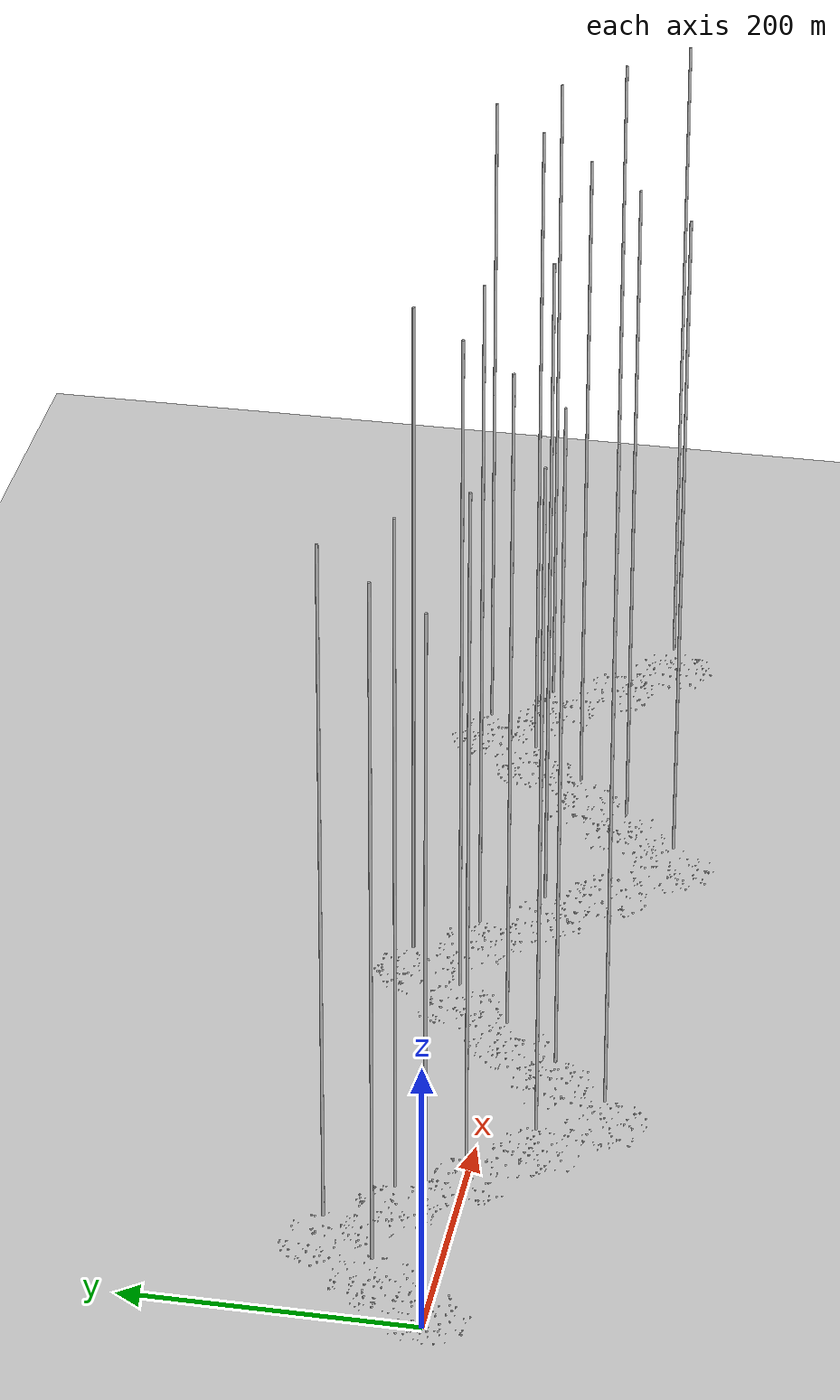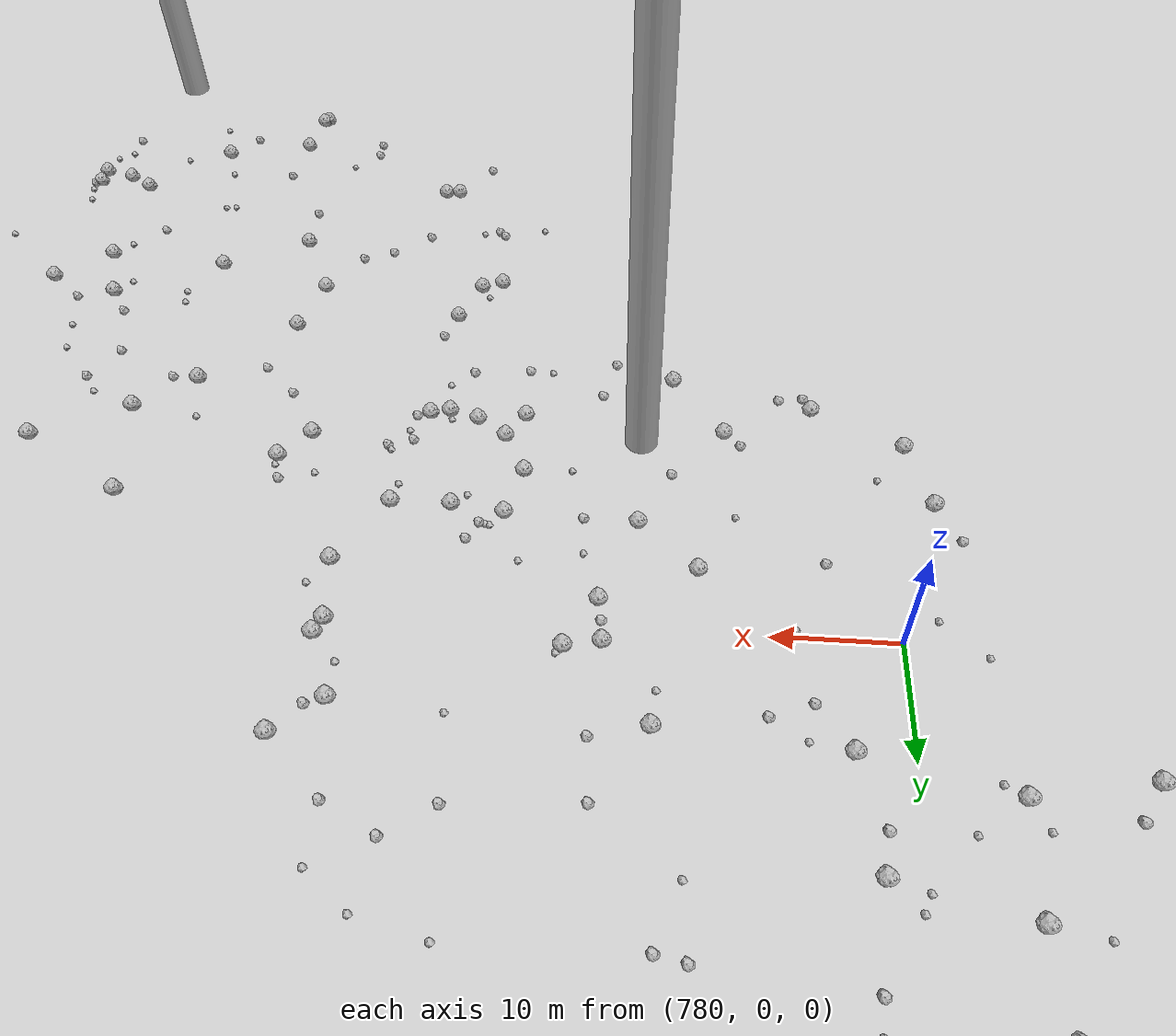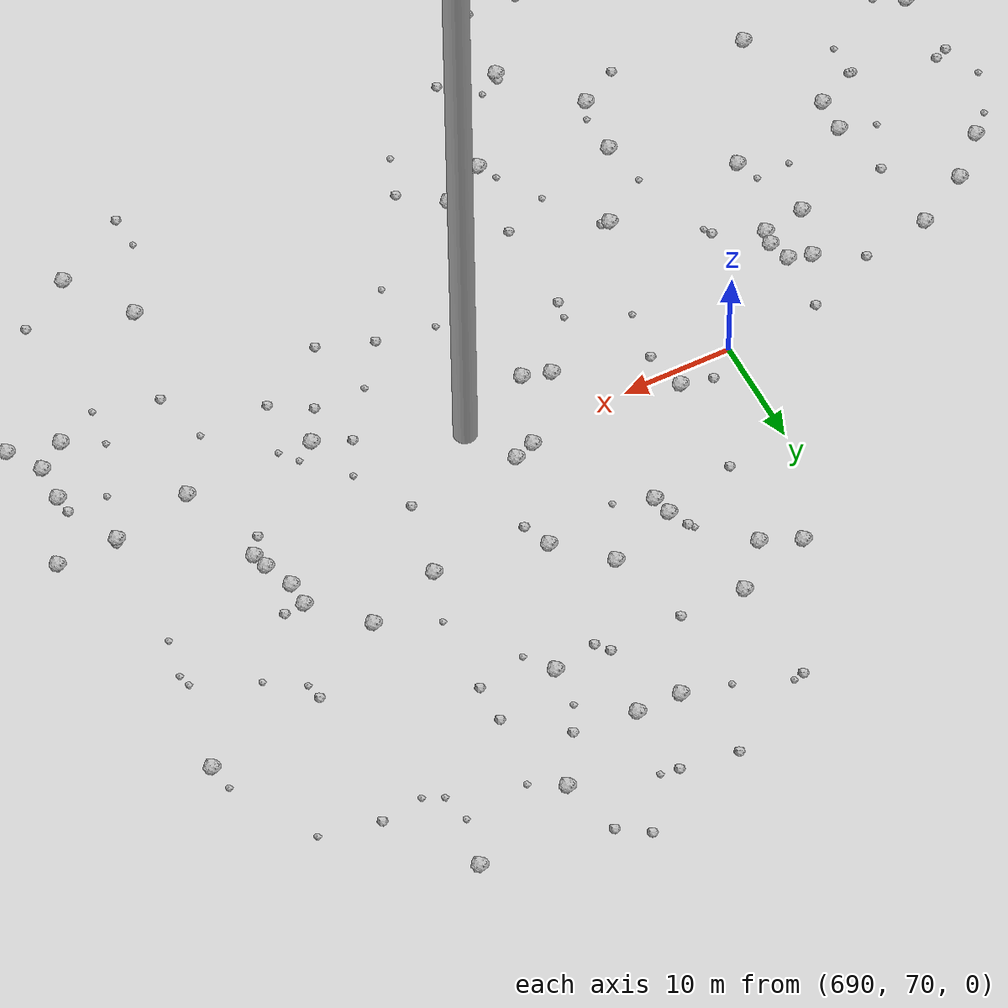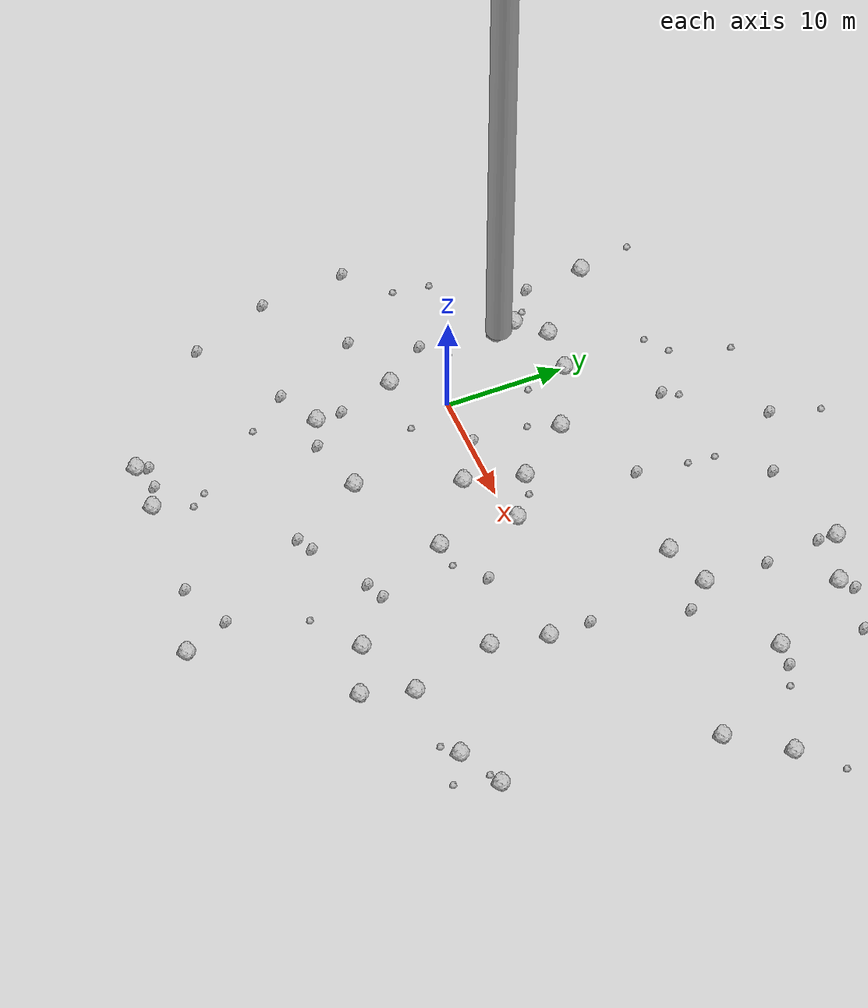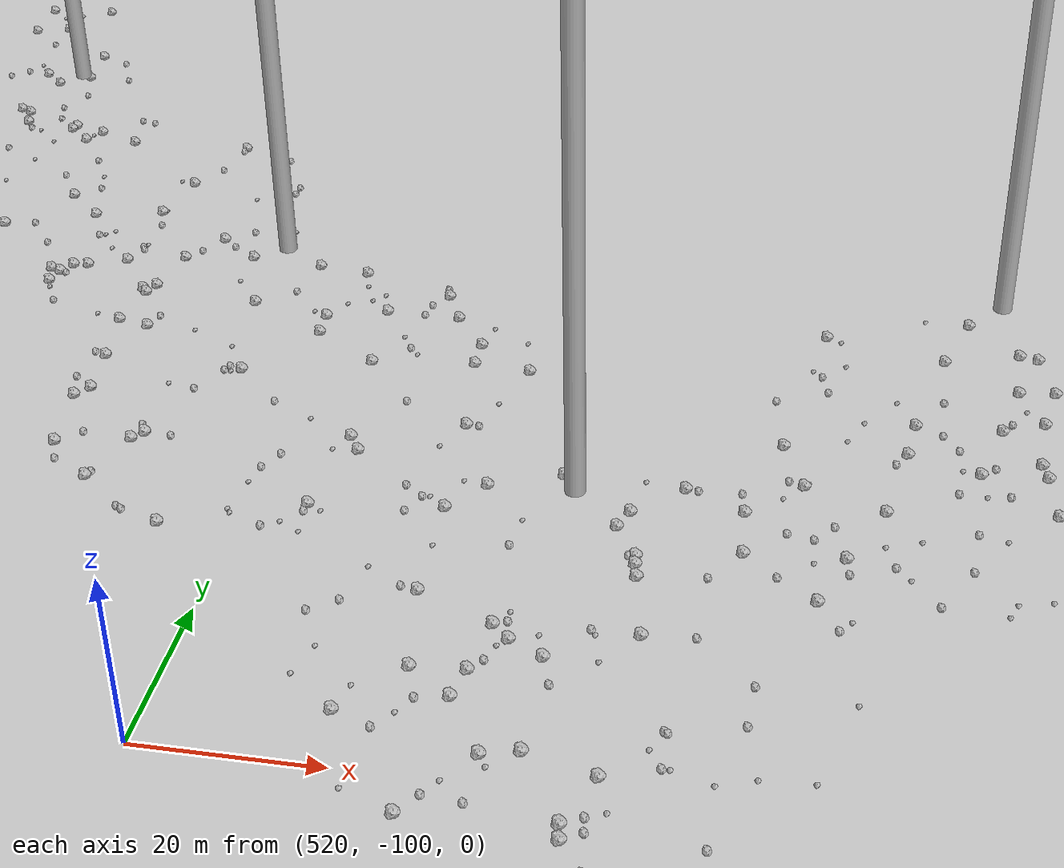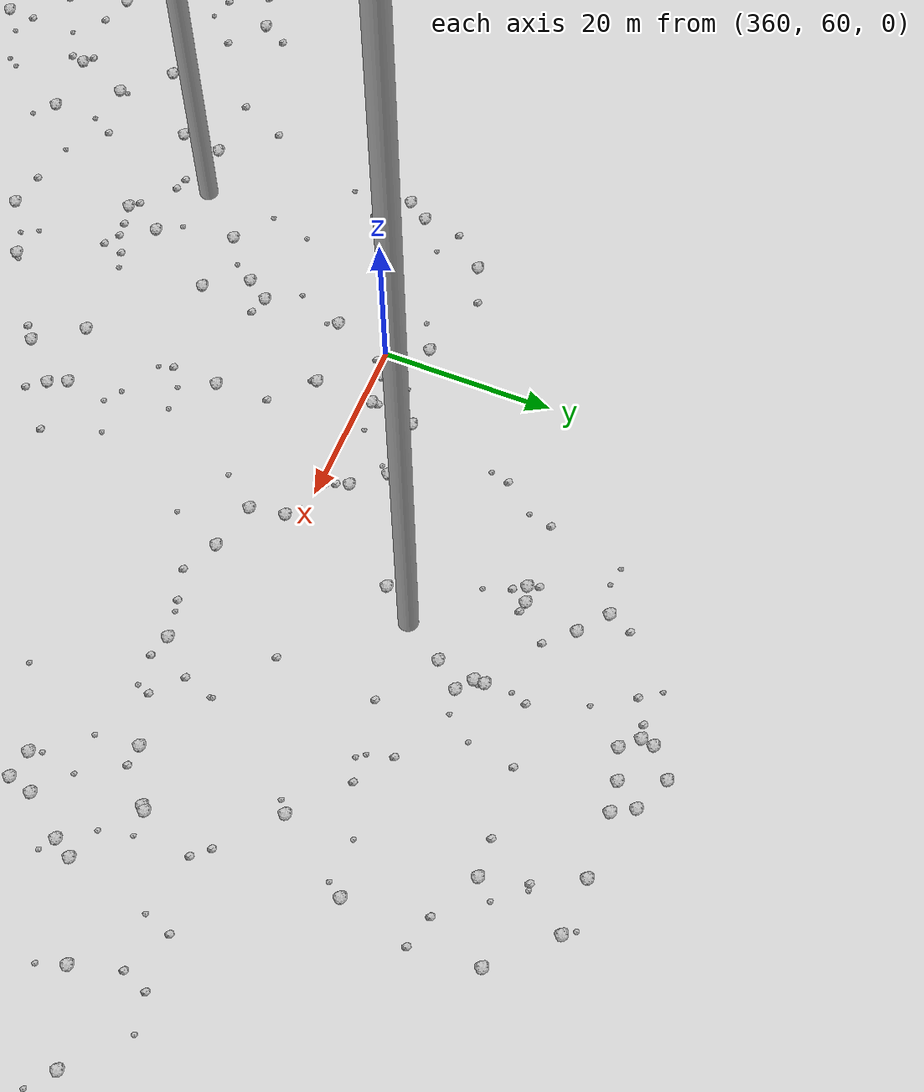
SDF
<sdf version="1.6">
 <world name="default">
  <include><uri>model://custom_ground</uri></include>
  <include><uri>model://sun</uri></include>
  <spherical_coordinates>
   <surface_model>EARTH_WGS84</surface_model>
   <latitude_deg>38.161479</latitude_deg>
   <longitude_deg>-122.454630</longitude_deg>
   <elevation>488.0</elevation>
   <heading_deg>90</heading_deg>
  </spherical_coordinates>
  <model name="rock1_0_0">
   <include><uri>model://rock1</uri><pose>-2.222451757468818 -10.581837322322098 0.5 0 0 0</pose></include>
  </model>
  <model name="rock1_0_1">
   <include><uri>model://rock1</uri><pose>13.431204475416507 -6.212510793779707 0.5 0 0 0</pose></include>
  </model>
  <model name="rock1_0_2">
   <include><uri>model://rock1</uri><pose>23.98812630230826 -6.380002196509871 0.5 0 0 0</pose></include>
  </model>
  <model name="rock1_0_3">
   <include><uri>model://rock1</uri><pose>5.788360593615213 7.498749063140281 0.5 0 0 0</pose></include>
  </model>
  <model name="rock1_0_4">
   <include><uri>model://rock1</uri><pose>36.297842312038405 -10.63201407955609 0.5 0 0 0</pose></include>
  </model>
  <model name="rock1_0_5">
   <include><uri>model://rock1</uri><pose>-3.673466896162452 10.487624643882576 0.5 0 0 0</pose></include>
  </model>
  <model name="rock1_0_6">
   <include><uri>model://rock1</uri><pose>13.139871151805394 0.552819182357247 0.5 0 0 0</pose></include>
  </model>
  <model name="rock1_0_7">
   <include><uri>model://rock1</uri><pose>24.636827593836685 11.67862548527222 0.5 0 0 0</pose></include>
  </model>
  <model name="rock1_0_8">
   <include><uri>model://rock1</uri><pose>15.712053744864946 -28.399677827994843 0.5 0 0 0</pose></include>
  </model>
  <model name="rock1_0_9">
   <include><uri>model://rock1</uri><pose>20.318105948930288 -15.599340286045642 0.5 0 0 0</pose></include>
  </model>
  <model name="rock1_0_10">
   <include><uri>model://rock1</uri><pose>-5.146742986593953 6.408223766327964 0.5 0 0 0</pose></include>
  </model>
  <model name="rock1_0_11">
   <include><uri>model://rock1</uri><pose>38.66866254140542 6.712074489030556 0.5 0 0 0</pose></include>
  </model>
  <model name="rock1_0_12">
   <include><uri>model://rock1</uri><pose>8.03302220357995 -1.9810905043413705 0.5 0 0 0</pose></include>
  </model>
  <model name="rock1_0_13">
   <include><uri>model://rock1</uri><pose>24.55267013478904 -17.48800686914373 0.5 0 0 0</pose></include>
  </model>
  <model name="rock1_0_14">
   <include><uri>model://rock1</uri><pose>25.820789251070437 -13.34318893832253 0.5 0 0 0</pose></include>
  </model>
  <model name="rock1_0_15">
   <include><uri>model://rock1</uri><pose>24.89300810401307 -1.7372767933455187 0.5 0 0 0</pose></include>
  </model>
  <model name="rock1_0_16">
   <include><uri>model://rock1</uri><pose>-9.063444340631847 15.747886120385317 0.5 0 0 0</pose></include>
  </model>
  <model name="rock1_0_17">
   <include><uri>model://rock1</uri><pose>1.1594875276328125 -25.924989393205834 0.5 0 0 0</pose></include>
  </model>
  <model name="rock1_0_18">
   <include><uri>model://rock1</uri><pose>9.448681355708548 2.8246205017620056 0.5 0 0 0</pose></include>
  </model>
  <model name="rock1_0_19">
   <include><uri>model://rock1</uri><pose>-5.829622296791273 8.323586304736459 0.5 0 0 0</pose></include>
  </model>
  <model name="rock1_0_20">
   <include><uri>model://rock1</uri><pose>32.58449512415758 -12.450160009094255 0.5 0 0 0</pose></include>
  </model>
  <model name="rock1_0_21">
   <include><uri>model://rock1</uri><pose>0.20359520777629925 10.228618213182159 0.5 0 0 0</pose></include>
  </model>
  <model name="rock1_0_22">
   <include><uri>model://rock1</uri><pose>32.53880830151446 14.518566565510788 0.5 0 0 0</pose></include>
  </model>
  <model name="rock1_0_23">
   <include><uri>model://rock1</uri><pose>20.709840082996664 10.365866952207945 0.5 0 0 0</pose></include>
  </model>
  <model name="rock1_0_24">
   <include><uri>model://rock1</uri><pose>-3.088458912417206 -25.796888001827725 0.5 0 0 0</pose></include>
  </model>
  <model name="rock1_0_25">
   <include><uri>model://rock1</uri><pose>5.132533084155767 -10.209141645786122 0.5 0 0 0</pose></include>
  </model>
  <model name="rock1_0_26">
   <include><uri>model://rock1</uri><pose>-3.664957584647798 -3.596069182486975 0.5 0 0 0</pose></include>
  </model>
  <model name="rock2_0_0">
   <include><uri>model://rock2</uri><pose>-12.857767891418838 -16.966735291315985 0.3 0 0 0</pose></include>
  </model>
  <model name="rock2_0_1">
   <include><uri>model://rock2</uri><pose>5.6079594012556235 16.512398481083807 0.3 0 0 0</pose></include>
  </model>
  <model name="rock2_0_2">
   <include><uri>model://rock2</uri><pose>-0.7836273892650567 -25.06708542778844 0.3 0 0 0</pose></include>
  </model>
  <model name="rock2_0_3">
   <include><uri>model://rock2</uri><pose>12.425258170624637 11.25664188357294 0.3 0 0 0</pose></include>
  </model>
  <model name="rock2_0_4">
   <include><uri>model://rock2</uri><pose>14.00517450485875 -24.52540366140609 0.3 0 0 0</pose></include>
  </model>
  <model name="rock2_0_5">
   <include><uri>model://rock2</uri><pose>-5.766597762581789 -12.308486757114213 0.3 0 0 0</pose></include>
  </model>
  <model name="rock2_0_6">
   <include><uri>model://rock2</uri><pose>14.803636229237355 -12.935269273979163 0.3 0 0 0</pose></include>
  </model>
  <model name="rock2_0_7">
   <include><uri>model://rock2</uri><pose>-2.350208131022967 -8.350069708726451 0.3 0 0 0</pose></include>
  </model>
  <model name="rock2_0_8">
   <include><uri>model://rock2</uri><pose>24.77366572739905 1.803123050793669 0.3 0 0 0</pose></include>
  </model>
  <model name="rock2_0_9">
   <include><uri>model://rock2</uri><pose>-6.405589465014865 0.11690339163025598 0.3 0 0 0</pose></include>
  </model>
  <model name="rock2_0_10">
   <include><uri>model://rock2</uri><pose>-8.79626393382727 10.701662757841277 0.3 0 0 0</pose></include>
  </model>
  <model name="rock2_0_11">
   <include><uri>model://rock2</uri><pose>10.786899187268958 23.790147856266458 0.3 0 0 0</pose></include>
  </model>
  <model name="rock2_0_12">
   <include><uri>model://rock2</uri><pose>16.489319823847794 21.421496921812007 0.3 0 0 0</pose></include>
  </model>
  <model name="rock2_0_13">
   <include><uri>model://rock2</uri><pose>-16.226660996857277 -2.831444718046903 0.3 0 0 0</pose></include>
  </model>
  <model name="rock2_0_14">
   <include><uri>model://rock2</uri><pose>9.884910835786293 -15.697068048861901 0.3 0 0 0</pose></include>
  </model>
  <model name="rock2_0_15">
   <include><uri>model://rock2</uri><pose>17.79927869909566 -3.8778248679882523 0.3 0 0 0</pose></include>
  </model>
  <model name="rock2_0_16">
   <include><uri>model://rock2</uri><pose>-15.484288286318602 -10.208360715430619 0.3 0 0 0</pose></include>
  </model>
  <model name="rock2_0_17">
   <include><uri>model://rock2</uri><pose>24.733592866332955 17.046097120055514 0.3 0 0 0</pose></include>
  </model>
  <model name="rock2_0_18">
   <include><uri>model://rock2</uri><pose>0.22226969841980804 -11.455774205411625 0.3 0 0 0</pose></include>
  </model>
  <model name="rock2_0_19">
   <include><uri>model://rock2</uri><pose>26.69763789416099 9.551045638803139 0.3 0 0 0</pose></include>
  </model>
  <model name="rock2_0_20">
   <include><uri>model://rock2</uri><pose>16.362687763645354 -12.269689180704827 0.3 0 0 0</pose></include>
  </model>
  <model name="rock2_0_21">
   <include><uri>model://rock2</uri><pose>8.530997891612344 -16.37762561559681 0.3 0 0 0</pose></include>
  </model>
  <model name="rock2_0_22">
   <include><uri>model://rock2</uri><pose>-2.8156907772023914 -24.81346541279529 0.3 0 0 0</pose></include>
  </model>
  <model name="rock2_0_23">
   <include><uri>model://rock2</uri><pose>-9.010824459341043 -5.140114193493176 0.3 0 0 0</pose></include>
  </model>
  <model name="rock2_0_24">
   <include><uri>model://rock2</uri><pose>4.447849646169207 0.34883792226374766 0.3 0 0 0</pose></include>
  </model>
  <model name="rock2_0_25">
   <include><uri>model://rock2</uri><pose>9.846303212415386 -26.37446557634999 0.3 0 0 0</pose></include>
  </model>
  <model name="rock2_0_26">
   <include><uri>model://rock2</uri><pose>34.42104060309182 14.390495053352353 0.3 0 0 0</pose></include>
  </model>
  <model name="rock3_0_0">
   <include><uri>model://rock3</uri><pose>13.02801703517823 15.495464233933909 0.2 0 0 0</pose></include>
  </model>
  <model name="rock3_0_1">
   <include><uri>model://rock3</uri><pose>-3.2817453409163093 -15.706460912131616 0.2 0 0 0</pose></include>
  </model>
  <model name="rock3_0_2">
   <include><uri>model://rock3</uri><pose>16.273314336600585 -18.361629241672183 0.2 0 0 0</pose></include>
  </model>
  <model name="rock3_0_3">
   <include><uri>model://rock3</uri><pose>1.5870746881903592 18.96787159623407 0.2 0 0 0</pose></include>
  </model>
  <model name="rock3_0_4">
   <include><uri>model://rock3</uri><pose>36.17554093057456 13.620808841548467 0.2 0 0 0</pose></include>
  </model>
  <model name="rock3_0_5">
   <include><uri>model://rock3</uri><pose>-10.12861823920677 20.39893679689679 0.2 0 0 0</pose></include>
  </model>
  <model name="rock3_0_6">
   <include><uri>model://rock3</uri><pose>11.148865136412663 2.412103341329619 0.2 0 0 0</pose></include>
  </model>
  <model name="rock3_0_7">
   <include><uri>model://rock3</uri><pose>3.2357389139302697 23.813497938547314 0.2 0 0 0</pose></include>
  </model>
  <model name="rock3_0_8">
   <include><uri>model://rock3</uri><pose>-6.795664525450695 9.42172691415913 0.2 0 0 0</pose></include>
  </model>
  <model name="rock3_0_9">
   <include><uri>model://rock3</uri><pose>31.246860954281935 -13.534269866254839 0.2 0 0 0</pose></include>
  </model>
  <model name="rock3_0_10">
   <include><uri>model://rock3</uri><pose>13.225387913131591 17.78042484362001 0.2 0 0 0</pose></include>
  </model>
  <model name="rock3_0_11">
   <include><uri>model://rock3</uri><pose>15.476148804100582 -5.9785903876213915 0.2 0 0 0</pose></include>
  </model>
  <model name="rock3_0_12">
   <include><uri>model://rock3</uri><pose>1.2638718405372877 -3.7281873921371904 0.2 0 0 0</pose></include>
  </model>
  <model name="rock3_0_13">
   <include><uri>model://rock3</uri><pose>1.0971838244474839 6.621743638411786 0.2 0 0 0</pose></include>
  </model>
  <model name="rock3_0_14">
   <include><uri>model://rock3</uri><pose>1.2320458372869325 -21.56540931347262 0.2 0 0 0</pose></include>
  </model>
  <model name="rock3_0_15">
   <include><uri>model://rock3</uri><pose>-4.820455990521202 2.026992589217407 0.2 0 0 0</pose></include>
  </model>
  <model name="rock3_0_16">
   <include><uri>model://rock3</uri><pose>4.645713232167456 5.030836297638331 0.2 0 0 0</pose></include>
  </model>
  <model name="rock3_0_17">
   <include><uri>model://rock3</uri><pose>34.89815827798925 -13.991094118039229 0.2 0 0 0</pose></include>
  </model>
  <model name="rock3_0_18">
   <include><uri>model://rock3</uri><pose>-14.806904821320055 11.043641910458504 0.2 0 0 0</pose></include>
  </model>
  <model name="rock3_0_19">
   <include><uri>model://rock3</uri><pose>-0.2485845692964581 17.56831227562961 0.2 0 0 0</pose></include>
  </model>
  <model name="rock3_0_20">
   <include><uri>model://rock3</uri><pose>5.947160756799054 7.789491219323914 0.2 0 0 0</pose></include>
  </model>
  <model name="rock3_0_21">
   <include><uri>model://rock3</uri><pose>35.102072335265035 -11.045525936062045 0.2 0 0 0</pose></include>
  </model>
  <model name="rock3_0_22">
   <include><uri>model://rock3</uri><pose>6.219155425255536 17.78820395953781 0.2 0 0 0</pose></include>
  </model>
  <model name="rock3_0_23">
   <include><uri>model://rock3</uri><pose>2.185255789604984 -22.806562185183978 0.2 0 0 0</pose></include>
  </model>
  <model name="rock3_0_24">
   <include><uri>model://rock3</uri><pose>-12.868456128406518 0.36367963435751705 0.2 0 0 0</pose></include>
  </model>
  <model name="rock3_0_25">
   <include><uri>model://rock3</uri><pose>11.954995363949074 27.83690892448758 0.2 0 0 0</pose></include>
  </model>
  <model name="rock3_0_26">
   <include><uri>model://rock3</uri><pose>-12.392941356449462 3.417923401189057 0.2 0 0 0</pose></include>
  </model>
  <model name="rock1_1_0">
   <include><uri>model://rock1</uri><pose>36.45295557095555 64.06599975438041 0.5 0 0 0</pose></include>
  </model>
  <model name="rock1_1_1">
   <include><uri>model://rock1</uri><pose>45.785223511346494 39.45855993979636 0.5 0 0 0</pose></include>
  </model>
  <model name="rock1_1_2">
   <include><uri>model://rock1</uri><pose>66.92537423840699 37.97630582141936 0.5 0 0 0</pose></include>
  </model>
  <model name="rock1_1_3">
   <include><uri>model://rock1</uri><pose>48.58842716321106 18.717362295044495 0.5 0 0 0</pose></include>
  </model>
  <model name="rock1_1_4">
   <include><uri>model://rock1</uri><pose>36.48671132226073 38.116386873087905 0.5 0 0 0</pose></include>
  </model>
  <model name="rock1_1_5">
   <include><uri>model://rock1</uri><pose>26.842357683838625 53.45543756668068 0.5 0 0 0</pose></include>
  </model>
  <model name="rock1_1_6">
   <include><uri>model://rock1</uri><pose>24.415300024771078 23.228097621380694 0.5 0 0 0</pose></include>
  </model>
  <model name="rock1_1_7">
   <include><uri>model://rock1</uri><pose>29.142619706307972 66.47894754618457 0.5 0 0 0</pose></include>
  </model>
  <model name="rock1_1_8">
   <include><uri>model://rock1</uri><pose>42.298937361636575 54.919836624936465 0.5 0 0 0</pose></include>
  </model>
  <model name="rock1_1_9">
   <include><uri>model://rock1</uri><pose>16.6300491872444 44.025662659932195 0.5 0 0 0</pose></include>
  </model>
  <model name="rock1_1_10">
   <include><uri>model://rock1</uri><pose>37.5741391899703 44.806328146111134 0.5 0 0 0</pose></include>
  </model>
  <model name="rock1_1_11">
   <include><uri>model://rock1</uri><pose>28.82630932104941 44.486939857678806 0.5 0 0 0</pose></include>
  </model>
  <model name="rock1_1_12">
   <include><uri>model://rock1</uri><pose>42.12554012740485 36.81366992369056 0.5 0 0 0</pose></include>
  </model>
  <model name="rock1_1_13">
   <include><uri>model://rock1</uri><pose>28.575910295863466 21.450072857304647 0.5 0 0 0</pose></include>
  </model>
  <model name="rock1_1_14">
   <include><uri>model://rock1</uri><pose>14.8077171732632 35.60279433961884 0.5 0 0 0</pose></include>
  </model>
  <model name="rock1_1_15">
   <include><uri>model://rock1</uri><pose>57.6783494961885 16.955138619184012 0.5 0 0 0</pose></include>
  </model>
  <model name="rock1_1_16">
   <include><uri>model://rock1</uri><pose>39.151698616833436 52.47365515467696 0.5 0 0 0</pose></include>
  </model>
  <model name="rock1_1_17">
   <include><uri>model://rock1</uri><pose>25.501984328575674 47.431314006001195 0.5 0 0 0</pose></include>
  </model>
  <model name="rock1_1_18">
   <include><uri>model://rock1</uri><pose>31.67201281373988 45.162816964030235 0.5 0 0 0</pose></include>
  </model>
  <model name="rock1_1_19">
   <include><uri>model://rock1</uri><pose>38.45786021381825 66.99117691745728 0.5 0 0 0</pose></include>
  </model>
  <model name="rock1_1_20">
   <include><uri>model://rock1</uri><pose>41.98805331901612 11.219682440814971 0.5 0 0 0</pose></include>
  </model>
  <model name="rock1_1_21">
   <include><uri>model://rock1</uri><pose>19.667386783610986 35.0880256736162 0.5 0 0 0</pose></include>
  </model>
  <model name="rock1_1_22">
   <include><uri>model://rock1</uri><pose>36.20651686706382 33.37802710603223 0.5 0 0 0</pose></include>
  </model>
  <model name="rock1_1_23">
   <include><uri>model://rock1</uri><pose>48.496453133910435 32.313913107320744 0.5 0 0 0</pose></include>
  </model>
  <model name="rock1_1_24">
   <include><uri>model://rock1</uri><pose>42.93933150591055 42.58024521381523 0.5 0 0 0</pose></include>
  </model>
  <model name="rock1_1_25">
   <include><uri>model://rock1</uri><pose>18.712343442400467 35.545960716467576 0.5 0 0 0</pose></include>
  </model>
  <model name="rock1_1_26">
   <include><uri>model://rock1</uri><pose>24.84933274204552 42.77095942425965 0.5 0 0 0</pose></include>
  </model>
  <model name="rock2_1_0">
   <include><uri>model://rock2</uri><pose>68.53234335541427 48.49915704482909 0.3 0 0 0</pose></include>
  </model>
  <model name="rock2_1_1">
   <include><uri>model://rock2</uri><pose>27.407123898474776 47.7007005691767 0.3 0 0 0</pose></include>
  </model>
  <model name="rock2_1_2">
   <include><uri>model://rock2</uri><pose>28.543644188509997 29.489518242031775 0.3 0 0 0</pose></include>
  </model>
  <model name="rock2_1_3">
   <include><uri>model://rock2</uri><pose>49.896746520656066 68.07075721068546 0.3 0 0 0</pose></include>
  </model>
  <model name="rock2_1_4">
   <include><uri>model://rock2</uri><pose>67.63069346296689 47.491702616848166 0.3 0 0 0</pose></include>
  </model>
  <model name="rock2_1_5">
   <include><uri>model://rock2</uri><pose>23.638881044091473 42.87031686660255 0.3 0 0 0</pose></include>
  </model>
  <model name="rock2_1_6">
   <include><uri>model://rock2</uri><pose>13.488124203345917 46.2376724813916 0.3 0 0 0</pose></include>
  </model>
  <model name="rock2_1_7">
   <include><uri>model://rock2</uri><pose>16.033013706044642 49.947913872575796 0.3 0 0 0</pose></include>
  </model>
  <model name="rock2_1_8">
   <include><uri>model://rock2</uri><pose>45.531529432499795 29.479432839829425 0.3 0 0 0</pose></include>
  </model>
  <model name="rock2_1_9">
   <include><uri>model://rock2</uri><pose>63.432728897648985 21.434467162796473 0.3 0 0 0</pose></include>
  </model>
  <model name="rock2_1_10">
   <include><uri>model://rock2</uri><pose>53.96103532424253 44.261193203259275 0.3 0 0 0</pose></include>
  </model>
  <model name="rock2_1_11">
   <include><uri>model://rock2</uri><pose>20.306470611674687 36.93215481522283 0.3 0 0 0</pose></include>
  </model>
  <model name="rock2_1_12">
   <include><uri>model://rock2</uri><pose>42.39683415859634 43.03442990246323 0.3 0 0 0</pose></include>
  </model>
  <model name="rock2_1_13">
   <include><uri>model://rock2</uri><pose>33.47833145060836 21.306807487444644 0.3 0 0 0</pose></include>
  </model>
  <model name="rock2_1_14">
   <include><uri>model://rock2</uri><pose>24.211659345339566 21.758628390245562 0.3 0 0 0</pose></include>
  </model>
  <model name="rock2_1_15">
   <include><uri>model://rock2</uri><pose>67.99714189337683 35.84948405386618 0.3 0 0 0</pose></include>
  </model>
  <model name="rock2_1_16">
   <include><uri>model://rock2</uri><pose>60.3618672492758 49.20298164534068 0.3 0 0 0</pose></include>
  </model>
  <model name="rock2_1_17">
   <include><uri>model://rock2</uri><pose>24.580694135270384 35.42206821222004 0.3 0 0 0</pose></include>
  </model>
  <model name="rock2_1_18">
   <include><uri>model://rock2</uri><pose>42.92729997735715 64.81235798663982 0.3 0 0 0</pose></include>
  </model>
  <model name="rock2_1_19">
   <include><uri>model://rock2</uri><pose>29.582909182072438 22.39012887740981 0.3 0 0 0</pose></include>
  </model>
  <model name="rock2_1_20">
   <include><uri>model://rock2</uri><pose>45.96150859011325 39.77477200182521 0.3 0 0 0</pose></include>
  </model>
  <model name="rock2_1_21">
   <include><uri>model://rock2</uri><pose>24.676715793403616 36.59610753843427 0.3 0 0 0</pose></include>
  </model>
  <model name="rock2_1_22">
   <include><uri>model://rock2</uri><pose>34.75262074739316 52.80519943807315 0.3 0 0 0</pose></include>
  </model>
  <model name="rock2_1_23">
   <include><uri>model://rock2</uri><pose>51.3883206886847 58.686357066870485 0.3 0 0 0</pose></include>
  </model>
  <model name="rock2_1_24">
   <include><uri>model://rock2</uri><pose>44.39928342836272 25.752072885908767 0.3 0 0 0</pose></include>
  </model>
  <model name="rock2_1_25">
   <include><uri>model://rock2</uri><pose>35.91743189698846 54.56865399196915 0.3 0 0 0</pose></include>
  </model>
  <model name="rock2_1_26">
   <include><uri>model://rock2</uri><pose>66.82372281165323 37.02963612520597 0.3 0 0 0</pose></include>
  </model>
  <model name="rock3_1_0">
   <include><uri>model://rock3</uri><pose>58.22504015219223 50.76174987524157 0.2 0 0 0</pose></include>
  </model>
  <model name="rock3_1_1">
   <include><uri>model://rock3</uri><pose>10.717513312976518 43.023952789456956 0.2 0 0 0</pose></include>
  </model>
  <model name="rock3_1_2">
   <include><uri>model://rock3</uri><pose>43.20287325076121 47.31293937070566 0.2 0 0 0</pose></include>
  </model>
  <model name="rock3_1_3">
   <include><uri>model://rock3</uri><pose>44.85381047411325 14.265582020040013 0.2 0 0 0</pose></include>
  </model>
  <model name="rock3_1_4">
   <include><uri>model://rock3</uri><pose>54.686430699917594 38.0238366201995 0.2 0 0 0</pose></include>
  </model>
  <model name="rock3_1_5">
   <include><uri>model://rock3</uri><pose>44.63272314505242 53.32838979964211 0.2 0 0 0</pose></include>
  </model>
  <model name="rock3_1_6">
   <include><uri>model://rock3</uri><pose>30.856489136350664 53.57851493684189 0.2 0 0 0</pose></include>
  </model>
  <model name="rock3_1_7">
   <include><uri>model://rock3</uri><pose>21.576978885649837 48.820780712039245 0.2 0 0 0</pose></include>
  </model>
  <model name="rock3_1_8">
   <include><uri>model://rock3</uri><pose>16.75253963145316 41.0239694741877 0.2 0 0 0</pose></include>
  </model>
  <model name="rock3_1_9">
   <include><uri>model://rock3</uri><pose>56.98474412073401 60.81630862167404 0.2 0 0 0</pose></include>
  </model>
  <model name="rock3_1_10">
   <include><uri>model://rock3</uri><pose>45.649891418889595 51.879674777649655 0.2 0 0 0</pose></include>
  </model>
  <model name="rock3_1_11">
   <include><uri>model://rock3</uri><pose>39.46118882130762 21.43938484234826 0.2 0 0 0</pose></include>
  </model>
  <model name="rock3_1_12">
   <include><uri>model://rock3</uri><pose>28.67666642744463 65.41244080477996 0.2 0 0 0</pose></include>
  </model>
  <model name="rock3_1_13">
   <include><uri>model://rock3</uri><pose>57.61390099331161 48.33477559489686 0.2 0 0 0</pose></include>
  </model>
  <model name="rock3_1_14">
   <include><uri>model://rock3</uri><pose>42.44641011593202 34.04518638437633 0.2 0 0 0</pose></include>
  </model>
  <model name="rock3_1_15">
   <include><uri>model://rock3</uri><pose>18.645068998083083 33.75924921974422 0.2 0 0 0</pose></include>
  </model>
  <model name="rock3_1_16">
   <include><uri>model://rock3</uri><pose>44.9524060535086 36.03448103784157 0.2 0 0 0</pose></include>
  </model>
  <model name="rock3_1_17">
   <include><uri>model://rock3</uri><pose>53.38465472425952 21.456552632018386 0.2 0 0 0</pose></include>
  </model>
  <model name="rock3_1_18">
   <include><uri>model://rock3</uri><pose>46.654158456386945 63.52857704061402 0.2 0 0 0</pose></include>
  </model>
  <model name="rock3_1_19">
   <include><uri>model://rock3</uri><pose>31.33026081642641 64.38455298581951 0.2 0 0 0</pose></include>
  </model>
  <model name="rock3_1_20">
   <include><uri>model://rock3</uri><pose>56.84466155601942 39.961309242955075 0.2 0 0 0</pose></include>
  </model>
  <model name="rock3_1_21">
   <include><uri>model://rock3</uri><pose>50.82077246754976 58.68993162121157 0.2 0 0 0</pose></include>
  </model>
  <model name="rock3_1_22">
   <include><uri>model://rock3</uri><pose>60.16663309285203 35.71172105377144 0.2 0 0 0</pose></include>
  </model>
  <model name="rock3_1_23">
   <include><uri>model://rock3</uri><pose>30.365334520502195 62.848488488117376 0.2 0 0 0</pose></include>
  </model>
  <model name="rock3_1_24">
   <include><uri>model://rock3</uri><pose>59.73158338575742 55.35375406211523 0.2 0 0 0</pose></include>
  </model>
  <model name="rock3_1_25">
   <include><uri>model://rock3</uri><pose>51.610286874337014 40.47783952369129 0.2 0 0 0</pose></include>
  </model>
  <model name="rock3_1_26">
   <include><uri>model://rock3</uri><pose>63.781479616752456 24.448199052678113 0.2 0 0 0</pose></include>
  </model>
  <model name="rock1_2_0">
   <include><uri>model://rock1</uri><pose>57.336128494549804 75.23354540770909 0.5 0 0 0</pose></include>
  </model>
  <model name="rock1_2_1">
   <include><uri>model://rock1</uri><pose>63.87779364117566 104.98169970274556 0.5 0 0 0</pose></include>
  </model>
  <model name="rock1_2_2">
   <include><uri>model://rock1</uri><pose>65.26348913918642 100.42136429680272 0.5 0 0 0</pose></include>
  </model>
  <model name="rock1_2_3">
   <include><uri>model://rock1</uri><pose>104.39572888179228 90.38578709085958 0.5 0 0 0</pose></include>
  </model>
  <model name="rock1_2_4">
   <include><uri>model://rock1</uri><pose>54.0284771043663 90.71691130136429 0.5 0 0 0</pose></include>
  </model>
  <model name="rock1_2_5">
   <include><uri>model://rock1</uri><pose>93.16503909671808 79.0630423297056 0.5 0 0 0</pose></include>
  </model>
  <model name="rock1_2_6">
   <include><uri>model://rock1</uri><pose>89.53019534478909 58.7674983748344 0.5 0 0 0</pose></include>
  </model>
  <model name="rock1_2_7">
   <include><uri>model://rock1</uri><pose>83.53262492320579 57.62665964860506 0.5 0 0 0</pose></include>
  </model>
  <model name="rock1_2_8">
   <include><uri>model://rock1</uri><pose>72.24969465823968 88.58703377744702 0.5 0 0 0</pose></include>
  </model>
  <model name="rock1_2_9">
   <include><uri>model://rock1</uri><pose>62.48923395331378 79.14323757658923 0.5 0 0 0</pose></include>
  </model>
  <model name="rock1_2_10">
   <include><uri>model://rock1</uri><pose>81.82074643813687 58.561739457576735 0.5 0 0 0</pose></include>
  </model>
  <model name="rock1_2_11">
   <include><uri>model://rock1</uri><pose>85.77045376764798 86.81209863124116 0.5 0 0 0</pose></include>
  </model>
  <model name="rock1_2_12">
   <include><uri>model://rock1</uri><pose>88.22802351658811 87.27826034553436 0.5 0 0 0</pose></include>
  </model>
  <model name="rock1_2_13">
   <include><uri>model://rock1</uri><pose>87.72774483712385 65.13326805860208 0.5 0 0 0</pose></include>
  </model>
  <model name="rock1_2_14">
   <include><uri>model://rock1</uri><pose>72.83681335937928 71.59882652908783 0.5 0 0 0</pose></include>
  </model>
  <model name="rock1_2_15">
   <include><uri>model://rock1</uri><pose>77.87163866744991 55.35048084512062 0.5 0 0 0</pose></include>
  </model>
  <model name="rock1_2_16">
   <include><uri>model://rock1</uri><pose>97.3855620766983 71.74145718340316 0.5 0 0 0</pose></include>
  </model>
  <model name="rock1_2_17">
   <include><uri>model://rock1</uri><pose>89.64221848635447 90.19773115751745 0.5 0 0 0</pose></include>
  </model>
  <model name="rock1_2_18">
   <include><uri>model://rock1</uri><pose>61.13071928220674 82.29781533302906 0.5 0 0 0</pose></include>
  </model>
  <model name="rock1_2_19">
   <include><uri>model://rock1</uri><pose>65.06027196192872 88.48752656472107 0.5 0 0 0</pose></include>
  </model>
  <model name="rock1_2_20">
   <include><uri>model://rock1</uri><pose>104.75180065189551 92.80308608863182 0.5 0 0 0</pose></include>
  </model>
  <model name="rock1_2_21">
   <include><uri>model://rock1</uri><pose>85.15411898926351 88.22088132469808 0.5 0 0 0</pose></include>
  </model>
  <model name="rock1_2_22">
   <include><uri>model://rock1</uri><pose>80.24678606696003 51.88794191323883 0.5 0 0 0</pose></include>
  </model>
  <model name="rock1_2_23">
   <include><uri>model://rock1</uri><pose>50.70343649103998 82.96688812582828 0.5 0 0 0</pose></include>
  </model>
  <model name="rock1_2_24">
   <include><uri>model://rock1</uri><pose>61.30693296606773 72.64613785548212 0.5 0 0 0</pose></include>
  </model>
  <model name="rock1_2_25">
   <include><uri>model://rock1</uri><pose>72.1128405922307 107.86866297771746 0.5 0 0 0</pose></include>
  </model>
  <model name="rock1_2_26">
   <include><uri>model://rock1</uri><pose>90.91803955885324 103.47083318076625 0.5 0 0 0</pose></include>
  </model>
  <model name="rock2_2_0">
   <include><uri>model://rock2</uri><pose>90.36897218362537 60.98579001990272 0.3 0 0 0</pose></include>
  </model>
  <model name="rock2_2_1">
   <include><uri>model://rock2</uri><pose>66.0152333660281 88.73640885617206 0.3 0 0 0</pose></include>
  </model>
  <model name="rock2_2_2">
   <include><uri>model://rock2</uri><pose>84.49868356653893 80.12814268013041 0.3 0 0 0</pose></include>
  </model>
  <model name="rock2_2_3">
   <include><uri>model://rock2</uri><pose>94.51035063373035 83.44700514941502 0.3 0 0 0</pose></include>
  </model>
  <model name="rock2_2_4">
   <include><uri>model://rock2</uri><pose>92.39520241467346 77.10089802692373 0.3 0 0 0</pose></include>
  </model>
  <model name="rock2_2_5">
   <include><uri>model://rock2</uri><pose>97.14751802071655 103.29044452827249 0.3 0 0 0</pose></include>
  </model>
  <model name="rock2_2_6">
   <include><uri>model://rock2</uri><pose>109.62485976148602 82.33854009560868 0.3 0 0 0</pose></include>
  </model>
  <model name="rock2_2_7">
   <include><uri>model://rock2</uri><pose>57.9269885919083 98.85253645362852 0.3 0 0 0</pose></include>
  </model>
  <model name="rock2_2_8">
   <include><uri>model://rock2</uri><pose>58.05393516172137 99.86534256159794 0.3 0 0 0</pose></include>
  </model>
  <model name="rock2_2_9">
   <include><uri>model://rock2</uri><pose>80.7736073213906 72.44972903481427 0.3 0 0 0</pose></include>
  </model>
  <model name="rock2_2_10">
   <include><uri>model://rock2</uri><pose>74.18163316858877 103.85551852745694 0.3 0 0 0</pose></include>
  </model>
  <model name="rock2_2_11">
   <include><uri>model://rock2</uri><pose>67.68464129760852 91.19708752897839 0.3 0 0 0</pose></include>
  </model>
  <model name="rock2_2_12">
   <include><uri>model://rock2</uri><pose>68.59689582916161 104.49500461387738 0.3 0 0 0</pose></include>
  </model>
  <model name="rock2_2_13">
   <include><uri>model://rock2</uri><pose>77.87597724126317 71.82176546139237 0.3 0 0 0</pose></include>
  </model>
  <model name="rock2_2_14">
   <include><uri>model://rock2</uri><pose>107.9016645391078 69.91300703138714 0.3 0 0 0</pose></include>
  </model>
  <model name="rock2_2_15">
   <include><uri>model://rock2</uri><pose>90.59279030487531 89.4933358598717 0.3 0 0 0</pose></include>
  </model>
  <model name="rock2_2_16">
   <include><uri>model://rock2</uri><pose>74.90557339412968 103.30325117441623 0.3 0 0 0</pose></include>
  </model>
  <model name="rock2_2_17">
   <include><uri>model://rock2</uri><pose>57.47558003765231 92.49037319906371 0.3 0 0 0</pose></include>
  </model>
  <model name="rock2_2_18">
   <include><uri>model://rock2</uri><pose>106.12004582902902 67.59512164509667 0.3 0 0 0</pose></include>
  </model>
  <model name="rock2_2_19">
   <include><uri>model://rock2</uri><pose>69.50694589483425 103.62212827879665 0.3 0 0 0</pose></include>
  </model>
  <model name="rock2_2_20">
   <include><uri>model://rock2</uri><pose>73.08304122997593 94.99263778187537 0.3 0 0 0</pose></include>
  </model>
  <model name="rock2_2_21">
   <include><uri>model://rock2</uri><pose>54.87987684118418 79.34070063118007 0.3 0 0 0</pose></include>
  </model>
  <model name="rock2_2_22">
   <include><uri>model://rock2</uri><pose>87.33236883896973 52.550892975350614 0.3 0 0 0</pose></include>
  </model>
  <model name="rock2_2_23">
   <include><uri>model://rock2</uri><pose>89.4125327343643 68.87785765216634 0.3 0 0 0</pose></include>
  </model>
  <model name="rock2_2_24">
   <include><uri>model://rock2</uri><pose>67.57502124118312 79.02110601583075 0.3 0 0 0</pose></include>
  </model>
  <model name="rock2_2_25">
   <include><uri>model://rock2</uri><pose>55.950945347031976 79.62770763972424 0.3 0 0 0</pose></include>
  </model>
  <model name="rock2_2_26">
   <include><uri>model://rock2</uri><pose>74.43819760959249 108.03920753994285 0.3 0 0 0</pose></include>
  </model>
  <model name="rock3_2_0">
   <include><uri>model://rock3</uri><pose>102.35043829047333 69.5916706444403 0.2 0 0 0</pose></include>
  </model>
  <model name="rock3_2_1">
   <include><uri>model://rock3</uri><pose>65.90612384894388 66.61949876440137 0.2 0 0 0</pose></include>
  </model>
  <model name="rock3_2_2">
   <include><uri>model://rock3</uri><pose>95.22857735875462 71.43783534274353 0.2 0 0 0</pose></include>
  </model>
  <model name="rock3_2_3">
   <include><uri>model://rock3</uri><pose>72.07088239298481 80.89075611302576 0.2 0 0 0</pose></include>
  </model>
  <model name="rock3_2_4">
   <include><uri>model://rock3</uri><pose>87.18457311427625 101.56165487943744 0.2 0 0 0</pose></include>
  </model>
  <model name="rock3_2_5">
   <include><uri>model://rock3</uri><pose>59.724304806152745 62.06377743411163 0.2 0 0 0</pose></include>
  </model>
  <model name="rock3_2_6">
   <include><uri>model://rock3</uri><pose>96.34641071598347 102.87335362945934 0.2 0 0 0</pose></include>
  </model>
  <model name="rock3_2_7">
   <include><uri>model://rock3</uri><pose>56.746202386586866 94.41133149841968 0.2 0 0 0</pose></include>
  </model>
  <model name="rock3_2_8">
   <include><uri>model://rock3</uri><pose>59.33411597629798 65.10214673925489 0.2 0 0 0</pose></include>
  </model>
  <model name="rock3_2_9">
   <include><uri>model://rock3</uri><pose>81.7936098449492 56.55275074552749 0.2 0 0 0</pose></include>
  </model>
  <model name="rock3_2_10">
   <include><uri>model://rock3</uri><pose>94.26357313839956 82.73257766425206 0.2 0 0 0</pose></include>
  </model>
  <model name="rock3_2_11">
   <include><uri>model://rock3</uri><pose>76.14327482104964 56.2405761167833 0.2 0 0 0</pose></include>
  </model>
  <model name="rock3_2_12">
   <include><uri>model://rock3</uri><pose>96.74695903641691 64.15248622588332 0.2 0 0 0</pose></include>
  </model>
  <model name="rock3_2_13">
   <include><uri>model://rock3</uri><pose>94.8740359099263 67.77907713582508 0.2 0 0 0</pose></include>
  </model>
  <model name="rock3_2_14">
   <include><uri>model://rock3</uri><pose>104.28098294647354 64.25102458893974 0.2 0 0 0</pose></include>
  </model>
  <model name="rock3_2_15">
   <include><uri>model://rock3</uri><pose>80.63529058131054 70.74670826177393 0.2 0 0 0</pose></include>
  </model>
  <model name="rock3_2_16">
   <include><uri>model://rock3</uri><pose>74.99312868744138 57.85361023771188 0.2 0 0 0</pose></include>
  </model>
  <model name="rock3_2_17">
   <include><uri>model://rock3</uri><pose>95.7746575165556 100.00185406088586 0.2 0 0 0</pose></include>
  </model>
  <model name="rock3_2_18">
   <include><uri>model://rock3</uri><pose>83.15225921314442 62.45370063471091 0.2 0 0 0</pose></include>
  </model>
  <model name="rock3_2_19">
   <include><uri>model://rock3</uri><pose>82.35997235768302 66.67728214957043 0.2 0 0 0</pose></include>
  </model>
  <model name="rock3_2_20">
   <include><uri>model://rock3</uri><pose>68.79480443463288 78.29292426463994 0.2 0 0 0</pose></include>
  </model>
  <model name="rock3_2_21">
   <include><uri>model://rock3</uri><pose>87.49824707695203 54.007385306417646 0.2 0 0 0</pose></include>
  </model>
  <model name="rock3_2_22">
   <include><uri>model://rock3</uri><pose>68.90872421032672 82.45448059271187 0.2 0 0 0</pose></include>
  </model>
  <model name="rock3_2_23">
   <include><uri>model://rock3</uri><pose>59.695251055517275 94.24792228710726 0.2 0 0 0</pose></include>
  </model>
  <model name="rock3_2_24">
   <include><uri>model://rock3</uri><pose>80.59971311671906 85.12264662417942 0.2 0 0 0</pose></include>
  </model>
  <model name="rock3_2_25">
   <include><uri>model://rock3</uri><pose>98.85526119103962 66.87459593515705 0.2 0 0 0</pose></include>
  </model>
  <model name="rock3_2_26">
   <include><uri>model://rock3</uri><pose>97.73210228338186 69.73334611331293 0.2 0 0 0</pose></include>
  </model>
  <model name="rock1_3_0">
   <include><uri>model://rock1</uri><pose>117.32824340051044 26.609835664477878 0.5 0 0 0</pose></include>
  </model>
  <model name="rock1_3_1">
   <include><uri>model://rock1</uri><pose>142.67299335185658 57.94004480334743 0.5 0 0 0</pose></include>
  </model>
  <model name="rock1_3_2">
   <include><uri>model://rock1</uri><pose>123.70868253520054 13.630232229940738 0.5 0 0 0</pose></include>
  </model>
  <model name="rock1_3_3">
   <include><uri>model://rock1</uri><pose>97.74800526178754 58.47256986078627 0.5 0 0 0</pose></include>
  </model>
  <model name="rock1_3_4">
   <include><uri>model://rock1</uri><pose>129.282906694726 43.6136888667853 0.5 0 0 0</pose></include>
  </model>
  <model name="rock1_3_5">
   <include><uri>model://rock1</uri><pose>142.39190113921921 32.83186674032445 0.5 0 0 0</pose></include>
  </model>
  <model name="rock1_3_6">
   <include><uri>model://rock1</uri><pose>120.45031844348802 63.96225492790629 0.5 0 0 0</pose></include>
  </model>
  <model name="rock1_3_7">
   <include><uri>model://rock1</uri><pose>130.07223034992214 44.34267578664128 0.5 0 0 0</pose></include>
  </model>
  <model name="rock1_3_8">
   <include><uri>model://rock1</uri><pose>114.03517379327002 30.399101188125044 0.5 0 0 0</pose></include>
  </model>
  <model name="rock1_3_9">
   <include><uri>model://rock1</uri><pose>124.89458304181443 21.816099198193378 0.5 0 0 0</pose></include>
  </model>
  <model name="rock1_3_10">
   <include><uri>model://rock1</uri><pose>108.62147079429342 40.34486473011431 0.5 0 0 0</pose></include>
  </model>
  <model name="rock1_3_11">
   <include><uri>model://rock1</uri><pose>110.28644077777017 33.631364004011274 0.5 0 0 0</pose></include>
  </model>
  <model name="rock1_3_12">
   <include><uri>model://rock1</uri><pose>117.26811817052685 14.857361535339077 0.5 0 0 0</pose></include>
  </model>
  <model name="rock1_3_13">
   <include><uri>model://rock1</uri><pose>109.61425034229616 65.19005508055969 0.5 0 0 0</pose></include>
  </model>
  <model name="rock1_3_14">
   <include><uri>model://rock1</uri><pose>126.12584658355408 62.22565810030895 0.5 0 0 0</pose></include>
  </model>
  <model name="rock1_3_15">
   <include><uri>model://rock1</uri><pose>108.10895039387158 52.51772953036124 0.5 0 0 0</pose></include>
  </model>
  <model name="rock1_3_16">
   <include><uri>model://rock1</uri><pose>140.85440354930418 53.29482655405213 0.5 0 0 0</pose></include>
  </model>
  <model name="rock1_3_17">
   <include><uri>model://rock1</uri><pose>116.57201741454301 48.71007126141962 0.5 0 0 0</pose></include>
  </model>
  <model name="rock1_3_18">
   <include><uri>model://rock1</uri><pose>113.4306696641584 35.81746957396777 0.5 0 0 0</pose></include>
  </model>
  <model name="rock1_3_19">
   <include><uri>model://rock1</uri><pose>129.4983302289113 65.19864921741282 0.5 0 0 0</pose></include>
  </model>
  <model name="rock1_3_20">
   <include><uri>model://rock1</uri><pose>139.99265351167355 28.251754859834854 0.5 0 0 0</pose></include>
  </model>
  <model name="rock1_3_21">
   <include><uri>model://rock1</uri><pose>135.52387441713356 21.980453727559997 0.5 0 0 0</pose></include>
  </model>
  <model name="rock1_3_22">
   <include><uri>model://rock1</uri><pose>140.9012989320735 59.69129739002648 0.5 0 0 0</pose></include>
  </model>
  <model name="rock1_3_23">
   <include><uri>model://rock1</uri><pose>125.64661414470083 63.710026146107296 0.5 0 0 0</pose></include>
  </model>
  <model name="rock1_3_24">
   <include><uri>model://rock1</uri><pose>132.8593816104555 66.25972585327611 0.5 0 0 0</pose></include>
  </model>
  <model name="rock1_3_25">
   <include><uri>model://rock1</uri><pose>108.76922564722669 43.94011499032744 0.5 0 0 0</pose></include>
  </model>
  <model name="rock1_3_26">
   <include><uri>model://rock1</uri><pose>126.81419314355833 40.84775022339834 0.5 0 0 0</pose></include>
  </model>
  <model name="rock2_3_0">
   <include><uri>model://rock2</uri><pose>110.18176818459156 40.31232727963853 0.3 0 0 0</pose></include>
  </model>
  <model name="rock2_3_1">
   <include><uri>model://rock2</uri><pose>126.85046991595861 10.812877972865014 0.3 0 0 0</pose></include>
  </model>
  <model name="rock2_3_2">
   <include><uri>model://rock2</uri><pose>145.08773642159633 52.84579681293687 0.3 0 0 0</pose></include>
  </model>
  <model name="rock2_3_3">
   <include><uri>model://rock2</uri><pose>147.44519736937409 32.75495277863616 0.3 0 0 0</pose></include>
  </model>
  <model name="rock2_3_4">
   <include><uri>model://rock2</uri><pose>114.25284043361037 15.090229431026977 0.3 0 0 0</pose></include>
  </model>
  <model name="rock2_3_5">
   <include><uri>model://rock2</uri><pose>148.14955743000002 34.407250488608746 0.3 0 0 0</pose></include>
  </model>
  <model name="rock2_3_6">
   <include><uri>model://rock2</uri><pose>111.01481503181049 65.3772127000259 0.3 0 0 0</pose></include>
  </model>
  <model name="rock2_3_7">
   <include><uri>model://rock2</uri><pose>127.15539622513599 67.4942452873129 0.3 0 0 0</pose></include>
  </model>
  <model name="rock2_3_8">
   <include><uri>model://rock2</uri><pose>102.80190121766547 40.36570893834768 0.3 0 0 0</pose></include>
  </model>
  <model name="rock2_3_9">
   <include><uri>model://rock2</uri><pose>106.79624158587666 51.299948826302305 0.3 0 0 0</pose></include>
  </model>
  <model name="rock2_3_10">
   <include><uri>model://rock2</uri><pose>135.98434588346245 56.674864179989314 0.3 0 0 0</pose></include>
  </model>
  <model name="rock2_3_11">
   <include><uri>model://rock2</uri><pose>104.3093376101499 20.764730781487437 0.3 0 0 0</pose></include>
  </model>
  <model name="rock2_3_12">
   <include><uri>model://rock2</uri><pose>125.49549371283828 18.121611766032963 0.3 0 0 0</pose></include>
  </model>
  <model name="rock2_3_13">
   <include><uri>model://rock2</uri><pose>124.46606322909321 64.7640798762347 0.3 0 0 0</pose></include>
  </model>
  <model name="rock2_3_14">
   <include><uri>model://rock2</uri><pose>104.07931401890443 23.32017509619766 0.3 0 0 0</pose></include>
  </model>
  <model name="rock2_3_15">
   <include><uri>model://rock2</uri><pose>119.93310269406571 19.018899856212936 0.3 0 0 0</pose></include>
  </model>
  <model name="rock2_3_16">
   <include><uri>model://rock2</uri><pose>122.06865552757245 44.955742416484114 0.3 0 0 0</pose></include>
  </model>
  <model name="rock2_3_17">
   <include><uri>model://rock2</uri><pose>116.46892460411442 33.35487224740949 0.3 0 0 0</pose></include>
  </model>
  <model name="rock2_3_18">
   <include><uri>model://rock2</uri><pose>137.55240289916344 44.540976200576296 0.3 0 0 0</pose></include>
  </model>
  <model name="rock2_3_19">
   <include><uri>model://rock2</uri><pose>129.60540054316326 20.505653433023276 0.3 0 0 0</pose></include>
  </model>
  <model name="rock2_3_20">
   <include><uri>model://rock2</uri><pose>109.73981038813761 63.617580128360025 0.3 0 0 0</pose></include>
  </model>
  <model name="rock2_3_21">
   <include><uri>model://rock2</uri><pose>145.31933938118516 50.806221719885244 0.3 0 0 0</pose></include>
  </model>
  <model name="rock2_3_22">
   <include><uri>model://rock2</uri><pose>106.16799514758603 49.07856984307213 0.3 0 0 0</pose></include>
  </model>
  <model name="rock2_3_23">
   <include><uri>model://rock2</uri><pose>116.31210710287456 51.31804841181762 0.3 0 0 0</pose></include>
  </model>
  <model name="rock2_3_24">
   <include><uri>model://rock2</uri><pose>116.62914676288864 42.08487438966961 0.3 0 0 0</pose></include>
  </model>
  <model name="rock2_3_25">
   <include><uri>model://rock2</uri><pose>107.60860604829014 42.256926916499516 0.3 0 0 0</pose></include>
  </model>
  <model name="rock2_3_26">
   <include><uri>model://rock2</uri><pose>92.17833735996987 37.43023380821168 0.3 0 0 0</pose></include>
  </model>
  <model name="rock3_3_0">
   <include><uri>model://rock3</uri><pose>94.2473999010245 36.23603105639609 0.2 0 0 0</pose></include>
  </model>
  <model name="rock3_3_1">
   <include><uri>model://rock3</uri><pose>119.06333261812227 45.648022298969174 0.2 0 0 0</pose></include>
  </model>
  <model name="rock3_3_2">
   <include><uri>model://rock3</uri><pose>109.18334365103026 14.230451554458824 0.2 0 0 0</pose></include>
  </model>
  <model name="rock3_3_3">
   <include><uri>model://rock3</uri><pose>128.27750200616728 48.607221290392175 0.2 0 0 0</pose></include>
  </model>
  <model name="rock3_3_4">
   <include><uri>model://rock3</uri><pose>122.13576874455873 40.979875599619305 0.2 0 0 0</pose></include>
  </model>
  <model name="rock3_3_5">
   <include><uri>model://rock3</uri><pose>114.16801350113789 19.724925084809144 0.2 0 0 0</pose></include>
  </model>
  <model name="rock3_3_6">
   <include><uri>model://rock3</uri><pose>119.98519101689064 15.057875132319127 0.2 0 0 0</pose></include>
  </model>
  <model name="rock3_3_7">
   <include><uri>model://rock3</uri><pose>137.1372837599354 25.178769930483043 0.2 0 0 0</pose></include>
  </model>
  <model name="rock3_3_8">
   <include><uri>model://rock3</uri><pose>122.16381862829664 21.139520480542057 0.2 0 0 0</pose></include>
  </model>
  <model name="rock3_3_9">
   <include><uri>model://rock3</uri><pose>111.12836728325249 49.2566137455882 0.2 0 0 0</pose></include>
  </model>
  <model name="rock3_3_10">
   <include><uri>model://rock3</uri><pose>90.684633442165 38.34708372723126 0.2 0 0 0</pose></include>
  </model>
  <model name="rock3_3_11">
   <include><uri>model://rock3</uri><pose>103.11433913244598 30.978561076867962 0.2 0 0 0</pose></include>
  </model>
  <model name="rock3_3_12">
   <include><uri>model://rock3</uri><pose>127.80723933655102 67.0599265363507 0.2 0 0 0</pose></include>
  </model>
  <model name="rock3_3_13">
   <include><uri>model://rock3</uri><pose>130.02717764176964 62.299507524378946 0.2 0 0 0</pose></include>
  </model>
  <model name="rock3_3_14">
   <include><uri>model://rock3</uri><pose>134.88940996216235 33.889882078416356 0.2 0 0 0</pose></include>
  </model>
  <model name="rock3_3_15">
   <include><uri>model://rock3</uri><pose>136.4034635719812 34.26700497022958 0.2 0 0 0</pose></include>
  </model>
  <model name="rock3_3_16">
   <include><uri>model://rock3</uri><pose>136.9577850626676 42.44296330748004 0.2 0 0 0</pose></include>
  </model>
  <model name="rock3_3_17">
   <include><uri>model://rock3</uri><pose>130.41225817087096 13.645355787767013 0.2 0 0 0</pose></include>
  </model>
  <model name="rock3_3_18">
   <include><uri>model://rock3</uri><pose>118.10101384017122 25.143104315631795 0.2 0 0 0</pose></include>
  </model>
  <model name="rock3_3_19">
   <include><uri>model://rock3</uri><pose>110.83290043098958 17.401596399517594 0.2 0 0 0</pose></include>
  </model>
  <model name="rock3_3_20">
   <include><uri>model://rock3</uri><pose>126.78436691485601 62.17604386602478 0.2 0 0 0</pose></include>
  </model>
  <model name="rock3_3_21">
   <include><uri>model://rock3</uri><pose>119.58765510998671 35.245316961659626 0.2 0 0 0</pose></include>
  </model>
  <model name="rock3_3_22">
   <include><uri>model://rock3</uri><pose>138.80004229489754 22.168249710992782 0.2 0 0 0</pose></include>
  </model>
  <model name="rock3_3_23">
   <include><uri>model://rock3</uri><pose>123.57070556081021 62.93840959632303 0.2 0 0 0</pose></include>
  </model>
  <model name="rock3_3_24">
   <include><uri>model://rock3</uri><pose>128.03563433342856 15.689756507660222 0.2 0 0 0</pose></include>
  </model>
  <model name="rock3_3_25">
   <include><uri>model://rock3</uri><pose>131.84610541686746 45.365369131394694 0.2 0 0 0</pose></include>
  </model>
  <model name="rock3_3_26">
   <include><uri>model://rock3</uri><pose>101.56827067499225 54.96522858021967 0.2 0 0 0</pose></include>
  </model>
  <model name="rock1_4_0">
   <include><uri>model://rock1</uri><pose>163.81532168138284 -3.5447210033964573 0.5 0 0 0</pose></include>
  </model>
  <model name="rock1_4_1">
   <include><uri>model://rock1</uri><pose>166.72598971280354 22.100232624053355 0.5 0 0 0</pose></include>
  </model>
  <model name="rock1_4_2">
   <include><uri>model://rock1</uri><pose>141.77124169441046 12.043301800062729 0.5 0 0 0</pose></include>
  </model>
  <model name="rock1_4_3">
   <include><uri>model://rock1</uri><pose>140.03025910833202 -0.614392752561912 0.5 0 0 0</pose></include>
  </model>
  <model name="rock1_4_4">
   <include><uri>model://rock1</uri><pose>181.24441548436752 12.233881191376902 0.5 0 0 0</pose></include>
  </model>
  <model name="rock1_4_5">
   <include><uri>model://rock1</uri><pose>157.5321567388225 22.177160457321925 0.5 0 0 0</pose></include>
  </model>
  <model name="rock1_4_6">
   <include><uri>model://rock1</uri><pose>142.0763452614823 -18.45655371675312 0.5 0 0 0</pose></include>
  </model>
  <model name="rock1_4_7">
   <include><uri>model://rock1</uri><pose>131.40185315938567 7.280583552372974 0.5 0 0 0</pose></include>
  </model>
  <model name="rock1_4_8">
   <include><uri>model://rock1</uri><pose>157.18668181539311 18.654967473271483 0.5 0 0 0</pose></include>
  </model>
  <model name="rock1_4_9">
   <include><uri>model://rock1</uri><pose>165.34628850075975 1.1775664537623278 0.5 0 0 0</pose></include>
  </model>
  <model name="rock1_4_10">
   <include><uri>model://rock1</uri><pose>155.55770685826533 12.799526454432282 0.5 0 0 0</pose></include>
  </model>
  <model name="rock1_4_11">
   <include><uri>model://rock1</uri><pose>169.3443722782062 8.493737569867449 0.5 0 0 0</pose></include>
  </model>
  <model name="rock1_4_12">
   <include><uri>model://rock1</uri><pose>146.92557172194157 -22.792382364105514 0.5 0 0 0</pose></include>
  </model>
  <model name="rock1_4_13">
   <include><uri>model://rock1</uri><pose>156.0063328489879 23.525483706924682 0.5 0 0 0</pose></include>
  </model>
  <model name="rock1_4_14">
   <include><uri>model://rock1</uri><pose>154.25045060483902 28.847692751102194 0.5 0 0 0</pose></include>
  </model>
  <model name="rock1_4_15">
   <include><uri>model://rock1</uri><pose>183.6152233354332 13.078326229310228 0.5 0 0 0</pose></include>
  </model>
  <model name="rock1_4_16">
   <include><uri>model://rock1</uri><pose>161.03475100746357 -15.03156253734415 0.5 0 0 0</pose></include>
  </model>
  <model name="rock1_4_17">
   <include><uri>model://rock1</uri><pose>169.31228313753616 21.662575726964178 0.5 0 0 0</pose></include>
  </model>
  <model name="rock1_4_18">
   <include><uri>model://rock1</uri><pose>140.20257777147506 -11.828452936828292 0.5 0 0 0</pose></include>
  </model>
  <model name="rock1_4_19">
   <include><uri>model://rock1</uri><pose>160.70743053690995 -13.186208300382528 0.5 0 0 0</pose></include>
  </model>
  <model name="rock1_4_20">
   <include><uri>model://rock1</uri><pose>183.4050253525417 13.351663780716237 0.5 0 0 0</pose></include>
  </model>
  <model name="rock1_4_21">
   <include><uri>model://rock1</uri><pose>140.09656130128172 -10.211037320786488 0.5 0 0 0</pose></include>
  </model>
  <model name="rock1_4_22">
   <include><uri>model://rock1</uri><pose>151.376022291377 18.31330398326606 0.5 0 0 0</pose></include>
  </model>
  <model name="rock1_4_23">
   <include><uri>model://rock1</uri><pose>166.97311614783277 12.689883983356964 0.5 0 0 0</pose></include>
  </model>
  <model name="rock1_4_24">
   <include><uri>model://rock1</uri><pose>184.57689787003522 -8.92693222793465 0.5 0 0 0</pose></include>
  </model>
  <model name="rock1_4_25">
   <include><uri>model://rock1</uri><pose>183.15507570093132 8.521717690588346 0.5 0 0 0</pose></include>
  </model>
  <model name="rock1_4_26">
   <include><uri>model://rock1</uri><pose>151.01750727709407 -13.182722396872514 0.5 0 0 0</pose></include>
  </model>
  <model name="rock2_4_0">
   <include><uri>model://rock2</uri><pose>171.28877701906634 -7.893162178383861 0.3 0 0 0</pose></include>
  </model>
  <model name="rock2_4_1">
   <include><uri>model://rock2</uri><pose>147.9638517132856 21.129306891822083 0.3 0 0 0</pose></include>
  </model>
  <model name="rock2_4_2">
   <include><uri>model://rock2</uri><pose>170.98742290869143 21.607579846367273 0.3 0 0 0</pose></include>
  </model>
  <model name="rock2_4_3">
   <include><uri>model://rock2</uri><pose>170.2370810217471 21.452917499517177 0.3 0 0 0</pose></include>
  </model>
  <model name="rock2_4_4">
   <include><uri>model://rock2</uri><pose>154.22686969879337 2.7492312336377296 0.3 0 0 0</pose></include>
  </model>
  <model name="rock2_4_5">
   <include><uri>model://rock2</uri><pose>171.2758988451909 -14.653589534137826 0.3 0 0 0</pose></include>
  </model>
  <model name="rock2_4_6">
   <include><uri>model://rock2</uri><pose>144.1586434137423 5.878610326466585 0.3 0 0 0</pose></include>
  </model>
  <model name="rock2_4_7">
   <include><uri>model://rock2</uri><pose>161.33174577705293 28.2529347934562 0.3 0 0 0</pose></include>
  </model>
  <model name="rock2_4_8">
   <include><uri>model://rock2</uri><pose>151.56155240959347 -7.47316722377948 0.3 0 0 0</pose></include>
  </model>
  <model name="rock2_4_9">
   <include><uri>model://rock2</uri><pose>148.7063233224724 13.954984254660438 0.3 0 0 0</pose></include>
  </model>
  <model name="rock2_4_10">
   <include><uri>model://rock2</uri><pose>148.2568674386074 -26.168458549334417 0.3 0 0 0</pose></include>
  </model>
  <model name="rock2_4_11">
   <include><uri>model://rock2</uri><pose>183.79730354203872 14.261899418878215 0.3 0 0 0</pose></include>
  </model>
  <model name="rock2_4_12">
   <include><uri>model://rock2</uri><pose>178.97446688685199 -14.42830742204156 0.3 0 0 0</pose></include>
  </model>
  <model name="rock2_4_13">
   <include><uri>model://rock2</uri><pose>136.93048613315995 -12.430481477318459 0.3 0 0 0</pose></include>
  </model>
  <model name="rock2_4_14">
   <include><uri>model://rock2</uri><pose>133.48322551223015 8.47921345268066 0.3 0 0 0</pose></include>
  </model>
  <model name="rock2_4_15">
   <include><uri>model://rock2</uri><pose>161.6138030245831 3.8803966253075117 0.3 0 0 0</pose></include>
  </model>
  <model name="rock2_4_16">
   <include><uri>model://rock2</uri><pose>178.82588136493155 6.801205795037845 0.3 0 0 0</pose></include>
  </model>
  <model name="rock2_4_17">
   <include><uri>model://rock2</uri><pose>156.50563434038716 22.931971255224155 0.3 0 0 0</pose></include>
  </model>
  <model name="rock2_4_18">
   <include><uri>model://rock2</uri><pose>147.31811210893858 -17.61185586854486 0.3 0 0 0</pose></include>
  </model>
  <model name="rock2_4_19">
   <include><uri>model://rock2</uri><pose>184.8676977850934 -10.034585127140748 0.3 0 0 0</pose></include>
  </model>
  <model name="rock2_4_20">
   <include><uri>model://rock2</uri><pose>143.66980145451913 6.447272705713431 0.3 0 0 0</pose></include>
  </model>
  <model name="rock2_4_21">
   <include><uri>model://rock2</uri><pose>171.8517060036907 -18.824249472717987 0.3 0 0 0</pose></include>
  </model>
  <model name="rock2_4_22">
   <include><uri>model://rock2</uri><pose>176.47543267297755 19.773597633247846 0.3 0 0 0</pose></include>
  </model>
  <model name="rock2_4_23">
   <include><uri>model://rock2</uri><pose>137.5683735786285 -16.332252548494026 0.3 0 0 0</pose></include>
  </model>
  <model name="rock2_4_24">
   <include><uri>model://rock2</uri><pose>171.18456411445555 9.57959023530693 0.3 0 0 0</pose></include>
  </model>
  <model name="rock2_4_25">
   <include><uri>model://rock2</uri><pose>141.1907693514733 -15.04163907910791 0.3 0 0 0</pose></include>
  </model>
  <model name="rock2_4_26">
   <include><uri>model://rock2</uri><pose>140.4279471872461 10.305628253959505 0.3 0 0 0</pose></include>
  </model>
  <model name="rock3_4_0">
   <include><uri>model://rock3</uri><pose>158.40667522732284 -5.223225731017109 0.2 0 0 0</pose></include>
  </model>
  <model name="rock3_4_1">
   <include><uri>model://rock3</uri><pose>152.44181137280614 0.8143162013738561 0.2 0 0 0</pose></include>
  </model>
  <model name="rock3_4_2">
   <include><uri>model://rock3</uri><pose>170.0844417856387 -26.34877115460846 0.2 0 0 0</pose></include>
  </model>
  <model name="rock3_4_3">
   <include><uri>model://rock3</uri><pose>174.12904272114616 -18.539784940240658 0.2 0 0 0</pose></include>
  </model>
  <model name="rock3_4_4">
   <include><uri>model://rock3</uri><pose>148.16580515529242 22.334986116029498 0.2 0 0 0</pose></include>
  </model>
  <model name="rock3_4_5">
   <include><uri>model://rock3</uri><pose>162.26789007378466 -16.215721268915146 0.2 0 0 0</pose></include>
  </model>
  <model name="rock3_4_6">
   <include><uri>model://rock3</uri><pose>185.54770395139587 -12.918953095001704 0.2 0 0 0</pose></include>
  </model>
  <model name="rock3_4_7">
   <include><uri>model://rock3</uri><pose>157.10024275774447 11.377193072938418 0.2 0 0 0</pose></include>
  </model>
  <model name="rock3_4_8">
   <include><uri>model://rock3</uri><pose>177.5291030570657 7.855429054813513 0.2 0 0 0</pose></include>
  </model>
  <model name="rock3_4_9">
   <include><uri>model://rock3</uri><pose>151.12281981743183 -12.520111523202047 0.2 0 0 0</pose></include>
  </model>
  <model name="rock3_4_10">
   <include><uri>model://rock3</uri><pose>141.0945998978645 -5.247081109919375 0.2 0 0 0</pose></include>
  </model>
  <model name="rock3_4_11">
   <include><uri>model://rock3</uri><pose>170.75510821599826 8.356706644065198 0.2 0 0 0</pose></include>
  </model>
  <model name="rock3_4_12">
   <include><uri>model://rock3</uri><pose>182.87338700029207 1.346404081136395 0.2 0 0 0</pose></include>
  </model>
  <model name="rock3_4_13">
   <include><uri>model://rock3</uri><pose>187.25004944151357 -9.359742487478833 0.2 0 0 0</pose></include>
  </model>
  <model name="rock3_4_14">
   <include><uri>model://rock3</uri><pose>156.31635045763156 -26.636806628309298 0.2 0 0 0</pose></include>
  </model>
  <model name="rock3_4_15">
   <include><uri>model://rock3</uri><pose>138.38234766970393 14.916484051043064 0.2 0 0 0</pose></include>
  </model>
  <model name="rock3_4_16">
   <include><uri>model://rock3</uri><pose>144.36024720088167 9.266513452261009 0.2 0 0 0</pose></include>
  </model>
  <model name="rock3_4_17">
   <include><uri>model://rock3</uri><pose>168.0675562064305 10.229771000895482 0.2 0 0 0</pose></include>
  </model>
  <model name="rock3_4_18">
   <include><uri>model://rock3</uri><pose>147.09550857310808 18.653901519219843 0.2 0 0 0</pose></include>
  </model>
  <model name="rock3_4_19">
   <include><uri>model://rock3</uri><pose>151.7245245955657 9.310073061658372 0.2 0 0 0</pose></include>
  </model>
  <model name="rock3_4_20">
   <include><uri>model://rock3</uri><pose>156.12675616261188 21.279779059694107 0.2 0 0 0</pose></include>
  </model>
  <model name="rock3_4_21">
   <include><uri>model://rock3</uri><pose>164.13953604703636 2.189684633431746 0.2 0 0 0</pose></include>
  </model>
  <model name="rock3_4_22">
   <include><uri>model://rock3</uri><pose>154.14334578195084 -5.681786704672806 0.2 0 0 0</pose></include>
  </model>
  <model name="rock3_4_23">
   <include><uri>model://rock3</uri><pose>140.5786296951528 -4.036027731104646 0.2 0 0 0</pose></include>
  </model>
  <model name="rock3_4_24">
   <include><uri>model://rock3</uri><pose>167.09232564159365 -2.170970923132039 0.2 0 0 0</pose></include>
  </model>
  <model name="rock3_4_25">
   <include><uri>model://rock3</uri><pose>169.5218666738304 -18.540728932827808 0.2 0 0 0</pose></include>
  </model>
  <model name="rock3_4_26">
   <include><uri>model://rock3</uri><pose>178.79925621782573 -4.096020818100158 0.2 0 0 0</pose></include>
  </model>
  <model name="rock1_5_0">
   <include><uri>model://rock1</uri><pose>198.57116842209777 -21.4473772760034 0.5 0 0 0</pose></include>
  </model>
  <model name="rock1_5_1">
   <include><uri>model://rock1</uri><pose>223.8969609102406 -25.90620638577404 0.5 0 0 0</pose></include>
  </model>
  <model name="rock1_5_2">
   <include><uri>model://rock1</uri><pose>182.9967714284106 -22.57708565731722 0.5 0 0 0</pose></include>
  </model>
  <model name="rock1_5_3">
   <include><uri>model://rock1</uri><pose>178.88475004815626 -44.04344583176737 0.5 0 0 0</pose></include>
  </model>
  <model name="rock1_5_4">
   <include><uri>model://rock1</uri><pose>226.88829718218764 -35.463659535230974 0.5 0 0 0</pose></include>
  </model>
  <model name="rock1_5_5">
   <include><uri>model://rock1</uri><pose>190.09298664936298 -30.485669512695743 0.5 0 0 0</pose></include>
  </model>
  <model name="rock1_5_6">
   <include><uri>model://rock1</uri><pose>196.78833701618785 -35.8430009121323 0.5 0 0 0</pose></include>
  </model>
  <model name="rock1_5_7">
   <include><uri>model://rock1</uri><pose>219.14123828109462 -35.43568257368367 0.5 0 0 0</pose></include>
  </model>
  <model name="rock1_5_8">
   <include><uri>model://rock1</uri><pose>200.0910723965289 -11.488326281403019 0.5 0 0 0</pose></include>
  </model>
  <model name="rock1_5_9">
   <include><uri>model://rock1</uri><pose>198.72026879394667 -24.662617200150535 0.5 0 0 0</pose></include>
  </model>
  <model name="rock1_5_10">
   <include><uri>model://rock1</uri><pose>198.80070539264128 -19.03546051110932 0.5 0 0 0</pose></include>
  </model>
  <model name="rock1_5_11">
   <include><uri>model://rock1</uri><pose>186.91016137430142 -43.90834381825829 0.5 0 0 0</pose></include>
  </model>
  <model name="rock1_5_12">
   <include><uri>model://rock1</uri><pose>174.01642718164106 -41.58628267880229 0.5 0 0 0</pose></include>
  </model>
  <model name="rock1_5_13">
   <include><uri>model://rock1</uri><pose>227.45657697068924 -29.69555224763655 0.5 0 0 0</pose></include>
  </model>
  <model name="rock1_5_14">
   <include><uri>model://rock1</uri><pose>200.16902588916685 -55.301860091116794 0.5 0 0 0</pose></include>
  </model>
  <model name="rock1_5_15">
   <include><uri>model://rock1</uri><pose>212.22179773140252 -39.594936958031354 0.5 0 0 0</pose></include>
  </model>
  <model name="rock1_5_16">
   <include><uri>model://rock1</uri><pose>211.13365396834 -37.43283270655728 0.5 0 0 0</pose></include>
  </model>
  <model name="rock1_5_17">
   <include><uri>model://rock1</uri><pose>194.55119485956294 -57.94564696811284 0.5 0 0 0</pose></include>
  </model>
  <model name="rock1_5_18">
   <include><uri>model://rock1</uri><pose>203.95653154023498 -44.06825080862102 0.5 0 0 0</pose></include>
  </model>
  <model name="rock1_5_19">
   <include><uri>model://rock1</uri><pose>189.8386293886527 -15.639718340482858 0.5 0 0 0</pose></include>
  </model>
  <model name="rock1_5_20">
   <include><uri>model://rock1</uri><pose>186.62509427171565 -31.38142013535387 0.5 0 0 0</pose></include>
  </model>
  <model name="rock1_5_21">
   <include><uri>model://rock1</uri><pose>187.07424199081873 -48.425422218031855 0.5 0 0 0</pose></include>
  </model>
  <model name="rock1_5_22">
   <include><uri>model://rock1</uri><pose>182.92210485548577 -46.35755415876145 0.5 0 0 0</pose></include>
  </model>
  <model name="rock1_5_23">
   <include><uri>model://rock1</uri><pose>199.53777412308483 -32.427461775376415 0.5 0 0 0</pose></include>
  </model>
  <model name="rock1_5_24">
   <include><uri>model://rock1</uri><pose>183.82738826485468 -64.19807412073064 0.5 0 0 0</pose></include>
  </model>
  <model name="rock1_5_25">
   <include><uri>model://rock1</uri><pose>215.8782899396859 -31.954718058346522 0.5 0 0 0</pose></include>
  </model>
  <model name="rock1_5_26">
   <include><uri>model://rock1</uri><pose>211.8063754851578 -49.131233614185305 0.5 0 0 0</pose></include>
  </model>
  <model name="rock2_5_0">
   <include><uri>model://rock2</uri><pose>205.23999182402173 -34.678712766939235 0.3 0 0 0</pose></include>
  </model>
  <model name="rock2_5_1">
   <include><uri>model://rock2</uri><pose>201.68986819520939 -11.593688555768082 0.3 0 0 0</pose></include>
  </model>
  <model name="rock2_5_2">
   <include><uri>model://rock2</uri><pose>222.34394547527853 -39.40112438805318 0.3 0 0 0</pose></include>
  </model>
  <model name="rock2_5_3">
   <include><uri>model://rock2</uri><pose>229.43892233166457 -42.12259238548533 0.3 0 0 0</pose></include>
  </model>
  <model name="rock2_5_4">
   <include><uri>model://rock2</uri><pose>177.84763712691475 -46.02090630837753 0.3 0 0 0</pose></include>
  </model>
  <model name="rock2_5_5">
   <include><uri>model://rock2</uri><pose>171.02656098724125 -32.810887464363404 0.3 0 0 0</pose></include>
  </model>
  <model name="rock2_5_6">
   <include><uri>model://rock2</uri><pose>224.59796742747463 -45.711534402745755 0.3 0 0 0</pose></include>
  </model>
  <model name="rock2_5_7">
   <include><uri>model://rock2</uri><pose>204.6434936734113 -15.992327512511068 0.3 0 0 0</pose></include>
  </model>
  <model name="rock2_5_8">
   <include><uri>model://rock2</uri><pose>192.66303259182803 -50.65898361180656 0.3 0 0 0</pose></include>
  </model>
  <model name="rock2_5_9">
   <include><uri>model://rock2</uri><pose>225.50228457649547 -33.46634331239983 0.3 0 0 0</pose></include>
  </model>
  <model name="rock2_5_10">
   <include><uri>model://rock2</uri><pose>218.99368845337997 -17.58658160446688 0.3 0 0 0</pose></include>
  </model>
  <model name="rock2_5_11">
   <include><uri>model://rock2</uri><pose>202.09672546668224 -68.40944893382797 0.3 0 0 0</pose></include>
  </model>
  <model name="rock2_5_12">
   <include><uri>model://rock2</uri><pose>207.72096511885408 -15.384510693012992 0.3 0 0 0</pose></include>
  </model>
  <model name="rock2_5_13">
   <include><uri>model://rock2</uri><pose>215.18822871042715 -34.43188624297862 0.3 0 0 0</pose></include>
  </model>
  <model name="rock2_5_14">
   <include><uri>model://rock2</uri><pose>210.04345130126075 -20.96699265714267 0.3 0 0 0</pose></include>
  </model>
  <model name="rock2_5_15">
   <include><uri>model://rock2</uri><pose>175.07358442472596 -42.960395296291054 0.3 0 0 0</pose></include>
  </model>
  <model name="rock2_5_16">
   <include><uri>model://rock2</uri><pose>191.94673725770434 -31.33981526237077 0.3 0 0 0</pose></include>
  </model>
  <model name="rock2_5_17">
   <include><uri>model://rock2</uri><pose>225.0140937353097 -38.30403712824845 0.3 0 0 0</pose></include>
  </model>
  <model name="rock2_5_18">
   <include><uri>model://rock2</uri><pose>209.34438801177606 -32.0423130768929 0.3 0 0 0</pose></include>
  </model>
  <model name="rock2_5_19">
   <include><uri>model://rock2</uri><pose>198.4245543653701 -41.29018630518591 0.3 0 0 0</pose></include>
  </model>
  <model name="rock2_5_20">
   <include><uri>model://rock2</uri><pose>205.39151733453235 -10.678755857076652 0.3 0 0 0</pose></include>
  </model>
  <model name="rock2_5_21">
   <include><uri>model://rock2</uri><pose>206.10450380810838 -35.8917804306643 0.3 0 0 0</pose></include>
  </model>
  <model name="rock2_5_22">
   <include><uri>model://rock2</uri><pose>195.72016624427405 -24.842351906395145 0.3 0 0 0</pose></include>
  </model>
  <model name="rock2_5_23">
   <include><uri>model://rock2</uri><pose>203.03342206318274 -46.90755147359312 0.3 0 0 0</pose></include>
  </model>
  <model name="rock2_5_24">
   <include><uri>model://rock2</uri><pose>193.09314989225464 -40.09910542959366 0.3 0 0 0</pose></include>
  </model>
  <model name="rock2_5_25">
   <include><uri>model://rock2</uri><pose>201.92987649969416 -38.157317209583894 0.3 0 0 0</pose></include>
  </model>
  <model name="rock2_5_26">
   <include><uri>model://rock2</uri><pose>189.22391072825238 -31.911124869504732 0.3 0 0 0</pose></include>
  </model>
  <model name="rock3_5_0">
   <include><uri>model://rock3</uri><pose>212.45327465117964 -58.853750027619824 0.2 0 0 0</pose></include>
  </model>
  <model name="rock3_5_1">
   <include><uri>model://rock3</uri><pose>222.1882467753007 -24.84892236296362 0.2 0 0 0</pose></include>
  </model>
  <model name="rock3_5_2">
   <include><uri>model://rock3</uri><pose>190.016258218493 -67.38125986954506 0.2 0 0 0</pose></include>
  </model>
  <model name="rock3_5_3">
   <include><uri>model://rock3</uri><pose>218.07477328684368 -20.358617339338572 0.2 0 0 0</pose></include>
  </model>
  <model name="rock3_5_4">
   <include><uri>model://rock3</uri><pose>173.23249360509712 -33.255797523179275 0.2 0 0 0</pose></include>
  </model>
  <model name="rock3_5_5">
   <include><uri>model://rock3</uri><pose>180.35723752215156 -40.083295785927305 0.2 0 0 0</pose></include>
  </model>
  <model name="rock3_5_6">
   <include><uri>model://rock3</uri><pose>219.2439275074185 -54.85262760679355 0.2 0 0 0</pose></include>
  </model>
  <model name="rock3_5_7">
   <include><uri>model://rock3</uri><pose>192.43676560807205 -42.75682827766171 0.2 0 0 0</pose></include>
  </model>
  <model name="rock3_5_8">
   <include><uri>model://rock3</uri><pose>205.39239973246652 -36.899068713876204 0.2 0 0 0</pose></include>
  </model>
  <model name="rock3_5_9">
   <include><uri>model://rock3</uri><pose>181.2391559147534 -49.60099540360973 0.2 0 0 0</pose></include>
  </model>
  <model name="rock3_5_10">
   <include><uri>model://rock3</uri><pose>223.98089236134942 -48.663576295992215 0.2 0 0 0</pose></include>
  </model>
  <model name="rock3_5_11">
   <include><uri>model://rock3</uri><pose>188.62177854288095 -35.32473581350062 0.2 0 0 0</pose></include>
  </model>
  <model name="rock3_5_12">
   <include><uri>model://rock3</uri><pose>204.27151012523169 -27.375899575667532 0.2 0 0 0</pose></include>
  </model>
  <model name="rock3_5_13">
   <include><uri>model://rock3</uri><pose>172.55724646919307 -31.98020252568717 0.2 0 0 0</pose></include>
  </model>
  <model name="rock3_5_14">
   <include><uri>model://rock3</uri><pose>212.37655214779235 -20.718030735933503 0.2 0 0 0</pose></include>
  </model>
  <model name="rock3_5_15">
   <include><uri>model://rock3</uri><pose>204.80850188224508 -56.84708454902233 0.2 0 0 0</pose></include>
  </model>
  <model name="rock3_5_16">
   <include><uri>model://rock3</uri><pose>186.5483789629214 -48.012136432727075 0.2 0 0 0</pose></include>
  </model>
  <model name="rock3_5_17">
   <include><uri>model://rock3</uri><pose>214.3231774895068 -52.184311278267025 0.2 0 0 0</pose></include>
  </model>
  <model name="rock3_5_18">
   <include><uri>model://rock3</uri><pose>202.147526298375 -39.80727380051568 0.2 0 0 0</pose></include>
  </model>
  <model name="rock3_5_19">
   <include><uri>model://rock3</uri><pose>216.8651071444853 -39.60141696242712 0.2 0 0 0</pose></include>
  </model>
  <model name="rock3_5_20">
   <include><uri>model://rock3</uri><pose>208.77378551116664 -26.981455826080833 0.2 0 0 0</pose></include>
  </model>
  <model name="rock3_5_21">
   <include><uri>model://rock3</uri><pose>183.32498070401968 -55.91160997372033 0.2 0 0 0</pose></include>
  </model>
  <model name="rock3_5_22">
   <include><uri>model://rock3</uri><pose>183.77673631560663 -49.59437854780723 0.2 0 0 0</pose></include>
  </model>
  <model name="rock3_5_23">
   <include><uri>model://rock3</uri><pose>204.3111821465145 -53.57516677076381 0.2 0 0 0</pose></include>
  </model>
  <model name="rock3_5_24">
   <include><uri>model://rock3</uri><pose>188.30221919366528 -44.91220821518377 0.2 0 0 0</pose></include>
  </model>
  <model name="rock3_5_25">
   <include><uri>model://rock3</uri><pose>203.06079111273456 -55.57454337944636 0.2 0 0 0</pose></include>
  </model>
  <model name="rock3_5_26">
   <include><uri>model://rock3</uri><pose>208.48590988623664 -68.45786020724688 0.2 0 0 0</pose></include>
  </model>
  <model name="rock1_6_0">
   <include><uri>model://rock1</uri><pose>266.55515256615075 -84.08399889234809 0.5 0 0 0</pose></include>
  </model>
  <model name="rock1_6_1">
   <include><uri>model://rock1</uri><pose>228.56512399626905 -86.65605226254044 0.5 0 0 0</pose></include>
  </model>
  <model name="rock1_6_2">
   <include><uri>model://rock1</uri><pose>238.64515757974476 -99.05695164812491 0.5 0 0 0</pose></include>
  </model>
  <model name="rock1_6_3">
   <include><uri>model://rock1</uri><pose>263.1868782648317 -86.05389471885567 0.5 0 0 0</pose></include>
  </model>
  <model name="rock1_6_4">
   <include><uri>model://rock1</uri><pose>238.6685931377578 -54.07033934649527 0.5 0 0 0</pose></include>
  </model>
  <model name="rock1_6_5">
   <include><uri>model://rock1</uri><pose>219.34447402407375 -99.24416884304361 0.5 0 0 0</pose></include>
  </model>
  <model name="rock1_6_6">
   <include><uri>model://rock1</uri><pose>259.97561784922914 -67.35453729427071 0.5 0 0 0</pose></include>
  </model>
  <model name="rock1_6_7">
   <include><uri>model://rock1</uri><pose>249.30996856792615 -94.24954563178953 0.5 0 0 0</pose></include>
  </model>
  <model name="rock1_6_8">
   <include><uri>model://rock1</uri><pose>256.5824358498277 -98.03640561070972 0.5 0 0 0</pose></include>
  </model>
  <model name="rock1_6_9">
   <include><uri>model://rock1</uri><pose>236.89754398453204 -83.97534415588105 0.5 0 0 0</pose></include>
  </model>
  <model name="rock1_6_10">
   <include><uri>model://rock1</uri><pose>254.4715362287668 -70.74867148175827 0.5 0 0 0</pose></include>
  </model>
  <model name="rock1_6_11">
   <include><uri>model://rock1</uri><pose>230.83041624748455 -59.139468705212465 0.5 0 0 0</pose></include>
  </model>
  <model name="rock1_6_12">
   <include><uri>model://rock1</uri><pose>218.4678456840102 -69.22564055847383 0.5 0 0 0</pose></include>
  </model>
  <model name="rock1_6_13">
   <include><uri>model://rock1</uri><pose>242.8752536459582 -92.88257428296605 0.5 0 0 0</pose></include>
  </model>
  <model name="rock1_6_14">
   <include><uri>model://rock1</uri><pose>223.26980513665515 -55.817249873356495 0.5 0 0 0</pose></include>
  </model>
  <model name="rock1_6_15">
   <include><uri>model://rock1</uri><pose>258.21632061053515 -101.44306017467456 0.5 0 0 0</pose></include>
  </model>
  <model name="rock1_6_16">
   <include><uri>model://rock1</uri><pose>225.4752838617746 -92.59600364616328 0.5 0 0 0</pose></include>
  </model>
  <model name="rock1_6_17">
   <include><uri>model://rock1</uri><pose>224.40266068843223 -90.86339054500517 0.5 0 0 0</pose></include>
  </model>
  <model name="rock1_6_18">
   <include><uri>model://rock1</uri><pose>252.8300384965941 -69.81043632400849 0.5 0 0 0</pose></include>
  </model>
  <model name="rock1_6_19">
   <include><uri>model://rock1</uri><pose>227.54766233812384 -70.05626204892252 0.5 0 0 0</pose></include>
  </model>
  <model name="rock1_6_20">
   <include><uri>model://rock1</uri><pose>242.3112784902258 -96.70822329402944 0.5 0 0 0</pose></include>
  </model>
  <model name="rock1_6_21">
   <include><uri>model://rock1</uri><pose>260.7770887582911 -81.14885770497553 0.5 0 0 0</pose></include>
  </model>
  <model name="rock1_6_22">
   <include><uri>model://rock1</uri><pose>247.8177078064408 -78.7790572423443 0.5 0 0 0</pose></include>
  </model>
  <model name="rock1_6_23">
   <include><uri>model://rock1</uri><pose>252.4879691913148 -106.38996521841361 0.5 0 0 0</pose></include>
  </model>
  <model name="rock1_6_24">
   <include><uri>model://rock1</uri><pose>252.7080342856572 -75.6806994523937 0.5 0 0 0</pose></include>
  </model>
  <model name="rock1_6_25">
   <include><uri>model://rock1</uri><pose>218.1835531179168 -81.09888548887034 0.5 0 0 0</pose></include>
  </model>
  <model name="rock1_6_26">
   <include><uri>model://rock1</uri><pose>222.87246319894132 -58.306888585255756 0.5 0 0 0</pose></include>
  </model>
  <model name="rock2_6_0">
   <include><uri>model://rock2</uri><pose>263.67970699136276 -88.27216284814823 0.3 0 0 0</pose></include>
  </model>
  <model name="rock2_6_1">
   <include><uri>model://rock2</uri><pose>264.61563893003944 -97.00706087784197 0.3 0 0 0</pose></include>
  </model>
  <model name="rock2_6_2">
   <include><uri>model://rock2</uri><pose>216.1765006826809 -81.4957015243162 0.3 0 0 0</pose></include>
  </model>
  <model name="rock2_6_3">
   <include><uri>model://rock2</uri><pose>260.3312017524302 -68.50804272170848 0.3 0 0 0</pose></include>
  </model>
  <model name="rock2_6_4">
   <include><uri>model://rock2</uri><pose>218.8080183862074 -100.19111622475195 0.3 0 0 0</pose></include>
  </model>
  <model name="rock2_6_5">
   <include><uri>model://rock2</uri><pose>233.67339204339066 -71.23282320733125 0.3 0 0 0</pose></include>
  </model>
  <model name="rock2_6_6">
   <include><uri>model://rock2</uri><pose>248.3436126248147 -64.2511968503589 0.3 0 0 0</pose></include>
  </model>
  <model name="rock2_6_7">
   <include><uri>model://rock2</uri><pose>232.0183077638684 -84.97011658658727 0.3 0 0 0</pose></include>
  </model>
  <model name="rock2_6_8">
   <include><uri>model://rock2</uri><pose>219.85337729076704 -85.82709741364734 0.3 0 0 0</pose></include>
  </model>
  <model name="rock2_6_9">
   <include><uri>model://rock2</uri><pose>211.6551422214336 -79.82461064110652 0.3 0 0 0</pose></include>
  </model>
  <model name="rock2_6_10">
   <include><uri>model://rock2</uri><pose>214.75663666344636 -87.10936428447357 0.3 0 0 0</pose></include>
  </model>
  <model name="rock2_6_11">
   <include><uri>model://rock2</uri><pose>225.4274040739162 -101.06702482355894 0.3 0 0 0</pose></include>
  </model>
  <model name="rock2_6_12">
   <include><uri>model://rock2</uri><pose>243.22867033397657 -108.018903336744 0.3 0 0 0</pose></include>
  </model>
  <model name="rock2_6_13">
   <include><uri>model://rock2</uri><pose>265.96411438833445 -66.96041289349319 0.3 0 0 0</pose></include>
  </model>
  <model name="rock2_6_14">
   <include><uri>model://rock2</uri><pose>230.6203340788454 -60.84455329745831 0.3 0 0 0</pose></include>
  </model>
  <model name="rock2_6_15">
   <include><uri>model://rock2</uri><pose>244.99923011690785 -67.96654070310296 0.3 0 0 0</pose></include>
  </model>
  <model name="rock2_6_16">
   <include><uri>model://rock2</uri><pose>237.8260696245847 -79.22582325822479 0.3 0 0 0</pose></include>
  </model>
  <model name="rock2_6_17">
   <include><uri>model://rock2</uri><pose>246.97575879224192 -76.7672878965156 0.3 0 0 0</pose></include>
  </model>
  <model name="rock2_6_18">
   <include><uri>model://rock2</uri><pose>248.6678990559597 -64.20391309462373 0.3 0 0 0</pose></include>
  </model>
  <model name="rock2_6_19">
   <include><uri>model://rock2</uri><pose>219.8049401065054 -68.21072134471262 0.3 0 0 0</pose></include>
  </model>
  <model name="rock2_6_20">
   <include><uri>model://rock2</uri><pose>219.93268661299535 -64.12086243568186 0.3 0 0 0</pose></include>
  </model>
  <model name="rock2_6_21">
   <include><uri>model://rock2</uri><pose>217.4135149910872 -79.66010744981622 0.3 0 0 0</pose></include>
  </model>
  <model name="rock2_6_22">
   <include><uri>model://rock2</uri><pose>214.8627050209457 -68.22786509232282 0.3 0 0 0</pose></include>
  </model>
  <model name="rock2_6_23">
   <include><uri>model://rock2</uri><pose>257.08972014237133 -98.8013658813418 0.3 0 0 0</pose></include>
  </model>
  <model name="rock2_6_24">
   <include><uri>model://rock2</uri><pose>257.9500395310134 -65.7258242214928 0.3 0 0 0</pose></include>
  </model>
  <model name="rock2_6_25">
   <include><uri>model://rock2</uri><pose>242.29699419737665 -54.46545213827906 0.3 0 0 0</pose></include>
  </model>
  <model name="rock2_6_26">
   <include><uri>model://rock2</uri><pose>247.33608224237418 -76.21618175758088 0.3 0 0 0</pose></include>
  </model>
  <model name="rock3_6_0">
   <include><uri>model://rock3</uri><pose>243.51762882786525 -90.9905587206471 0.2 0 0 0</pose></include>
  </model>
  <model name="rock3_6_1">
   <include><uri>model://rock3</uri><pose>227.05761056814856 -67.06712268673994 0.2 0 0 0</pose></include>
  </model>
  <model name="rock3_6_2">
   <include><uri>model://rock3</uri><pose>251.0149668101699 -57.414080964576506 0.2 0 0 0</pose></include>
  </model>
  <model name="rock3_6_3">
   <include><uri>model://rock3</uri><pose>264.99776420928225 -78.1307079615102 0.2 0 0 0</pose></include>
  </model>
  <model name="rock3_6_4">
   <include><uri>model://rock3</uri><pose>227.6247639670197 -103.92502197117408 0.2 0 0 0</pose></include>
  </model>
  <model name="rock3_6_5">
   <include><uri>model://rock3</uri><pose>232.21495003323966 -105.8361707155243 0.2 0 0 0</pose></include>
  </model>
  <model name="rock3_6_6">
   <include><uri>model://rock3</uri><pose>244.54592610625988 -62.57827360051054 0.2 0 0 0</pose></include>
  </model>
  <model name="rock3_6_7">
   <include><uri>model://rock3</uri><pose>244.3496099943759 -80.61274790839583 0.2 0 0 0</pose></include>
  </model>
  <model name="rock3_6_8">
   <include><uri>model://rock3</uri><pose>245.63117687732984 -87.01770786645776 0.2 0 0 0</pose></include>
  </model>
  <model name="rock3_6_9">
   <include><uri>model://rock3</uri><pose>245.7346187729008 -104.6829357530029 0.2 0 0 0</pose></include>
  </model>
  <model name="rock3_6_10">
   <include><uri>model://rock3</uri><pose>219.8001089915386 -75.69490337358418 0.2 0 0 0</pose></include>
  </model>
  <model name="rock3_6_11">
   <include><uri>model://rock3</uri><pose>216.76478230375477 -76.63124570099662 0.2 0 0 0</pose></include>
  </model>
  <model name="rock3_6_12">
   <include><uri>model://rock3</uri><pose>253.17246063374034 -99.12738499062851 0.2 0 0 0</pose></include>
  </model>
  <model name="rock3_6_13">
   <include><uri>model://rock3</uri><pose>238.6235591385816 -106.88855497397432 0.2 0 0 0</pose></include>
  </model>
  <model name="rock3_6_14">
   <include><uri>model://rock3</uri><pose>264.06764852010133 -84.73823282029966 0.2 0 0 0</pose></include>
  </model>
  <model name="rock3_6_15">
   <include><uri>model://rock3</uri><pose>250.40108917519123 -93.78179039892684 0.2 0 0 0</pose></include>
  </model>
  <model name="rock3_6_16">
   <include><uri>model://rock3</uri><pose>241.8212074012581 -88.66398224120724 0.2 0 0 0</pose></include>
  </model>
  <model name="rock3_6_17">
   <include><uri>model://rock3</uri><pose>260.41678356667217 -66.90179208315446 0.2 0 0 0</pose></include>
  </model>
  <model name="rock3_6_18">
   <include><uri>model://rock3</uri><pose>228.94725825964844 -100.79888263445756 0.2 0 0 0</pose></include>
  </model>
  <model name="rock3_6_19">
   <include><uri>model://rock3</uri><pose>231.87934306854774 -72.47319478530811 0.2 0 0 0</pose></include>
  </model>
  <model name="rock3_6_20">
   <include><uri>model://rock3</uri><pose>240.87437872303593 -97.90603220406122 0.2 0 0 0</pose></include>
  </model>
  <model name="rock3_6_21">
   <include><uri>model://rock3</uri><pose>248.55765133904617 -83.83668435003774 0.2 0 0 0</pose></include>
  </model>
  <model name="rock3_6_22">
   <include><uri>model://rock3</uri><pose>235.81056261509914 -56.12394787317841 0.2 0 0 0</pose></include>
  </model>
  <model name="rock3_6_23">
   <include><uri>model://rock3</uri><pose>256.56459881291994 -86.79281959940397 0.2 0 0 0</pose></include>
  </model>
  <model name="rock3_6_24">
   <include><uri>model://rock3</uri><pose>228.07745507776485 -58.6112659162459 0.2 0 0 0</pose></include>
  </model>
  <model name="rock3_6_25">
   <include><uri>model://rock3</uri><pose>259.9350641018865 -74.02998064895554 0.2 0 0 0</pose></include>
  </model>
  <model name="rock3_6_26">
   <include><uri>model://rock3</uri><pose>221.3735176497174 -88.47250660820546 0.2 0 0 0</pose></include>
  </model>
  <model name="rock1_7_0">
   <include><uri>model://rock1</uri><pose>302.1702474633765 -44.13410136658357 0.5 0 0 0</pose></include>
  </model>
  <model name="rock1_7_1">
   <include><uri>model://rock1</uri><pose>296.56453035481985 -48.10928748769314 0.5 0 0 0</pose></include>
  </model>
  <model name="rock1_7_2">
   <include><uri>model://rock1</uri><pose>283.89950539196246 -47.35338443741387 0.5 0 0 0</pose></include>
  </model>
  <model name="rock1_7_3">
   <include><uri>model://rock1</uri><pose>277.36781339778327 -61.369797153686804 0.5 0 0 0</pose></include>
  </model>
  <model name="rock1_7_4">
   <include><uri>model://rock1</uri><pose>273.67653411400016 -21.6175490238994 0.5 0 0 0</pose></include>
  </model>
  <model name="rock1_7_5">
   <include><uri>model://rock1</uri><pose>261.37570056705374 -54.05302786681457 0.5 0 0 0</pose></include>
  </model>
  <model name="rock1_7_6">
   <include><uri>model://rock1</uri><pose>302.29659054505976 -44.61953327485493 0.5 0 0 0</pose></include>
  </model>
  <model name="rock1_7_7">
   <include><uri>model://rock1</uri><pose>292.5385969214009 -55.92079895152225 0.5 0 0 0</pose></include>
  </model>
  <model name="rock1_7_8">
   <include><uri>model://rock1</uri><pose>302.4145388531231 -20.41855310871135 0.5 0 0 0</pose></include>
  </model>
  <model name="rock1_7_9">
   <include><uri>model://rock1</uri><pose>265.86270361710984 -47.890229434221865 0.5 0 0 0</pose></include>
  </model>
  <model name="rock1_7_10">
   <include><uri>model://rock1</uri><pose>284.8558280101968 -21.726665289758046 0.5 0 0 0</pose></include>
  </model>
  <model name="rock1_7_11">
   <include><uri>model://rock1</uri><pose>296.37259374849623 -34.79102343441579 0.5 0 0 0</pose></include>
  </model>
  <model name="rock1_7_12">
   <include><uri>model://rock1</uri><pose>268.29432247419726 -34.73918652798068 0.5 0 0 0</pose></include>
  </model>
  <model name="rock1_7_13">
   <include><uri>model://rock1</uri><pose>286.950712303119 -26.325399668600546 0.5 0 0 0</pose></include>
  </model>
  <model name="rock1_7_14">
   <include><uri>model://rock1</uri><pose>297.96382707151093 -50.42218704312805 0.5 0 0 0</pose></include>
  </model>
  <model name="rock1_7_15">
   <include><uri>model://rock1</uri><pose>272.9367024462857 -11.698609353642915 0.5 0 0 0</pose></include>
  </model>
  <model name="rock1_7_16">
   <include><uri>model://rock1</uri><pose>299.7448704321585 -59.41037491206618 0.5 0 0 0</pose></include>
  </model>
  <model name="rock1_7_17">
   <include><uri>model://rock1</uri><pose>288.52347841526523 -43.201754389708114 0.5 0 0 0</pose></include>
  </model>
  <model name="rock1_7_18">
   <include><uri>model://rock1</uri><pose>274.27243428014646 -26.56606505202278 0.5 0 0 0</pose></include>
  </model>
  <model name="rock1_7_19">
   <include><uri>model://rock1</uri><pose>258.25585943931713 -43.760712431964905 0.5 0 0 0</pose></include>
  </model>
  <model name="rock1_7_20">
   <include><uri>model://rock1</uri><pose>265.78630029251946 -46.24489373237627 0.5 0 0 0</pose></include>
  </model>
  <model name="rock1_7_21">
   <include><uri>model://rock1</uri><pose>287.54197888021594 -35.695720849834906 0.5 0 0 0</pose></include>
  </model>
  <model name="rock1_7_22">
   <include><uri>model://rock1</uri><pose>273.3241654730895 -61.090970138364284 0.5 0 0 0</pose></include>
  </model>
  <model name="rock1_7_23">
   <include><uri>model://rock1</uri><pose>267.6867053768477 -45.835476683733035 0.5 0 0 0</pose></include>
  </model>
  <model name="rock1_7_24">
   <include><uri>model://rock1</uri><pose>298.9979085631813 -38.84700500257034 0.5 0 0 0</pose></include>
  </model>
  <model name="rock1_7_25">
   <include><uri>model://rock1</uri><pose>288.50414391110337 -25.764033561593052 0.5 0 0 0</pose></include>
  </model>
  <model name="rock1_7_26">
   <include><uri>model://rock1</uri><pose>298.48269577679264 -36.507355358583816 0.5 0 0 0</pose></include>
  </model>
  <model name="rock2_7_0">
   <include><uri>model://rock2</uri><pose>290.3096394219953 -28.75226552965924 0.3 0 0 0</pose></include>
  </model>
  <model name="rock2_7_1">
   <include><uri>model://rock2</uri><pose>252.08654373574157 -40.062049750385604 0.3 0 0 0</pose></include>
  </model>
  <model name="rock2_7_2">
   <include><uri>model://rock2</uri><pose>298.18135825628667 -16.673487119753077 0.3 0 0 0</pose></include>
  </model>
  <model name="rock2_7_3">
   <include><uri>model://rock2</uri><pose>284.1610482904714 -10.708926567590886 0.3 0 0 0</pose></include>
  </model>
  <model name="rock2_7_4">
   <include><uri>model://rock2</uri><pose>294.69713372738653 -26.09714789930399 0.3 0 0 0</pose></include>
  </model>
  <model name="rock2_7_5">
   <include><uri>model://rock2</uri><pose>272.9403239198417 -15.123210586712439 0.3 0 0 0</pose></include>
  </model>
  <model name="rock2_7_6">
   <include><uri>model://rock2</uri><pose>259.97666024038415 -60.817052233117565 0.3 0 0 0</pose></include>
  </model>
  <model name="rock2_7_7">
   <include><uri>model://rock2</uri><pose>282.8597183286657 -20.05634537648656 0.3 0 0 0</pose></include>
  </model>
  <model name="rock2_7_8">
   <include><uri>model://rock2</uri><pose>287.5796683126814 -24.036978263113568 0.3 0 0 0</pose></include>
  </model>
  <model name="rock2_7_9">
   <include><uri>model://rock2</uri><pose>282.87037240371916 -55.87874310601136 0.3 0 0 0</pose></include>
  </model>
  <model name="rock2_7_10">
   <include><uri>model://rock2</uri><pose>274.9443348909338 -54.17109042196066 0.3 0 0 0</pose></include>
  </model>
  <model name="rock2_7_11">
   <include><uri>model://rock2</uri><pose>275.6342585856788 -21.491163397849462 0.3 0 0 0</pose></include>
  </model>
  <model name="rock2_7_12">
   <include><uri>model://rock2</uri><pose>286.3522918924779 -25.811582769124186 0.3 0 0 0</pose></include>
  </model>
  <model name="rock2_7_13">
   <include><uri>model://rock2</uri><pose>288.4171892314154 -21.522596476424994 0.3 0 0 0</pose></include>
  </model>
  <model name="rock2_7_14">
   <include><uri>model://rock2</uri><pose>276.6410229759608 -40.57205397129241 0.3 0 0 0</pose></include>
  </model>
  <model name="rock2_7_15">
   <include><uri>model://rock2</uri><pose>286.1161784305123 -25.64990881842001 0.3 0 0 0</pose></include>
  </model>
  <model name="rock2_7_16">
   <include><uri>model://rock2</uri><pose>281.01993468760094 -61.85068660386516 0.3 0 0 0</pose></include>
  </model>
  <model name="rock2_7_17">
   <include><uri>model://rock2</uri><pose>266.2714155437551 -38.91160844652522 0.3 0 0 0</pose></include>
  </model>
  <model name="rock2_7_18">
   <include><uri>model://rock2</uri><pose>294.6065470753159 -20.446921583736874 0.3 0 0 0</pose></include>
  </model>
  <model name="rock2_7_19">
   <include><uri>model://rock2</uri><pose>272.82526425663247 -23.059116367498838 0.3 0 0 0</pose></include>
  </model>
  <model name="rock2_7_20">
   <include><uri>model://rock2</uri><pose>264.9972559254187 -41.85033636690147 0.3 0 0 0</pose></include>
  </model>
  <model name="rock2_7_21">
   <include><uri>model://rock2</uri><pose>295.2638772446199 -19.78423302246525 0.3 0 0 0</pose></include>
  </model>
  <model name="rock2_7_22">
   <include><uri>model://rock2</uri><pose>307.0190714462265 -44.959492394628356 0.3 0 0 0</pose></include>
  </model>
  <model name="rock2_7_23">
   <include><uri>model://rock2</uri><pose>292.54505075777547 -49.72089921473189 0.3 0 0 0</pose></include>
  </model>
  <model name="rock2_7_24">
   <include><uri>model://rock2</uri><pose>290.2624312320726 -18.239094617550556 0.3 0 0 0</pose></include>
  </model>
  <model name="rock2_7_25">
   <include><uri>model://rock2</uri><pose>269.0947029386198 -55.42742238298366 0.3 0 0 0</pose></include>
  </model>
  <model name="rock2_7_26">
   <include><uri>model://rock2</uri><pose>286.4490935777887 -35.46596485240887 0.3 0 0 0</pose></include>
  </model>
  <model name="rock3_7_0">
   <include><uri>model://rock3</uri><pose>283.1890059335039 -65.44842180591581 0.2 0 0 0</pose></include>
  </model>
  <model name="rock3_7_1">
   <include><uri>model://rock3</uri><pose>297.45682772954706 -30.869577398454872 0.2 0 0 0</pose></include>
  </model>
  <model name="rock3_7_2">
   <include><uri>model://rock3</uri><pose>289.3006096488974 -33.60689444792228 0.2 0 0 0</pose></include>
  </model>
  <model name="rock3_7_3">
   <include><uri>model://rock3</uri><pose>306.12583116689456 -47.90583792680127 0.2 0 0 0</pose></include>
  </model>
  <model name="rock3_7_4">
   <include><uri>model://rock3</uri><pose>282.42979861546144 -42.40495200242191 0.2 0 0 0</pose></include>
  </model>
  <model name="rock3_7_5">
   <include><uri>model://rock3</uri><pose>257.37168509339267 -31.79935326262077 0.2 0 0 0</pose></include>
  </model>
  <model name="rock3_7_6">
   <include><uri>model://rock3</uri><pose>287.5783727259548 -49.455803649159826 0.2 0 0 0</pose></include>
  </model>
  <model name="rock3_7_7">
   <include><uri>model://rock3</uri><pose>307.3183648243688 -36.41374025205031 0.2 0 0 0</pose></include>
  </model>
  <model name="rock3_7_8">
   <include><uri>model://rock3</uri><pose>307.08276313968844 -42.92884017663173 0.2 0 0 0</pose></include>
  </model>
  <model name="rock3_7_9">
   <include><uri>model://rock3</uri><pose>269.37926873147427 -62.34880922210785 0.2 0 0 0</pose></include>
  </model>
  <model name="rock3_7_10">
   <include><uri>model://rock3</uri><pose>300.81536603653103 -56.056389523401826 0.2 0 0 0</pose></include>
  </model>
  <model name="rock3_7_11">
   <include><uri>model://rock3</uri><pose>257.5553434006934 -36.086119354072906 0.2 0 0 0</pose></include>
  </model>
  <model name="rock3_7_12">
   <include><uri>model://rock3</uri><pose>288.20897260271664 -37.180928266757725 0.2 0 0 0</pose></include>
  </model>
  <model name="rock3_7_13">
   <include><uri>model://rock3</uri><pose>302.4837140434865 -44.36778891077531 0.2 0 0 0</pose></include>
  </model>
  <model name="rock3_7_14">
   <include><uri>model://rock3</uri><pose>270.89772995997066 -19.53546473879431 0.2 0 0 0</pose></include>
  </model>
  <model name="rock3_7_15">
   <include><uri>model://rock3</uri><pose>273.2768132361948 -23.55092675178325 0.2 0 0 0</pose></include>
  </model>
  <model name="rock3_7_16">
   <include><uri>model://rock3</uri><pose>288.0779128839242 -39.690035988634975 0.2 0 0 0</pose></include>
  </model>
  <model name="rock3_7_17">
   <include><uri>model://rock3</uri><pose>304.8812316305764 -27.005166306084178 0.2 0 0 0</pose></include>
  </model>
  <model name="rock3_7_18">
   <include><uri>model://rock3</uri><pose>290.62011690334475 -61.03659026227794 0.2 0 0 0</pose></include>
  </model>
  <model name="rock3_7_19">
   <include><uri>model://rock3</uri><pose>276.8093811225466 -17.48064482610357 0.2 0 0 0</pose></include>
  </model>
  <model name="rock3_7_20">
   <include><uri>model://rock3</uri><pose>255.6539948123013 -23.086391718894475 0.2 0 0 0</pose></include>
  </model>
  <model name="rock3_7_21">
   <include><uri>model://rock3</uri><pose>300.2202754714795 -27.798520379218836 0.2 0 0 0</pose></include>
  </model>
  <model name="rock3_7_22">
   <include><uri>model://rock3</uri><pose>267.3954060469505 -40.14142874136425 0.2 0 0 0</pose></include>
  </model>
  <model name="rock3_7_23">
   <include><uri>model://rock3</uri><pose>269.0769199779661 -59.42643433296279 0.2 0 0 0</pose></include>
  </model>
  <model name="rock3_7_24">
   <include><uri>model://rock3</uri><pose>275.4044332686801 -41.62540038252419 0.2 0 0 0</pose></include>
  </model>
  <model name="rock3_7_25">
   <include><uri>model://rock3</uri><pose>300.3150029745248 -19.56848156153277 0.2 0 0 0</pose></include>
  </model>
  <model name="rock3_7_26">
   <include><uri>model://rock3</uri><pose>258.1415527641932 -50.745280935496325 0.2 0 0 0</pose></include>
  </model>
  <model name="rock1_8_0">
   <include><uri>model://rock1</uri><pose>315.504506767067 25.068086141843118 0.5 0 0 0</pose></include>
  </model>
  <model name="rock1_8_1">
   <include><uri>model://rock1</uri><pose>329.53006289097374 -6.709377106733914 0.5 0 0 0</pose></include>
  </model>
  <model name="rock1_8_2">
   <include><uri>model://rock1</uri><pose>295.83820617359305 -4.564407767326323 0.5 0 0 0</pose></include>
  </model>
  <model name="rock1_8_3">
   <include><uri>model://rock1</uri><pose>324.39490705172443 -10.416921303331122 0.5 0 0 0</pose></include>
  </model>
  <model name="rock1_8_4">
   <include><uri>model://rock1</uri><pose>329.68238903334196 -4.377630623821062 0.5 0 0 0</pose></include>
  </model>
  <model name="rock1_8_5">
   <include><uri>model://rock1</uri><pose>312.1294778149277 -26.7421540747382 0.5 0 0 0</pose></include>
  </model>
  <model name="rock1_8_6">
   <include><uri>model://rock1</uri><pose>315.4805052163136 5.747548327111964 0.5 0 0 0</pose></include>
  </model>
  <model name="rock1_8_7">
   <include><uri>model://rock1</uri><pose>304.59714915130814 15.853167344520102 0.5 0 0 0</pose></include>
  </model>
  <model name="rock1_8_8">
   <include><uri>model://rock1</uri><pose>305.61459225810125 -1.7174346048007507 0.5 0 0 0</pose></include>
  </model>
  <model name="rock1_8_9">
   <include><uri>model://rock1</uri><pose>313.87818034800557 -22.578038622909315 0.5 0 0 0</pose></include>
  </model>
  <model name="rock1_8_10">
   <include><uri>model://rock1</uri><pose>333.094613638797 -19.30469721071903 0.5 0 0 0</pose></include>
  </model>
  <model name="rock1_8_11">
   <include><uri>model://rock1</uri><pose>331.60279806129705 19.358018119558224 0.5 0 0 0</pose></include>
  </model>
  <model name="rock1_8_12">
   <include><uri>model://rock1</uri><pose>334.01461216155116 8.155739815938077 0.5 0 0 0</pose></include>
  </model>
  <model name="rock1_8_13">
   <include><uri>model://rock1</uri><pose>318.645854791317 -20.17979684266734 0.5 0 0 0</pose></include>
  </model>
  <model name="rock1_8_14">
   <include><uri>model://rock1</uri><pose>307.37971996664436 7.856268859299476 0.5 0 0 0</pose></include>
  </model>
  <model name="rock1_8_15">
   <include><uri>model://rock1</uri><pose>305.7704571246803 -25.685902948143365 0.5 0 0 0</pose></include>
  </model>
  <model name="rock1_8_16">
   <include><uri>model://rock1</uri><pose>329.75302305609097 -26.769563046982135 0.5 0 0 0</pose></include>
  </model>
  <model name="rock1_8_17">
   <include><uri>model://rock1</uri><pose>310.90692070354544 4.975806681444496 0.5 0 0 0</pose></include>
  </model>
  <model name="rock1_8_18">
   <include><uri>model://rock1</uri><pose>341.41687821167176 8.184389022793567 0.5 0 0 0</pose></include>
  </model>
  <model name="rock1_8_19">
   <include><uri>model://rock1</uri><pose>320.44329121095745 2.2477638979776984 0.5 0 0 0</pose></include>
  </model>
  <model name="rock1_8_20">
   <include><uri>model://rock1</uri><pose>322.95551216706934 8.722516978683977 0.5 0 0 0</pose></include>
  </model>
  <model name="rock1_8_21">
   <include><uri>model://rock1</uri><pose>320.2096885790651 26.82979927743579 0.5 0 0 0</pose></include>
  </model>
  <model name="rock1_8_22">
   <include><uri>model://rock1</uri><pose>321.94788515519537 -6.057297946267884 0.5 0 0 0</pose></include>
  </model>
  <model name="rock1_8_23">
   <include><uri>model://rock1</uri><pose>298.1774615017857 11.040037433456384 0.5 0 0 0</pose></include>
  </model>
  <model name="rock1_8_24">
   <include><uri>model://rock1</uri><pose>305.93772817492334 -23.185771149373203 0.5 0 0 0</pose></include>
  </model>
  <model name="rock1_8_25">
   <include><uri>model://rock1</uri><pose>328.8912122424359 -9.987004905333624 0.5 0 0 0</pose></include>
  </model>
  <model name="rock1_8_26">
   <include><uri>model://rock1</uri><pose>336.528394778911 14.508143871506903 0.5 0 0 0</pose></include>
  </model>
  <model name="rock2_8_0">
   <include><uri>model://rock2</uri><pose>318.0097273787121 20.74810711608368 0.3 0 0 0</pose></include>
  </model>
  <model name="rock2_8_1">
   <include><uri>model://rock2</uri><pose>306.03350337138465 5.0772485854842415 0.3 0 0 0</pose></include>
  </model>
  <model name="rock2_8_2">
   <include><uri>model://rock2</uri><pose>325.2633050749803 -25.509126235633715 0.3 0 0 0</pose></include>
  </model>
  <model name="rock2_8_3">
   <include><uri>model://rock2</uri><pose>326.6100863876487 7.553352239554968 0.3 0 0 0</pose></include>
  </model>
  <model name="rock2_8_4">
   <include><uri>model://rock2</uri><pose>300.3701024073665 -19.195826074714425 0.3 0 0 0</pose></include>
  </model>
  <model name="rock2_8_5">
   <include><uri>model://rock2</uri><pose>326.77106264542283 -17.82351630685206 0.3 0 0 0</pose></include>
  </model>
  <model name="rock2_8_6">
   <include><uri>model://rock2</uri><pose>295.2654994680582 -11.792583492709383 0.3 0 0 0</pose></include>
  </model>
  <model name="rock2_8_7">
   <include><uri>model://rock2</uri><pose>342.8631071200131 16.146345647531533 0.3 0 0 0</pose></include>
  </model>
  <model name="rock2_8_8">
   <include><uri>model://rock2</uri><pose>312.58352591735326 -0.45228719297771036 0.3 0 0 0</pose></include>
  </model>
  <model name="rock2_8_9">
   <include><uri>model://rock2</uri><pose>333.49831635486066 6.434228278525154 0.3 0 0 0</pose></include>
  </model>
  <model name="rock2_8_10">
   <include><uri>model://rock2</uri><pose>329.7340618218803 -1.0977155896418793 0.3 0 0 0</pose></include>
  </model>
  <model name="rock2_8_11">
   <include><uri>model://rock2</uri><pose>296.6466032420322 -13.060819435050774 0.3 0 0 0</pose></include>
  </model>
  <model name="rock2_8_12">
   <include><uri>model://rock2</uri><pose>324.3126261833923 23.521652349530292 0.3 0 0 0</pose></include>
  </model>
  <model name="rock2_8_13">
   <include><uri>model://rock2</uri><pose>309.87891286972814 -26.95253196797126 0.3 0 0 0</pose></include>
  </model>
  <model name="rock2_8_14">
   <include><uri>model://rock2</uri><pose>304.97232625539687 19.777950131609806 0.3 0 0 0</pose></include>
  </model>
  <model name="rock2_8_15">
   <include><uri>model://rock2</uri><pose>291.83861708377793 3.0996463563333876 0.3 0 0 0</pose></include>
  </model>
  <model name="rock2_8_16">
   <include><uri>model://rock2</uri><pose>292.61078942301043 1.517293623065786 0.3 0 0 0</pose></include>
  </model>
  <model name="rock2_8_17">
   <include><uri>model://rock2</uri><pose>302.18049446460884 -21.732513117343167 0.3 0 0 0</pose></include>
  </model>
  <model name="rock2_8_18">
   <include><uri>model://rock2</uri><pose>324.9879018135831 1.717353348224112 0.3 0 0 0</pose></include>
  </model>
  <model name="rock2_8_19">
   <include><uri>model://rock2</uri><pose>316.01056050026295 20.410100553205176 0.3 0 0 0</pose></include>
  </model>
  <model name="rock2_8_20">
   <include><uri>model://rock2</uri><pose>304.223332570076 -19.627318528205407 0.3 0 0 0</pose></include>
  </model>
  <model name="rock2_8_21">
   <include><uri>model://rock2</uri><pose>292.81758866982716 3.3057727898867455 0.3 0 0 0</pose></include>
  </model>
  <model name="rock2_8_22">
   <include><uri>model://rock2</uri><pose>308.4571616629411 4.835059195982666 0.3 0 0 0</pose></include>
  </model>
  <model name="rock2_8_23">
   <include><uri>model://rock2</uri><pose>321.74455302698595 29.84368882358158 0.3 0 0 0</pose></include>
  </model>
  <model name="rock2_8_24">
   <include><uri>model://rock2</uri><pose>332.8367106994166 8.987363835221892 0.3 0 0 0</pose></include>
  </model>
  <model name="rock2_8_25">
   <include><uri>model://rock2</uri><pose>311.5147779083587 3.7436816200896033 0.3 0 0 0</pose></include>
  </model>
  <model name="rock2_8_26">
   <include><uri>model://rock2</uri><pose>311.63183584227835 -10.079662371219737 0.3 0 0 0</pose></include>
  </model>
  <model name="rock3_8_0">
   <include><uri>model://rock3</uri><pose>295.4976263777977 -11.02261682609949 0.2 0 0 0</pose></include>
  </model>
  <model name="rock3_8_1">
   <include><uri>model://rock3</uri><pose>341.31897701990266 13.480105067972652 0.2 0 0 0</pose></include>
  </model>
  <model name="rock3_8_2">
   <include><uri>model://rock3</uri><pose>304.75444040329603 -6.727040857938903 0.2 0 0 0</pose></include>
  </model>
  <model name="rock3_8_3">
   <include><uri>model://rock3</uri><pose>312.3867402554951 -14.770678389667546 0.2 0 0 0</pose></include>
  </model>
  <model name="rock3_8_4">
   <include><uri>model://rock3</uri><pose>326.54007371964525 19.509123460424654 0.2 0 0 0</pose></include>
  </model>
  <model name="rock3_8_5">
   <include><uri>model://rock3</uri><pose>320.8015186663529 19.881076240155714 0.2 0 0 0</pose></include>
  </model>
  <model name="rock3_8_6">
   <include><uri>model://rock3</uri><pose>307.19880323306023 -26.746445202593716 0.2 0 0 0</pose></include>
  </model>
  <model name="rock3_8_7">
   <include><uri>model://rock3</uri><pose>338.6525700173505 -22.174763779603026 0.2 0 0 0</pose></include>
  </model>
  <model name="rock3_8_8">
   <include><uri>model://rock3</uri><pose>343.4235681780779 6.025996862618136 0.2 0 0 0</pose></include>
  </model>
  <model name="rock3_8_9">
   <include><uri>model://rock3</uri><pose>308.7310231605684 20.167869308391687 0.2 0 0 0</pose></include>
  </model>
  <model name="rock3_8_10">
   <include><uri>model://rock3</uri><pose>329.87560517251785 4.53221649431709 0.2 0 0 0</pose></include>
  </model>
  <model name="rock3_8_11">
   <include><uri>model://rock3</uri><pose>297.67502699415564 1.273640809296186 0.2 0 0 0</pose></include>
  </model>
  <model name="rock3_8_12">
   <include><uri>model://rock3</uri><pose>336.3076020067251 15.402929294096474 0.2 0 0 0</pose></include>
  </model>
  <model name="rock3_8_13">
   <include><uri>model://rock3</uri><pose>337.4711658625735 0.497496120467666 0.2 0 0 0</pose></include>
  </model>
  <model name="rock3_8_14">
   <include><uri>model://rock3</uri><pose>293.62590076512527 -13.216529323791782 0.2 0 0 0</pose></include>
  </model>
  <model name="rock3_8_15">
   <include><uri>model://rock3</uri><pose>314.9546542553337 11.829801445016408 0.2 0 0 0</pose></include>
  </model>
  <model name="rock3_8_16">
   <include><uri>model://rock3</uri><pose>332.33325844420864 -21.255951552002323 0.2 0 0 0</pose></include>
  </model>
  <model name="rock3_8_17">
   <include><uri>model://rock3</uri><pose>293.077107804018 6.398971216100662 0.2 0 0 0</pose></include>
  </model>
  <model name="rock3_8_18">
   <include><uri>model://rock3</uri><pose>315.255171606905 -4.703780945415655 0.2 0 0 0</pose></include>
  </model>
  <model name="rock3_8_19">
   <include><uri>model://rock3</uri><pose>332.32341439268134 -2.259842380042876 0.2 0 0 0</pose></include>
  </model>
  <model name="rock3_8_20">
   <include><uri>model://rock3</uri><pose>347.01474956955144 12.352874282561302 0.2 0 0 0</pose></include>
  </model>
  <model name="rock3_8_21">
   <include><uri>model://rock3</uri><pose>336.6416281416369 -0.7325587985924926 0.2 0 0 0</pose></include>
  </model>
  <model name="rock3_8_22">
   <include><uri>model://rock3</uri><pose>295.57234037135987 1.5589557418880453 0.2 0 0 0</pose></include>
  </model>
  <model name="rock3_8_23">
   <include><uri>model://rock3</uri><pose>311.2499793608221 11.52125861660626 0.2 0 0 0</pose></include>
  </model>
  <model name="rock3_8_24">
   <include><uri>model://rock3</uri><pose>309.5759935754265 -13.79778945493451 0.2 0 0 0</pose></include>
  </model>
  <model name="rock3_8_25">
   <include><uri>model://rock3</uri><pose>314.0356654362694 9.08440483613704 0.2 0 0 0</pose></include>
  </model>
  <model name="rock3_8_26">
   <include><uri>model://rock3</uri><pose>318.1913848358006 11.693034677154365 0.2 0 0 0</pose></include>
  </model>
  <model name="rock1_9_0">
   <include><uri>model://rock1</uri><pose>340.8348203736402 56.951648162223435 0.5 0 0 0</pose></include>
  </model>
  <model name="rock1_9_1">
   <include><uri>model://rock1</uri><pose>363.1442342928602 60.89123210153662 0.5 0 0 0</pose></include>
  </model>
  <model name="rock1_9_2">
   <include><uri>model://rock1</uri><pose>356.68319290498346 41.44995842036718 0.5 0 0 0</pose></include>
  </model>
  <model name="rock1_9_3">
   <include><uri>model://rock1</uri><pose>351.75463268657455 36.999992507382274 0.5 0 0 0</pose></include>
  </model>
  <model name="rock1_9_4">
   <include><uri>model://rock1</uri><pose>378.0883459107705 26.00747329505769 0.5 0 0 0</pose></include>
  </model>
  <model name="rock1_9_5">
   <include><uri>model://rock1</uri><pose>356.5805693758446 10.584259422859702 0.5 0 0 0</pose></include>
  </model>
  <model name="rock1_9_6">
   <include><uri>model://rock1</uri><pose>358.46034679867864 44.13316241983753 0.5 0 0 0</pose></include>
  </model>
  <model name="rock1_9_7">
   <include><uri>model://rock1</uri><pose>379.46670532418034 19.75136957416627 0.5 0 0 0</pose></include>
  </model>
  <model name="rock1_9_8">
   <include><uri>model://rock1</uri><pose>366.61729041087835 54.32851096453957 0.5 0 0 0</pose></include>
  </model>
  <model name="rock1_9_9">
   <include><uri>model://rock1</uri><pose>357.9383387978298 64.56010502821952 0.5 0 0 0</pose></include>
  </model>
  <model name="rock1_9_10">
   <include><uri>model://rock1</uri><pose>352.1686561639085 23.46977167875044 0.5 0 0 0</pose></include>
  </model>
  <model name="rock1_9_11">
   <include><uri>model://rock1</uri><pose>358.44077089741256 53.414442044520875 0.5 0 0 0</pose></include>
  </model>
  <model name="rock1_9_12">
   <include><uri>model://rock1</uri><pose>339.8404656331758 24.833726778484053 0.5 0 0 0</pose></include>
  </model>
  <model name="rock1_9_13">
   <include><uri>model://rock1</uri><pose>371.1878290448483 43.89637526965287 0.5 0 0 0</pose></include>
  </model>
  <model name="rock1_9_14">
   <include><uri>model://rock1</uri><pose>340.54955185971073 29.808675604901914 0.5 0 0 0</pose></include>
  </model>
  <model name="rock1_9_15">
   <include><uri>model://rock1</uri><pose>359.4589449711281 36.56621680712159 0.5 0 0 0</pose></include>
  </model>
  <model name="rock1_9_16">
   <include><uri>model://rock1</uri><pose>345.13536024983006 65.42068606533691 0.5 0 0 0</pose></include>
  </model>
  <model name="rock1_9_17">
   <include><uri>model://rock1</uri><pose>377.74427816754303 63.13261851746445 0.5 0 0 0</pose></include>
  </model>
  <model name="rock1_9_18">
   <include><uri>model://rock1</uri><pose>369.9102409282626 26.77733989870198 0.5 0 0 0</pose></include>
  </model>
  <model name="rock1_9_19">
   <include><uri>model://rock1</uri><pose>366.9154615931056 61.19477020121856 0.5 0 0 0</pose></include>
  </model>
  <model name="rock1_9_20">
   <include><uri>model://rock1</uri><pose>339.15091717383257 54.42796927238903 0.5 0 0 0</pose></include>
  </model>
  <model name="rock1_9_21">
   <include><uri>model://rock1</uri><pose>373.5728027379272 21.625566822205236 0.5 0 0 0</pose></include>
  </model>
  <model name="rock1_9_22">
   <include><uri>model://rock1</uri><pose>384.5491602095212 54.149716795015735 0.5 0 0 0</pose></include>
  </model>
  <model name="rock1_9_23">
   <include><uri>model://rock1</uri><pose>367.989282667184 66.50991736741008 0.5 0 0 0</pose></include>
  </model>
  <model name="rock1_9_24">
   <include><uri>model://rock1</uri><pose>377.15403776605274 28.140195353839925 0.5 0 0 0</pose></include>
  </model>
  <model name="rock1_9_25">
   <include><uri>model://rock1</uri><pose>363.20910185773994 14.268788073314102 0.5 0 0 0</pose></include>
  </model>
  <model name="rock1_9_26">
   <include><uri>model://rock1</uri><pose>354.1190866907526 28.002318234226045 0.5 0 0 0</pose></include>
  </model>
  <model name="rock2_9_0">
   <include><uri>model://rock2</uri><pose>342.40267239201864 51.116006274581196 0.3 0 0 0</pose></include>
  </model>
  <model name="rock2_9_1">
   <include><uri>model://rock2</uri><pose>371.885950032098 20.303972674606257 0.3 0 0 0</pose></include>
  </model>
  <model name="rock2_9_2">
   <include><uri>model://rock2</uri><pose>379.4662288972933 23.977897960913086 0.3 0 0 0</pose></include>
  </model>
  <model name="rock2_9_3">
   <include><uri>model://rock2</uri><pose>341.443649028476 61.59809140799129 0.3 0 0 0</pose></include>
  </model>
  <model name="rock2_9_4">
   <include><uri>model://rock2</uri><pose>352.2480190101634 11.3362660669979 0.3 0 0 0</pose></include>
  </model>
  <model name="rock2_9_5">
   <include><uri>model://rock2</uri><pose>361.3105103527985 59.47987739085902 0.3 0 0 0</pose></include>
  </model>
  <model name="rock2_9_6">
   <include><uri>model://rock2</uri><pose>349.64438922834876 67.21615067140519 0.3 0 0 0</pose></include>
  </model>
  <model name="rock2_9_7">
   <include><uri>model://rock2</uri><pose>347.48610214766654 27.543633854088355 0.3 0 0 0</pose></include>
  </model>
  <model name="rock2_9_8">
   <include><uri>model://rock2</uri><pose>370.92186383132673 50.087751968043705 0.3 0 0 0</pose></include>
  </model>
  <model name="rock2_9_9">
   <include><uri>model://rock2</uri><pose>346.59984832442746 54.216537037561324 0.3 0 0 0</pose></include>
  </model>
  <model name="rock2_9_10">
   <include><uri>model://rock2</uri><pose>348.1006038793102 56.69157357119607 0.3 0 0 0</pose></include>
  </model>
  <model name="rock2_9_11">
   <include><uri>model://rock2</uri><pose>354.55826846235516 24.051197820625372 0.3 0 0 0</pose></include>
  </model>
  <model name="rock2_9_12">
   <include><uri>model://rock2</uri><pose>345.8982954388664 27.945773765399494 0.3 0 0 0</pose></include>
  </model>
  <model name="rock2_9_13">
   <include><uri>model://rock2</uri><pose>360.1992876858271 60.914323326905325 0.3 0 0 0</pose></include>
  </model>
  <model name="rock2_9_14">
   <include><uri>model://rock2</uri><pose>332.9334102497853 29.938008256206427 0.3 0 0 0</pose></include>
  </model>
  <model name="rock2_9_15">
   <include><uri>model://rock2</uri><pose>378.13891235927855 61.729504175670876 0.3 0 0 0</pose></include>
  </model>
  <model name="rock2_9_16">
   <include><uri>model://rock2</uri><pose>366.62958873073626 53.7957240769923 0.3 0 0 0</pose></include>
  </model>
  <model name="rock2_9_17">
   <include><uri>model://rock2</uri><pose>370.8422368189067 38.39729092713135 0.3 0 0 0</pose></include>
  </model>
  <model name="rock2_9_18">
   <include><uri>model://rock2</uri><pose>351.1219204119875 24.431016240266494 0.3 0 0 0</pose></include>
  </model>
  <model name="rock2_9_19">
   <include><uri>model://rock2</uri><pose>358.5432503132472 25.615704465678718 0.3 0 0 0</pose></include>
  </model>
  <model name="rock2_9_20">
   <include><uri>model://rock2</uri><pose>358.0434443990766 23.183800091738227 0.3 0 0 0</pose></include>
  </model>
  <model name="rock2_9_21">
   <include><uri>model://rock2</uri><pose>366.85248295347054 61.97831028232204 0.3 0 0 0</pose></include>
  </model>
  <model name="rock2_9_22">
   <include><uri>model://rock2</uri><pose>383.8877758614907 28.16551117293831 0.3 0 0 0</pose></include>
  </model>
  <model name="rock2_9_23">
   <include><uri>model://rock2</uri><pose>360.5579371426628 43.42622123436079 0.3 0 0 0</pose></include>
  </model>
  <model name="rock2_9_24">
   <include><uri>model://rock2</uri><pose>356.3087667421958 24.309049254080776 0.3 0 0 0</pose></include>
  </model>
  <model name="rock2_9_25">
   <include><uri>model://rock2</uri><pose>335.5027461491968 35.52722618333557 0.3 0 0 0</pose></include>
  </model>
  <model name="rock2_9_26">
   <include><uri>model://rock2</uri><pose>364.3561861673952 64.2414910721568 0.3 0 0 0</pose></include>
  </model>
  <model name="rock3_9_0">
   <include><uri>model://rock3</uri><pose>376.06614285952264 40.2247202008977 0.2 0 0 0</pose></include>
  </model>
  <model name="rock3_9_1">
   <include><uri>model://rock3</uri><pose>359.19231735293846 15.050686156998802 0.2 0 0 0</pose></include>
  </model>
  <model name="rock3_9_2">
   <include><uri>model://rock3</uri><pose>352.31652206203273 30.634025505754053 0.2 0 0 0</pose></include>
  </model>
  <model name="rock3_9_3">
   <include><uri>model://rock3</uri><pose>347.13751345939386 40.086819007127666 0.2 0 0 0</pose></include>
  </model>
  <model name="rock3_9_4">
   <include><uri>model://rock3</uri><pose>371.3244219972992 36.66139518981718 0.2 0 0 0</pose></include>
  </model>
  <model name="rock3_9_5">
   <include><uri>model://rock3</uri><pose>360.49172157356617 26.243742650900927 0.2 0 0 0</pose></include>
  </model>
  <model name="rock3_9_6">
   <include><uri>model://rock3</uri><pose>354.45980641204324 62.769617919423 0.2 0 0 0</pose></include>
  </model>
  <model name="rock3_9_7">
   <include><uri>model://rock3</uri><pose>344.48612470259025 59.9416985867821 0.2 0 0 0</pose></include>
  </model>
  <model name="rock3_9_8">
   <include><uri>model://rock3</uri><pose>382.29085888139394 59.10222693398697 0.2 0 0 0</pose></include>
  </model>
  <model name="rock3_9_9">
   <include><uri>model://rock3</uri><pose>358.7401352542444 52.11093295437122 0.2 0 0 0</pose></include>
  </model>
  <model name="rock3_9_10">
   <include><uri>model://rock3</uri><pose>354.959149878109 38.96112351269824 0.2 0 0 0</pose></include>
  </model>
  <model name="rock3_9_11">
   <include><uri>model://rock3</uri><pose>387.76348484550493 46.92035611407301 0.2 0 0 0</pose></include>
  </model>
  <model name="rock3_9_12">
   <include><uri>model://rock3</uri><pose>381.4230965198641 50.159087853152506 0.2 0 0 0</pose></include>
  </model>
  <model name="rock3_9_13">
   <include><uri>model://rock3</uri><pose>348.4722818468861 44.99638498926473 0.2 0 0 0</pose></include>
  </model>
  <model name="rock3_9_14">
   <include><uri>model://rock3</uri><pose>339.86088971700786 47.46554542595323 0.2 0 0 0</pose></include>
  </model>
  <model name="rock3_9_15">
   <include><uri>model://rock3</uri><pose>372.5312744034432 14.800472826024144 0.2 0 0 0</pose></include>
  </model>
  <model name="rock3_9_16">
   <include><uri>model://rock3</uri><pose>343.8117057512694 53.866168776329395 0.2 0 0 0</pose></include>
  </model>
  <model name="rock3_9_17">
   <include><uri>model://rock3</uri><pose>360.1816964090318 13.14065570022435 0.2 0 0 0</pose></include>
  </model>
  <model name="rock3_9_18">
   <include><uri>model://rock3</uri><pose>377.77463897594083 32.94917164538557 0.2 0 0 0</pose></include>
  </model>
  <model name="rock3_9_19">
   <include><uri>model://rock3</uri><pose>368.4739796715557 65.24291832843427 0.2 0 0 0</pose></include>
  </model>
  <model name="rock3_9_20">
   <include><uri>model://rock3</uri><pose>381.64483602510404 34.6321987847509 0.2 0 0 0</pose></include>
  </model>
  <model name="rock3_9_21">
   <include><uri>model://rock3</uri><pose>375.9263562532925 34.27132571691963 0.2 0 0 0</pose></include>
  </model>
  <model name="rock3_9_22">
   <include><uri>model://rock3</uri><pose>363.7315862670622 14.706950582373663 0.2 0 0 0</pose></include>
  </model>
  <model name="rock3_9_23">
   <include><uri>model://rock3</uri><pose>356.1835185397664 47.857260679273594 0.2 0 0 0</pose></include>
  </model>
  <model name="rock3_9_24">
   <include><uri>model://rock3</uri><pose>373.0892679491275 39.90586307752648 0.2 0 0 0</pose></include>
  </model>
  <model name="rock3_9_25">
   <include><uri>model://rock3</uri><pose>363.6468654748038 64.24980192659947 0.2 0 0 0</pose></include>
  </model>
  <model name="rock3_9_26">
   <include><uri>model://rock3</uri><pose>370.45541019877925 61.787477442974705 0.2 0 0 0</pose></include>
  </model>
  <model name="rock1_10_0">
   <include><uri>model://rock1</uri><pose>415.7509764145669 72.51482897007651 0.5 0 0 0</pose></include>
  </model>
  <model name="rock1_10_1">
   <include><uri>model://rock1</uri><pose>402.1001243125689 52.772312681976935 0.5 0 0 0</pose></include>
  </model>
  <model name="rock1_10_2">
   <include><uri>model://rock1</uri><pose>390.1317049954552 52.77489329267675 0.5 0 0 0</pose></include>
  </model>
  <model name="rock1_10_3">
   <include><uri>model://rock1</uri><pose>420.3123394083497 58.696900584910516 0.5 0 0 0</pose></include>
  </model>
  <model name="rock1_10_4">
   <include><uri>model://rock1</uri><pose>401.9925588301977 105.31798846098127 0.5 0 0 0</pose></include>
  </model>
  <model name="rock1_10_5">
   <include><uri>model://rock1</uri><pose>385.375778969334 92.70179943430091 0.5 0 0 0</pose></include>
  </model>
  <model name="rock1_10_6">
   <include><uri>model://rock1</uri><pose>396.31214919101365 101.31094651126853 0.5 0 0 0</pose></include>
  </model>
  <model name="rock1_10_7">
   <include><uri>model://rock1</uri><pose>374.9257734554678 66.59057275238399 0.5 0 0 0</pose></include>
  </model>
  <model name="rock1_10_8">
   <include><uri>model://rock1</uri><pose>414.6917889095166 93.09614703671281 0.5 0 0 0</pose></include>
  </model>
  <model name="rock1_10_9">
   <include><uri>model://rock1</uri><pose>397.886338744722 107.17910517710675 0.5 0 0 0</pose></include>
  </model>
  <model name="rock1_10_10">
   <include><uri>model://rock1</uri><pose>394.8116489393781 104.63221863447342 0.5 0 0 0</pose></include>
  </model>
  <model name="rock1_10_11">
   <include><uri>model://rock1</uri><pose>399.86533548981555 102.48228355018439 0.5 0 0 0</pose></include>
  </model>
  <model name="rock1_10_12">
   <include><uri>model://rock1</uri><pose>423.20050011931465 96.89304567813764 0.5 0 0 0</pose></include>
  </model>
  <model name="rock1_10_13">
   <include><uri>model://rock1</uri><pose>421.7847769167797 81.23191020744761 0.5 0 0 0</pose></include>
  </model>
  <model name="rock1_10_14">
   <include><uri>model://rock1</uri><pose>393.98087696118256 80.35164646454804 0.5 0 0 0</pose></include>
  </model>
  <model name="rock1_10_15">
   <include><uri>model://rock1</uri><pose>382.31739722526606 85.9050997888717 0.5 0 0 0</pose></include>
  </model>
  <model name="rock1_10_16">
   <include><uri>model://rock1</uri><pose>394.69585809700425 85.87850816467522 0.5 0 0 0</pose></include>
  </model>
  <model name="rock1_10_17">
   <include><uri>model://rock1</uri><pose>383.8797743849906 58.155697592118806 0.5 0 0 0</pose></include>
  </model>
  <model name="rock1_10_18">
   <include><uri>model://rock1</uri><pose>403.34728986678874 102.95639984842522 0.5 0 0 0</pose></include>
  </model>
  <model name="rock1_10_19">
   <include><uri>model://rock1</uri><pose>387.91871512533385 71.90347712869871 0.5 0 0 0</pose></include>
  </model>
  <model name="rock1_10_20">
   <include><uri>model://rock1</uri><pose>396.4738096957011 83.27330619512469 0.5 0 0 0</pose></include>
  </model>
  <model name="rock1_10_21">
   <include><uri>model://rock1</uri><pose>417.2077307994309 102.94143019778238 0.5 0 0 0</pose></include>
  </model>
  <model name="rock1_10_22">
   <include><uri>model://rock1</uri><pose>410.8208784055439 103.2647879915381 0.5 0 0 0</pose></include>
  </model>
  <model name="rock1_10_23">
   <include><uri>model://rock1</uri><pose>394.717303157549 84.65479644200818 0.5 0 0 0</pose></include>
  </model>
  <model name="rock1_10_24">
   <include><uri>model://rock1</uri><pose>384.18152058689725 86.41992391440664 0.5 0 0 0</pose></include>
  </model>
  <model name="rock1_10_25">
   <include><uri>model://rock1</uri><pose>394.5487138858795 103.17417709740215 0.5 0 0 0</pose></include>
  </model>
  <model name="rock1_10_26">
   <include><uri>model://rock1</uri><pose>382.1890434764889 95.25582926486757 0.5 0 0 0</pose></include>
  </model>
  <model name="rock2_10_0">
   <include><uri>model://rock2</uri><pose>388.00362669403813 89.7681827344378 0.3 0 0 0</pose></include>
  </model>
  <model name="rock2_10_1">
   <include><uri>model://rock2</uri><pose>408.697897305917 53.75317257813015 0.3 0 0 0</pose></include>
  </model>
  <model name="rock2_10_2">
   <include><uri>model://rock2</uri><pose>381.7861923631161 87.15567252353095 0.3 0 0 0</pose></include>
  </model>
  <model name="rock2_10_3">
   <include><uri>model://rock2</uri><pose>370.8449937344671 79.30429483403375 0.3 0 0 0</pose></include>
  </model>
  <model name="rock2_10_4">
   <include><uri>model://rock2</uri><pose>423.8996935386287 89.25963089603465 0.3 0 0 0</pose></include>
  </model>
  <model name="rock2_10_5">
   <include><uri>model://rock2</uri><pose>374.3477966536485 85.64862727288755 0.3 0 0 0</pose></include>
  </model>
  <model name="rock2_10_6">
   <include><uri>model://rock2</uri><pose>423.3494634190383 65.4801132300019 0.3 0 0 0</pose></include>
  </model>
  <model name="rock2_10_7">
   <include><uri>model://rock2</uri><pose>390.17620246283235 101.35161014219518 0.3 0 0 0</pose></include>
  </model>
  <model name="rock2_10_8">
   <include><uri>model://rock2</uri><pose>421.7985435187819 67.22702787397868 0.3 0 0 0</pose></include>
  </model>
  <model name="rock2_10_9">
   <include><uri>model://rock2</uri><pose>394.0294503802788 50.718081825211016 0.3 0 0 0</pose></include>
  </model>
  <model name="rock2_10_10">
   <include><uri>model://rock2</uri><pose>383.1098205691418 84.53526088642002 0.3 0 0 0</pose></include>
  </model>
  <model name="rock2_10_11">
   <include><uri>model://rock2</uri><pose>400.59498932660483 75.98374840181515 0.3 0 0 0</pose></include>
  </model>
  <model name="rock2_10_12">
   <include><uri>model://rock2</uri><pose>402.3036188342051 92.10166759893735 0.3 0 0 0</pose></include>
  </model>
  <model name="rock2_10_13">
   <include><uri>model://rock2</uri><pose>399.9299285537054 64.42343135350274 0.3 0 0 0</pose></include>
  </model>
  <model name="rock2_10_14">
   <include><uri>model://rock2</uri><pose>404.6251159602898 52.00962719197196 0.3 0 0 0</pose></include>
  </model>
  <model name="rock2_10_15">
   <include><uri>model://rock2</uri><pose>410.34673269602604 92.86033246138496 0.3 0 0 0</pose></include>
  </model>
  <model name="rock2_10_16">
   <include><uri>model://rock2</uri><pose>416.8109775421834 55.314599456025505 0.3 0 0 0</pose></include>
  </model>
  <model name="rock2_10_17">
   <include><uri>model://rock2</uri><pose>413.36507797179155 98.15447873705486 0.3 0 0 0</pose></include>
  </model>
  <model name="rock2_10_18">
   <include><uri>model://rock2</uri><pose>405.6119012218994 56.52479293025581 0.3 0 0 0</pose></include>
  </model>
  <model name="rock2_10_19">
   <include><uri>model://rock2</uri><pose>397.664595674031 51.79703479091492 0.3 0 0 0</pose></include>
  </model>
  <model name="rock2_10_20">
   <include><uri>model://rock2</uri><pose>405.798188902854 80.35269068100669 0.3 0 0 0</pose></include>
  </model>
  <model name="rock2_10_21">
   <include><uri>model://rock2</uri><pose>385.3528717470509 86.21666050676245 0.3 0 0 0</pose></include>
  </model>
  <model name="rock2_10_22">
   <include><uri>model://rock2</uri><pose>395.1822132796472 90.72537886767215 0.3 0 0 0</pose></include>
  </model>
  <model name="rock2_10_23">
   <include><uri>model://rock2</uri><pose>383.2754700975591 98.03161462960944 0.3 0 0 0</pose></include>
  </model>
  <model name="rock2_10_24">
   <include><uri>model://rock2</uri><pose>409.91844261626363 77.52530187669885 0.3 0 0 0</pose></include>
  </model>
  <model name="rock2_10_25">
   <include><uri>model://rock2</uri><pose>420.20690969020336 90.28409977353776 0.3 0 0 0</pose></include>
  </model>
  <model name="rock2_10_26">
   <include><uri>model://rock2</uri><pose>392.88275290127456 102.88708375735612 0.3 0 0 0</pose></include>
  </model>
  <model name="rock3_10_0">
   <include><uri>model://rock3</uri><pose>374.0244524324211 65.50370192799892 0.2 0 0 0</pose></include>
  </model>
  <model name="rock3_10_1">
   <include><uri>model://rock3</uri><pose>406.6851685031013 59.806257406680494 0.2 0 0 0</pose></include>
  </model>
  <model name="rock3_10_2">
   <include><uri>model://rock3</uri><pose>384.2063491373194 81.49100564710906 0.2 0 0 0</pose></include>
  </model>
  <model name="rock3_10_3">
   <include><uri>model://rock3</uri><pose>378.6570792331384 94.06313714117097 0.2 0 0 0</pose></include>
  </model>
  <model name="rock3_10_4">
   <include><uri>model://rock3</uri><pose>414.35727863593746 71.44561415617584 0.2 0 0 0</pose></include>
  </model>
  <model name="rock3_10_5">
   <include><uri>model://rock3</uri><pose>407.2641931293708 76.61293092133009 0.2 0 0 0</pose></include>
  </model>
  <model name="rock3_10_6">
   <include><uri>model://rock3</uri><pose>394.4390509405387 84.55630821951972 0.2 0 0 0</pose></include>
  </model>
  <model name="rock3_10_7">
   <include><uri>model://rock3</uri><pose>398.93118234355484 52.07401770878933 0.2 0 0 0</pose></include>
  </model>
  <model name="rock3_10_8">
   <include><uri>model://rock3</uri><pose>373.72760812621084 82.87684871693311 0.2 0 0 0</pose></include>
  </model>
  <model name="rock3_10_9">
   <include><uri>model://rock3</uri><pose>395.0058643952333 85.19284078203611 0.2 0 0 0</pose></include>
  </model>
  <model name="rock3_10_10">
   <include><uri>model://rock3</uri><pose>392.85924079685503 96.99214243219912 0.2 0 0 0</pose></include>
  </model>
  <model name="rock3_10_11">
   <include><uri>model://rock3</uri><pose>370.29445514247107 77.08461632372513 0.2 0 0 0</pose></include>
  </model>
  <model name="rock3_10_12">
   <include><uri>model://rock3</uri><pose>416.5114668317299 95.14334087871006 0.2 0 0 0</pose></include>
  </model>
  <model name="rock3_10_13">
   <include><uri>model://rock3</uri><pose>415.5751166889764 79.95801776288312 0.2 0 0 0</pose></include>
  </model>
  <model name="rock3_10_14">
   <include><uri>model://rock3</uri><pose>406.65627427810426 60.12644238129451 0.2 0 0 0</pose></include>
  </model>
  <model name="rock3_10_15">
   <include><uri>model://rock3</uri><pose>416.2421061300128 104.14974443281992 0.2 0 0 0</pose></include>
  </model>
  <model name="rock3_10_16">
   <include><uri>model://rock3</uri><pose>385.5510349833758 72.57439820070944 0.2 0 0 0</pose></include>
  </model>
  <model name="rock3_10_17">
   <include><uri>model://rock3</uri><pose>399.16170779926586 83.72288755116577 0.2 0 0 0</pose></include>
  </model>
  <model name="rock3_10_18">
   <include><uri>model://rock3</uri><pose>378.56348352021 60.72589903988143 0.2 0 0 0</pose></include>
  </model>
  <model name="rock3_10_19">
   <include><uri>model://rock3</uri><pose>408.1662723731374 52.23501696783112 0.2 0 0 0</pose></include>
  </model>
  <model name="rock3_10_20">
   <include><uri>model://rock3</uri><pose>420.57859907833335 79.49176436679232 0.2 0 0 0</pose></include>
  </model>
  <model name="rock3_10_21">
   <include><uri>model://rock3</uri><pose>388.57714426785003 103.54475264262629 0.2 0 0 0</pose></include>
  </model>
  <model name="rock3_10_22">
   <include><uri>model://rock3</uri><pose>376.41161587991445 94.48200954155739 0.2 0 0 0</pose></include>
  </model>
  <model name="rock3_10_23">
   <include><uri>model://rock3</uri><pose>401.3916043835477 86.73473003132231 0.2 0 0 0</pose></include>
  </model>
  <model name="rock3_10_24">
   <include><uri>model://rock3</uri><pose>406.5789967198991 77.49081824849726 0.2 0 0 0</pose></include>
  </model>
  <model name="rock3_10_25">
   <include><uri>model://rock3</uri><pose>414.0502483308385 98.25763978118498 0.2 0 0 0</pose></include>
  </model>
  <model name="rock3_10_26">
   <include><uri>model://rock3</uri><pose>394.49267842166427 88.85150327105998 0.2 0 0 0</pose></include>
  </model>
  <model name="rock1_11_0">
   <include><uri>model://rock1</uri><pose>447.81932784160324 54.870138144157586 0.5 0 0 0</pose></include>
  </model>
  <model name="rock1_11_1">
   <include><uri>model://rock1</uri><pose>452.6583115136252 56.34230460111453 0.5 0 0 0</pose></include>
  </model>
  <model name="rock1_11_2">
   <include><uri>model://rock1</uri><pose>414.4869975430164 55.511812112191514 0.5 0 0 0</pose></include>
  </model>
  <model name="rock1_11_3">
   <include><uri>model://rock1</uri><pose>447.5240574036548 63.10286520151936 0.5 0 0 0</pose></include>
  </model>
  <model name="rock1_11_4">
   <include><uri>model://rock1</uri><pose>437.96481303588706 59.26012668958269 0.5 0 0 0</pose></include>
  </model>
  <model name="rock1_11_5">
   <include><uri>model://rock1</uri><pose>420.7452913508208 59.132574763780696 0.5 0 0 0</pose></include>
  </model>
  <model name="rock1_11_6">
   <include><uri>model://rock1</uri><pose>449.26662922503084 12.235610642524545 0.5 0 0 0</pose></include>
  </model>
  <model name="rock1_11_7">
   <include><uri>model://rock1</uri><pose>445.3437886468594 16.123053341677075 0.5 0 0 0</pose></include>
  </model>
  <model name="rock1_11_8">
   <include><uri>model://rock1</uri><pose>455.9281109479367 39.57054465780667 0.5 0 0 0</pose></include>
  </model>
  <model name="rock1_11_9">
   <include><uri>model://rock1</uri><pose>450.30317826970236 64.67196065784572 0.5 0 0 0</pose></include>
  </model>
  <model name="rock1_11_10">
   <include><uri>model://rock1</uri><pose>423.24669732408853 47.50552338711045 0.5 0 0 0</pose></include>
  </model>
  <model name="rock1_11_11">
   <include><uri>model://rock1</uri><pose>419.2869725761673 45.23942213869697 0.5 0 0 0</pose></include>
  </model>
  <model name="rock1_11_12">
   <include><uri>model://rock1</uri><pose>435.8126136752433 44.23895820151713 0.5 0 0 0</pose></include>
  </model>
  <model name="rock1_11_13">
   <include><uri>model://rock1</uri><pose>427.99364637875374 54.374221173557466 0.5 0 0 0</pose></include>
  </model>
  <model name="rock1_11_14">
   <include><uri>model://rock1</uri><pose>462.8979045612897 39.358358920138514 0.5 0 0 0</pose></include>
  </model>
  <model name="rock1_11_15">
   <include><uri>model://rock1</uri><pose>462.19579045678694 47.08127592099673 0.5 0 0 0</pose></include>
  </model>
  <model name="rock1_11_16">
   <include><uri>model://rock1</uri><pose>443.1248915298904 46.38410973031741 0.5 0 0 0</pose></include>
  </model>
  <model name="rock1_11_17">
   <include><uri>model://rock1</uri><pose>421.1350142999463 24.36687983681724 0.5 0 0 0</pose></include>
  </model>
  <model name="rock1_11_18">
   <include><uri>model://rock1</uri><pose>422.4851506082379 44.726999440971994 0.5 0 0 0</pose></include>
  </model>
  <model name="rock1_11_19">
   <include><uri>model://rock1</uri><pose>435.1158155759719 40.133018833060056 0.5 0 0 0</pose></include>
  </model>
  <model name="rock1_11_20">
   <include><uri>model://rock1</uri><pose>458.9162834978967 36.74870975624174 0.5 0 0 0</pose></include>
  </model>
  <model name="rock1_11_21">
   <include><uri>model://rock1</uri><pose>456.7878431401944 27.21298908329265 0.5 0 0 0</pose></include>
  </model>
  <model name="rock1_11_22">
   <include><uri>model://rock1</uri><pose>459.39158783778686 23.28362718345707 0.5 0 0 0</pose></include>
  </model>
  <model name="rock1_11_23">
   <include><uri>model://rock1</uri><pose>426.7265443165837 52.20137411766973 0.5 0 0 0</pose></include>
  </model>
  <model name="rock1_11_24">
   <include><uri>model://rock1</uri><pose>458.4212324605322 26.385448126293355 0.5 0 0 0</pose></include>
  </model>
  <model name="rock1_11_25">
   <include><uri>model://rock1</uri><pose>446.8590750762831 37.5679171770454 0.5 0 0 0</pose></include>
  </model>
  <model name="rock1_11_26">
   <include><uri>model://rock1</uri><pose>457.04962439843905 63.918303052859 0.5 0 0 0</pose></include>
  </model>
  <model name="rock2_11_0">
   <include><uri>model://rock2</uri><pose>452.58686735808715 40.129376571435 0.3 0 0 0</pose></include>
  </model>
  <model name="rock2_11_1">
   <include><uri>model://rock2</uri><pose>437.42291584058347 37.536958005081694 0.3 0 0 0</pose></include>
  </model>
  <model name="rock2_11_2">
   <include><uri>model://rock2</uri><pose>428.1733627575043 32.03996753600227 0.3 0 0 0</pose></include>
  </model>
  <model name="rock2_11_3">
   <include><uri>model://rock2</uri><pose>446.52851536664497 32.80636877387765 0.3 0 0 0</pose></include>
  </model>
  <model name="rock2_11_4">
   <include><uri>model://rock2</uri><pose>436.3822691318367 64.61192366122303 0.3 0 0 0</pose></include>
  </model>
  <model name="rock2_11_5">
   <include><uri>model://rock2</uri><pose>438.3710048845994 17.00933359169331 0.3 0 0 0</pose></include>
  </model>
  <model name="rock2_11_6">
   <include><uri>model://rock2</uri><pose>469.027903784914 39.50986483684551 0.3 0 0 0</pose></include>
  </model>
  <model name="rock2_11_7">
   <include><uri>model://rock2</uri><pose>438.07304604888026 37.70992511280754 0.3 0 0 0</pose></include>
  </model>
  <model name="rock2_11_8">
   <include><uri>model://rock2</uri><pose>464.77135059097577 33.35081276252086 0.3 0 0 0</pose></include>
  </model>
  <model name="rock2_11_9">
   <include><uri>model://rock2</uri><pose>458.1093337890791 46.71039348892222 0.3 0 0 0</pose></include>
  </model>
  <model name="rock2_11_10">
   <include><uri>model://rock2</uri><pose>448.789541547109 15.876072766495355 0.3 0 0 0</pose></include>
  </model>
  <model name="rock2_11_11">
   <include><uri>model://rock2</uri><pose>442.4822551569561 29.31461039073128 0.3 0 0 0</pose></include>
  </model>
  <model name="rock2_11_12">
   <include><uri>model://rock2</uri><pose>418.5230331620652 22.9650453894594 0.3 0 0 0</pose></include>
  </model>
  <model name="rock2_11_13">
   <include><uri>model://rock2</uri><pose>443.89150548301063 42.81219755239448 0.3 0 0 0</pose></include>
  </model>
  <model name="rock2_11_14">
   <include><uri>model://rock2</uri><pose>437.5017774234552 67.52563216319732 0.3 0 0 0</pose></include>
  </model>
  <model name="rock2_11_15">
   <include><uri>model://rock2</uri><pose>463.77822882716777 25.248498651406578 0.3 0 0 0</pose></include>
  </model>
  <model name="rock2_11_16">
   <include><uri>model://rock2</uri><pose>417.6149069371231 34.30153352248085 0.3 0 0 0</pose></include>
  </model>
  <model name="rock2_11_17">
   <include><uri>model://rock2</uri><pose>452.6712006221872 50.395121182181896 0.3 0 0 0</pose></include>
  </model>
  <model name="rock2_11_18">
   <include><uri>model://rock2</uri><pose>449.32025737913875 19.006069142134507 0.3 0 0 0</pose></include>
  </model>
  <model name="rock2_11_19">
   <include><uri>model://rock2</uri><pose>447.36872700434816 29.369884376096014 0.3 0 0 0</pose></include>
  </model>
  <model name="rock2_11_20">
   <include><uri>model://rock2</uri><pose>466.4747442391577 45.21676876093329 0.3 0 0 0</pose></include>
  </model>
  <model name="rock2_11_21">
   <include><uri>model://rock2</uri><pose>450.3958765005059 38.21586379650819 0.3 0 0 0</pose></include>
  </model>
  <model name="rock2_11_22">
   <include><uri>model://rock2</uri><pose>428.9704995779809 21.335436785420036 0.3 0 0 0</pose></include>
  </model>
  <model name="rock2_11_23">
   <include><uri>model://rock2</uri><pose>433.25376166761146 18.387084228126483 0.3 0 0 0</pose></include>
  </model>
  <model name="rock2_11_24">
   <include><uri>model://rock2</uri><pose>429.41014905199995 20.73832037253269 0.3 0 0 0</pose></include>
  </model>
  <model name="rock2_11_25">
   <include><uri>model://rock2</uri><pose>462.7436092252735 28.763177380462764 0.3 0 0 0</pose></include>
  </model>
  <model name="rock2_11_26">
   <include><uri>model://rock2</uri><pose>431.40624425490347 67.16141386420247 0.3 0 0 0</pose></include>
  </model>
  <model name="rock3_11_0">
   <include><uri>model://rock3</uri><pose>441.6669640603308 68.32195588319499 0.2 0 0 0</pose></include>
  </model>
  <model name="rock3_11_1">
   <include><uri>model://rock3</uri><pose>424.5467589843177 23.261998067463622 0.2 0 0 0</pose></include>
  </model>
  <model name="rock3_11_2">
   <include><uri>model://rock3</uri><pose>439.0979451661047 48.76009160243788 0.2 0 0 0</pose></include>
  </model>
  <model name="rock3_11_3">
   <include><uri>model://rock3</uri><pose>426.11080898918993 22.625877847827816 0.2 0 0 0</pose></include>
  </model>
  <model name="rock3_11_4">
   <include><uri>model://rock3</uri><pose>423.44331115549767 59.21643875504047 0.2 0 0 0</pose></include>
  </model>
  <model name="rock3_11_5">
   <include><uri>model://rock3</uri><pose>440.0403310570082 26.419375434726 0.2 0 0 0</pose></include>
  </model>
  <model name="rock3_11_6">
   <include><uri>model://rock3</uri><pose>434.9848593554523 36.74667573028077 0.2 0 0 0</pose></include>
  </model>
  <model name="rock3_11_7">
   <include><uri>model://rock3</uri><pose>439.7631717676536 32.027829327033864 0.2 0 0 0</pose></include>
  </model>
  <model name="rock3_11_8">
   <include><uri>model://rock3</uri><pose>453.0471046532845 19.14895312728126 0.2 0 0 0</pose></include>
  </model>
  <model name="rock3_11_9">
   <include><uri>model://rock3</uri><pose>450.23973177026477 60.84283226704637 0.2 0 0 0</pose></include>
  </model>
  <model name="rock3_11_10">
   <include><uri>model://rock3</uri><pose>414.9682110315781 50.60956954819039 0.2 0 0 0</pose></include>
  </model>
  <model name="rock3_11_11">
   <include><uri>model://rock3</uri><pose>453.69411218324734 42.694078471786895 0.2 0 0 0</pose></include>
  </model>
  <model name="rock3_11_12">
   <include><uri>model://rock3</uri><pose>424.2767195278228 55.623382618085095 0.2 0 0 0</pose></include>
  </model>
  <model name="rock3_11_13">
   <include><uri>model://rock3</uri><pose>452.8098252389436 62.00009821003809 0.2 0 0 0</pose></include>
  </model>
  <model name="rock3_11_14">
   <include><uri>model://rock3</uri><pose>428.2949110556826 51.011598334440286 0.2 0 0 0</pose></include>
  </model>
  <model name="rock3_11_15">
   <include><uri>model://rock3</uri><pose>436.86675417994513 15.276345338478706 0.2 0 0 0</pose></include>
  </model>
  <model name="rock3_11_16">
   <include><uri>model://rock3</uri><pose>430.084478452033 26.90418174650616 0.2 0 0 0</pose></include>
  </model>
  <model name="rock3_11_17">
   <include><uri>model://rock3</uri><pose>430.3764098539041 63.98168972392831 0.2 0 0 0</pose></include>
  </model>
  <model name="rock3_11_18">
   <include><uri>model://rock3</uri><pose>438.9131225027915 56.148943994746865 0.2 0 0 0</pose></include>
  </model>
  <model name="rock3_11_19">
   <include><uri>model://rock3</uri><pose>457.0933174842331 48.665481628938046 0.2 0 0 0</pose></include>
  </model>
  <model name="rock3_11_20">
   <include><uri>model://rock3</uri><pose>410.14649664956767 40.48009120593621 0.2 0 0 0</pose></include>
  </model>
  <model name="rock3_11_21">
   <include><uri>model://rock3</uri><pose>419.63270743928734 50.59385375221308 0.2 0 0 0</pose></include>
  </model>
  <model name="rock3_11_22">
   <include><uri>model://rock3</uri><pose>418.74706320025524 46.480630531890185 0.2 0 0 0</pose></include>
  </model>
  <model name="rock3_11_23">
   <include><uri>model://rock3</uri><pose>424.6413291567362 23.564236273783727 0.2 0 0 0</pose></include>
  </model>
  <model name="rock3_11_24">
   <include><uri>model://rock3</uri><pose>449.84383608910036 26.23578767582634 0.2 0 0 0</pose></include>
  </model>
  <model name="rock3_11_25">
   <include><uri>model://rock3</uri><pose>437.82349651777866 10.336180832059537 0.2 0 0 0</pose></include>
  </model>
  <model name="rock3_11_26">
   <include><uri>model://rock3</uri><pose>462.08149243084273 21.194120809033084 0.2 0 0 0</pose></include>
  </model>
  <model name="rock1_12_0">
   <include><uri>model://rock1</uri><pose>470.0122184369421 19.104585021476304 0.5 0 0 0</pose></include>
  </model>
  <model name="rock1_12_1">
   <include><uri>model://rock1</uri><pose>499.43151822891923 -6.030832165980719 0.5 0 0 0</pose></include>
  </model>
  <model name="rock1_12_2">
   <include><uri>model://rock1</uri><pose>452.6191673920532 2.2389593990039742 0.5 0 0 0</pose></include>
  </model>
  <model name="rock1_12_3">
   <include><uri>model://rock1</uri><pose>468.3852412699552 -6.60937050896165 0.5 0 0 0</pose></include>
  </model>
  <model name="rock1_12_4">
   <include><uri>model://rock1</uri><pose>480.6599868808609 -17.56410069411286 0.5 0 0 0</pose></include>
  </model>
  <model name="rock1_12_5">
   <include><uri>model://rock1</uri><pose>488.5482989421252 -0.17040053064412675 0.5 0 0 0</pose></include>
  </model>
  <model name="rock1_12_6">
   <include><uri>model://rock1</uri><pose>479.72718860570893 -2.1990938006585097 0.5 0 0 0</pose></include>
  </model>
  <model name="rock1_12_7">
   <include><uri>model://rock1</uri><pose>493.625356646578 -20.86851767356427 0.5 0 0 0</pose></include>
  </model>
  <model name="rock1_12_8">
   <include><uri>model://rock1</uri><pose>477.4302268765192 19.336258680382613 0.5 0 0 0</pose></include>
  </model>
  <model name="rock1_12_9">
   <include><uri>model://rock1</uri><pose>492.915036495623 -20.05973586983803 0.5 0 0 0</pose></include>
  </model>
  <model name="rock1_12_10">
   <include><uri>model://rock1</uri><pose>495.7686814161858 -11.582338662089747 0.5 0 0 0</pose></include>
  </model>
  <model name="rock1_12_11">
   <include><uri>model://rock1</uri><pose>471.5765075281624 21.694813252665526 0.5 0 0 0</pose></include>
  </model>
  <model name="rock1_12_12">
   <include><uri>model://rock1</uri><pose>494.40876828031764 -18.945721401775774 0.5 0 0 0</pose></include>
  </model>
  <model name="rock1_12_13">
   <include><uri>model://rock1</uri><pose>481.7827329108242 -15.68599195824445 0.5 0 0 0</pose></include>
  </model>
  <model name="rock1_12_14">
   <include><uri>model://rock1</uri><pose>474.7330643726509 2.5449175628215457 0.5 0 0 0</pose></include>
  </model>
  <model name="rock1_12_15">
   <include><uri>model://rock1</uri><pose>469.2030020344528 -22.378089678272254 0.5 0 0 0</pose></include>
  </model>
  <model name="rock1_12_16">
   <include><uri>model://rock1</uri><pose>490.19878213190754 8.549882411344882 0.5 0 0 0</pose></include>
  </model>
  <model name="rock1_12_17">
   <include><uri>model://rock1</uri><pose>466.7662955330095 22.076566510501515 0.5 0 0 0</pose></include>
  </model>
  <model name="rock1_12_18">
   <include><uri>model://rock1</uri><pose>467.07817008736134 23.1093018146113 0.5 0 0 0</pose></include>
  </model>
  <model name="rock1_12_19">
   <include><uri>model://rock1</uri><pose>473.4704937412479 -25.833151101081334 0.5 0 0 0</pose></include>
  </model>
  <model name="rock1_12_20">
   <include><uri>model://rock1</uri><pose>504.661625008981 -10.073251609135877 0.5 0 0 0</pose></include>
  </model>
  <model name="rock1_12_21">
   <include><uri>model://rock1</uri><pose>451.59894794444256 -0.5053049212772258 0.5 0 0 0</pose></include>
  </model>
  <model name="rock1_12_22">
   <include><uri>model://rock1</uri><pose>483.6549084195673 -15.339993404608256 0.5 0 0 0</pose></include>
  </model>
  <model name="rock1_12_23">
   <include><uri>model://rock1</uri><pose>494.227609114095 20.058862135022558 0.5 0 0 0</pose></include>
  </model>
  <model name="rock1_12_24">
   <include><uri>model://rock1</uri><pose>488.3728205179252 -13.393661334191087 0.5 0 0 0</pose></include>
  </model>
  <model name="rock1_12_25">
   <include><uri>model://rock1</uri><pose>479.2829229515201 -17.02229535499749 0.5 0 0 0</pose></include>
  </model>
  <model name="rock1_12_26">
   <include><uri>model://rock1</uri><pose>480.1461469311287 -20.072077400580454 0.5 0 0 0</pose></include>
  </model>
  <model name="rock2_12_0">
   <include><uri>model://rock2</uri><pose>505.1822257916996 9.85835618626841 0.3 0 0 0</pose></include>
  </model>
  <model name="rock2_12_1">
   <include><uri>model://rock2</uri><pose>501.5475787900404 17.488502169766335 0.3 0 0 0</pose></include>
  </model>
  <model name="rock2_12_2">
   <include><uri>model://rock2</uri><pose>471.27627908677283 8.142844768454957 0.3 0 0 0</pose></include>
  </model>
  <model name="rock2_12_3">
   <include><uri>model://rock2</uri><pose>478.1416338891715 25.932392251329645 0.3 0 0 0</pose></include>
  </model>
  <model name="rock2_12_4">
   <include><uri>model://rock2</uri><pose>489.66394789858253 -3.6167425847552614 0.3 0 0 0</pose></include>
  </model>
  <model name="rock2_12_5">
   <include><uri>model://rock2</uri><pose>482.5362742347544 -24.554567867463746 0.3 0 0 0</pose></include>
  </model>
  <model name="rock2_12_6">
   <include><uri>model://rock2</uri><pose>501.3823498878509 -7.680926711211061 0.3 0 0 0</pose></include>
  </model>
  <model name="rock2_12_7">
   <include><uri>model://rock2</uri><pose>481.45993224208894 -17.651421386874617 0.3 0 0 0</pose></include>
  </model>
  <model name="rock2_12_8">
   <include><uri>model://rock2</uri><pose>502.82761145523216 -3.4515142430611654 0.3 0 0 0</pose></include>
  </model>
  <model name="rock2_12_9">
   <include><uri>model://rock2</uri><pose>472.36456708727593 -5.7014042795731115 0.3 0 0 0</pose></include>
  </model>
  <model name="rock2_12_10">
   <include><uri>model://rock2</uri><pose>476.1397176191944 26.359969774877065 0.3 0 0 0</pose></include>
  </model>
  <model name="rock2_12_11">
   <include><uri>model://rock2</uri><pose>497.38068478482614 -9.368200219598915 0.3 0 0 0</pose></include>
  </model>
  <model name="rock2_12_12">
   <include><uri>model://rock2</uri><pose>476.07873889330233 -10.543129743445046 0.3 0 0 0</pose></include>
  </model>
  <model name="rock2_12_13">
   <include><uri>model://rock2</uri><pose>489.24280025653695 -9.62248229980095 0.3 0 0 0</pose></include>
  </model>
  <model name="rock2_12_14">
   <include><uri>model://rock2</uri><pose>474.20649433287315 13.097174867131315 0.3 0 0 0</pose></include>
  </model>
  <model name="rock2_12_15">
   <include><uri>model://rock2</uri><pose>507.3265264970337 -3.628632132654033 0.3 0 0 0</pose></include>
  </model>
  <model name="rock2_12_16">
   <include><uri>model://rock2</uri><pose>489.60479578870996 -10.29227781536298 0.3 0 0 0</pose></include>
  </model>
  <model name="rock2_12_17">
   <include><uri>model://rock2</uri><pose>462.68538942147205 2.5361853868114537 0.3 0 0 0</pose></include>
  </model>
  <model name="rock2_12_18">
   <include><uri>model://rock2</uri><pose>459.77205552778423 14.948712588012839 0.3 0 0 0</pose></include>
  </model>
  <model name="rock2_12_19">
   <include><uri>model://rock2</uri><pose>460.539440267008 21.691645507167387 0.3 0 0 0</pose></include>
  </model>
  <model name="rock2_12_20">
   <include><uri>model://rock2</uri><pose>505.0787284224085 7.983461593928283 0.3 0 0 0</pose></include>
  </model>
  <model name="rock2_12_21">
   <include><uri>model://rock2</uri><pose>477.6858931011935 5.186832282135136 0.3 0 0 0</pose></include>
  </model>
  <model name="rock2_12_22">
   <include><uri>model://rock2</uri><pose>492.92133660245076 13.224658588037393 0.3 0 0 0</pose></include>
  </model>
  <model name="rock2_12_23">
   <include><uri>model://rock2</uri><pose>467.7314511496594 -14.911468932318012 0.3 0 0 0</pose></include>
  </model>
  <model name="rock2_12_24">
   <include><uri>model://rock2</uri><pose>467.87294848828753 -26.270072417224696 0.3 0 0 0</pose></include>
  </model>
  <model name="rock2_12_25">
   <include><uri>model://rock2</uri><pose>494.0530951142638 19.29914239713503 0.3 0 0 0</pose></include>
  </model>
  <model name="rock2_12_26">
   <include><uri>model://rock2</uri><pose>482.1795819802355 -7.431814936894327 0.3 0 0 0</pose></include>
  </model>
  <model name="rock3_12_0">
   <include><uri>model://rock3</uri><pose>463.6665632651283 -16.86393360218467 0.2 0 0 0</pose></include>
  </model>
  <model name="rock3_12_1">
   <include><uri>model://rock3</uri><pose>480.71781496185866 -21.3999830966854 0.2 0 0 0</pose></include>
  </model>
  <model name="rock3_12_2">
   <include><uri>model://rock3</uri><pose>489.526747539472 -8.92275480983254 0.2 0 0 0</pose></include>
  </model>
  <model name="rock3_12_3">
   <include><uri>model://rock3</uri><pose>465.33905964866733 18.006416782005957 0.2 0 0 0</pose></include>
  </model>
  <model name="rock3_12_4">
   <include><uri>model://rock3</uri><pose>489.20744959211726 -26.66211188228294 0.2 0 0 0</pose></include>
  </model>
  <model name="rock3_12_5">
   <include><uri>model://rock3</uri><pose>450.285559795121 3.8761146555887294 0.2 0 0 0</pose></include>
  </model>
  <model name="rock3_12_6">
   <include><uri>model://rock3</uri><pose>460.5423676614048 -9.106256396373734 0.2 0 0 0</pose></include>
  </model>
  <model name="rock3_12_7">
   <include><uri>model://rock3</uri><pose>453.2443673870553 -5.426522487482796 0.2 0 0 0</pose></include>
  </model>
  <model name="rock3_12_8">
   <include><uri>model://rock3</uri><pose>451.57435215056444 4.863502137583957 0.2 0 0 0</pose></include>
  </model>
  <model name="rock3_12_9">
   <include><uri>model://rock3</uri><pose>500.14058544730256 5.6361252888641005 0.2 0 0 0</pose></include>
  </model>
  <model name="rock3_12_10">
   <include><uri>model://rock3</uri><pose>455.3142990240423 -3.8759505721095913 0.2 0 0 0</pose></include>
  </model>
  <model name="rock3_12_11">
   <include><uri>model://rock3</uri><pose>463.3015066394032 5.4165054662447645 0.2 0 0 0</pose></include>
  </model>
  <model name="rock3_12_12">
   <include><uri>model://rock3</uri><pose>459.6904376162531 7.891767187858214 0.2 0 0 0</pose></include>
  </model>
  <model name="rock3_12_13">
   <include><uri>model://rock3</uri><pose>508.17439567852335 -2.4156932895400374 0.2 0 0 0</pose></include>
  </model>
  <model name="rock3_12_14">
   <include><uri>model://rock3</uri><pose>488.9525554064904 0.4408745176141693 0.2 0 0 0</pose></include>
  </model>
  <model name="rock3_12_15">
   <include><uri>model://rock3</uri><pose>504.64593767656305 -15.979597034674331 0.2 0 0 0</pose></include>
  </model>
  <model name="rock3_12_16">
   <include><uri>model://rock3</uri><pose>488.07961971751854 9.16112316819472 0.2 0 0 0</pose></include>
  </model>
  <model name="rock3_12_17">
   <include><uri>model://rock3</uri><pose>452.1613008260523 -6.909580725360165 0.2 0 0 0</pose></include>
  </model>
  <model name="rock3_12_18">
   <include><uri>model://rock3</uri><pose>470.4653368828348 20.805642783500296 0.2 0 0 0</pose></include>
  </model>
  <model name="rock3_12_19">
   <include><uri>model://rock3</uri><pose>464.85073360504987 12.12395982264534 0.2 0 0 0</pose></include>
  </model>
  <model name="rock3_12_20">
   <include><uri>model://rock3</uri><pose>485.04794498600063 -10.490666834424538 0.2 0 0 0</pose></include>
  </model>
  <model name="rock3_12_21">
   <include><uri>model://rock3</uri><pose>461.799054040254 -14.319510500849129 0.2 0 0 0</pose></include>
  </model>
  <model name="rock3_12_22">
   <include><uri>model://rock3</uri><pose>476.6442900727764 8.678738301979386 0.2 0 0 0</pose></include>
  </model>
  <model name="rock3_12_23">
   <include><uri>model://rock3</uri><pose>462.4544207591478 2.619086352689571 0.2 0 0 0</pose></include>
  </model>
  <model name="rock3_12_24">
   <include><uri>model://rock3</uri><pose>482.9151101394378 -7.153057142859261 0.2 0 0 0</pose></include>
  </model>
  <model name="rock3_12_25">
   <include><uri>model://rock3</uri><pose>483.9139450710708 -6.114038173340742 0.2 0 0 0</pose></include>
  </model>
  <model name="rock3_12_26">
   <include><uri>model://rock3</uri><pose>469.4070244863704 -16.42579701397167 0.2 0 0 0</pose></include>
  </model>
  <model name="rock1_13_0">
   <include><uri>model://rock1</uri><pose>494.69124105970263 -43.066332147769636 0.5 0 0 0</pose></include>
  </model>
  <model name="rock1_13_1">
   <include><uri>model://rock1</uri><pose>503.15940892002305 -52.353272621428346 0.5 0 0 0</pose></include>
  </model>
  <model name="rock1_13_2">
   <include><uri>model://rock1</uri><pose>504.30955245082936 -50.93387425549544 0.5 0 0 0</pose></include>
  </model>
  <model name="rock1_13_3">
   <include><uri>model://rock1</uri><pose>518.129444747353 -22.661949075438912 0.5 0 0 0</pose></include>
  </model>
  <model name="rock1_13_4">
   <include><uri>model://rock1</uri><pose>538.9420587334051 -26.24377971576549 0.5 0 0 0</pose></include>
  </model>
  <model name="rock1_13_5">
   <include><uri>model://rock1</uri><pose>511.3002916433683 -36.27760080339255 0.5 0 0 0</pose></include>
  </model>
  <model name="rock1_13_6">
   <include><uri>model://rock1</uri><pose>540.7717333154352 -43.38599815195803 0.5 0 0 0</pose></include>
  </model>
  <model name="rock1_13_7">
   <include><uri>model://rock1</uri><pose>493.31160237061255 -44.87180243718545 0.5 0 0 0</pose></include>
  </model>
  <model name="rock1_13_8">
   <include><uri>model://rock1</uri><pose>508.25630611760914 -20.91909740018827 0.5 0 0 0</pose></include>
  </model>
  <model name="rock1_13_9">
   <include><uri>model://rock1</uri><pose>545.893705243939 -31.123753338506503 0.5 0 0 0</pose></include>
  </model>
  <model name="rock1_13_10">
   <include><uri>model://rock1</uri><pose>526.7674455849975 -61.125630846105295 0.5 0 0 0</pose></include>
  </model>
  <model name="rock1_13_11">
   <include><uri>model://rock1</uri><pose>528.1085436649939 -47.839539137733475 0.5 0 0 0</pose></include>
  </model>
  <model name="rock1_13_12">
   <include><uri>model://rock1</uri><pose>511.47069226653866 -66.96772832944929 0.5 0 0 0</pose></include>
  </model>
  <model name="rock1_13_13">
   <include><uri>model://rock1</uri><pose>532.5101177937275 -15.588688087539815 0.5 0 0 0</pose></include>
  </model>
  <model name="rock1_13_14">
   <include><uri>model://rock1</uri><pose>518.3347089959246 -26.523350823103947 0.5 0 0 0</pose></include>
  </model>
  <model name="rock1_13_15">
   <include><uri>model://rock1</uri><pose>534.8040401647266 -20.540562652454582 0.5 0 0 0</pose></include>
  </model>
  <model name="rock1_13_16">
   <include><uri>model://rock1</uri><pose>494.66777886260405 -54.30461015065576 0.5 0 0 0</pose></include>
  </model>
  <model name="rock1_13_17">
   <include><uri>model://rock1</uri><pose>496.5673975175286 -28.634432897916227 0.5 0 0 0</pose></include>
  </model>
  <model name="rock1_13_18">
   <include><uri>model://rock1</uri><pose>493.9001298604615 -35.979972072100225 0.5 0 0 0</pose></include>
  </model>
  <model name="rock1_13_19">
   <include><uri>model://rock1</uri><pose>520.6339144959177 -11.672406723980238 0.5 0 0 0</pose></include>
  </model>
  <model name="rock1_13_20">
   <include><uri>model://rock1</uri><pose>525.5252948436558 -20.397124816928788 0.5 0 0 0</pose></include>
  </model>
  <model name="rock1_13_21">
   <include><uri>model://rock1</uri><pose>514.1029362201967 -10.860062895965804 0.5 0 0 0</pose></include>
  </model>
  <model name="rock1_13_22">
   <include><uri>model://rock1</uri><pose>529.6122277757277 -50.39209339323486 0.5 0 0 0</pose></include>
  </model>
  <model name="rock1_13_23">
   <include><uri>model://rock1</uri><pose>500.5735306146719 -60.12793906245327 0.5 0 0 0</pose></include>
  </model>
  <model name="rock1_13_24">
   <include><uri>model://rock1</uri><pose>538.9806781076334 -30.47010766820523 0.5 0 0 0</pose></include>
  </model>
  <model name="rock1_13_25">
   <include><uri>model://rock1</uri><pose>492.61924978266563 -27.75374161187078 0.5 0 0 0</pose></include>
  </model>
  <model name="rock1_13_26">
   <include><uri>model://rock1</uri><pose>526.4749215480667 -32.053830567943514 0.5 0 0 0</pose></include>
  </model>
  <model name="rock2_13_0">
   <include><uri>model://rock2</uri><pose>530.4191092367398 -28.177829136987647 0.3 0 0 0</pose></include>
  </model>
  <model name="rock2_13_1">
   <include><uri>model://rock2</uri><pose>519.6208052230462 -55.19533501890926 0.3 0 0 0</pose></include>
  </model>
  <model name="rock2_13_2">
   <include><uri>model://rock2</uri><pose>536.6051244730886 -55.81667427471601 0.3 0 0 0</pose></include>
  </model>
  <model name="rock2_13_3">
   <include><uri>model://rock2</uri><pose>497.22187614707553 -51.88081326793008 0.3 0 0 0</pose></include>
  </model>
  <model name="rock2_13_4">
   <include><uri>model://rock2</uri><pose>512.7129522149787 -17.43874606650352 0.3 0 0 0</pose></include>
  </model>
  <model name="rock2_13_5">
   <include><uri>model://rock2</uri><pose>531.9657822900888 -13.755680432097698 0.3 0 0 0</pose></include>
  </model>
  <model name="rock2_13_6">
   <include><uri>model://rock2</uri><pose>503.47439999036555 -49.37064236732405 0.3 0 0 0</pose></include>
  </model>
  <model name="rock2_13_7">
   <include><uri>model://rock2</uri><pose>495.9068872003111 -57.42790928458768 0.3 0 0 0</pose></include>
  </model>
  <model name="rock2_13_8">
   <include><uri>model://rock2</uri><pose>492.1514193503536 -40.96976185511317 0.3 0 0 0</pose></include>
  </model>
  <model name="rock2_13_9">
   <include><uri>model://rock2</uri><pose>522.7350341063869 -65.63343432601587 0.3 0 0 0</pose></include>
  </model>
  <model name="rock2_13_10">
   <include><uri>model://rock2</uri><pose>530.7659573748128 -17.909425412224962 0.3 0 0 0</pose></include>
  </model>
  <model name="rock2_13_11">
   <include><uri>model://rock2</uri><pose>526.6370011887561 -62.35906532165901 0.3 0 0 0</pose></include>
  </model>
  <model name="rock2_13_12">
   <include><uri>model://rock2</uri><pose>542.2193081658127 -43.28113814775543 0.3 0 0 0</pose></include>
  </model>
  <model name="rock2_13_13">
   <include><uri>model://rock2</uri><pose>507.47435548955 -50.986315089825275 0.3 0 0 0</pose></include>
  </model>
  <model name="rock2_13_14">
   <include><uri>model://rock2</uri><pose>517.2113536687599 -42.17232198768099 0.3 0 0 0</pose></include>
  </model>
  <model name="rock2_13_15">
   <include><uri>model://rock2</uri><pose>500.95963338298696 -59.13578772892575 0.3 0 0 0</pose></include>
  </model>
  <model name="rock2_13_16">
   <include><uri>model://rock2</uri><pose>497.3522225092066 -26.00499884683076 0.3 0 0 0</pose></include>
  </model>
  <model name="rock2_13_17">
   <include><uri>model://rock2</uri><pose>530.3514428832202 -20.350544847180302 0.3 0 0 0</pose></include>
  </model>
  <model name="rock2_13_18">
   <include><uri>model://rock2</uri><pose>521.0783723386079 -52.36236042358799 0.3 0 0 0</pose></include>
  </model>
  <model name="rock2_13_19">
   <include><uri>model://rock2</uri><pose>532.6861898235404 -39.60193750126628 0.3 0 0 0</pose></include>
  </model>
  <model name="rock2_13_20">
   <include><uri>model://rock2</uri><pose>509.24921896807473 -36.6515225231052 0.3 0 0 0</pose></include>
  </model>
  <model name="rock2_13_21">
   <include><uri>model://rock2</uri><pose>506.01923419148517 -64.8187953980659 0.3 0 0 0</pose></include>
  </model>
  <model name="rock2_13_22">
   <include><uri>model://rock2</uri><pose>506.92279003964256 -41.12933331373884 0.3 0 0 0</pose></include>
  </model>
  <model name="rock2_13_23">
   <include><uri>model://rock2</uri><pose>492.3664244591404 -35.360445630510135 0.3 0 0 0</pose></include>
  </model>
  <model name="rock2_13_24">
   <include><uri>model://rock2</uri><pose>538.8290877062326 -57.57269367114115 0.3 0 0 0</pose></include>
  </model>
  <model name="rock2_13_25">
   <include><uri>model://rock2</uri><pose>509.6803131518537 -35.68444275145 0.3 0 0 0</pose></include>
  </model>
  <model name="rock2_13_26">
   <include><uri>model://rock2</uri><pose>506.73866820657827 -65.26377101168775 0.3 0 0 0</pose></include>
  </model>
  <model name="rock3_13_0">
   <include><uri>model://rock3</uri><pose>516.24002262095 -21.651954456467386 0.2 0 0 0</pose></include>
  </model>
  <model name="rock3_13_1">
   <include><uri>model://rock3</uri><pose>542.7727924786363 -53.970092307113866 0.2 0 0 0</pose></include>
  </model>
  <model name="rock3_13_2">
   <include><uri>model://rock3</uri><pose>522.4021316163937 -44.94751867596236 0.2 0 0 0</pose></include>
  </model>
  <model name="rock3_13_3">
   <include><uri>model://rock3</uri><pose>524.5513373288252 -64.52652166847619 0.2 0 0 0</pose></include>
  </model>
  <model name="rock3_13_4">
   <include><uri>model://rock3</uri><pose>543.5295078979582 -38.369497749306916 0.2 0 0 0</pose></include>
  </model>
  <model name="rock3_13_5">
   <include><uri>model://rock3</uri><pose>527.0437513884441 -65.95277782355895 0.2 0 0 0</pose></include>
  </model>
  <model name="rock3_13_6">
   <include><uri>model://rock3</uri><pose>539.6776331868338 -57.43135978646595 0.2 0 0 0</pose></include>
  </model>
  <model name="rock3_13_7">
   <include><uri>model://rock3</uri><pose>538.5629643466293 -47.875442494110764 0.2 0 0 0</pose></include>
  </model>
  <model name="rock3_13_8">
   <include><uri>model://rock3</uri><pose>529.0074942576657 -25.74941952543397 0.2 0 0 0</pose></include>
  </model>
  <model name="rock3_13_9">
   <include><uri>model://rock3</uri><pose>510.02820332050146 -36.721051186155854 0.2 0 0 0</pose></include>
  </model>
  <model name="rock3_13_10">
   <include><uri>model://rock3</uri><pose>493.8511110840015 -36.02638293339465 0.2 0 0 0</pose></include>
  </model>
  <model name="rock3_13_11">
   <include><uri>model://rock3</uri><pose>518.9787448077598 -58.09622568231223 0.2 0 0 0</pose></include>
  </model>
  <model name="rock3_13_12">
   <include><uri>model://rock3</uri><pose>521.4423319467031 -14.672606754236568 0.2 0 0 0</pose></include>
  </model>
  <model name="rock3_13_13">
   <include><uri>model://rock3</uri><pose>508.4486561502447 -31.36449060463707 0.2 0 0 0</pose></include>
  </model>
  <model name="rock3_13_14">
   <include><uri>model://rock3</uri><pose>544.4228238807697 -24.822756866383934 0.2 0 0 0</pose></include>
  </model>
  <model name="rock3_13_15">
   <include><uri>model://rock3</uri><pose>526.5779580202666 -50.45919262722802 0.2 0 0 0</pose></include>
  </model>
  <model name="rock3_13_16">
   <include><uri>model://rock3</uri><pose>528.397942418092 -61.96206188029939 0.2 0 0 0</pose></include>
  </model>
  <model name="rock3_13_17">
   <include><uri>model://rock3</uri><pose>518.6610137148637 -63.93709005047915 0.2 0 0 0</pose></include>
  </model>
  <model name="rock3_13_18">
   <include><uri>model://rock3</uri><pose>531.4717406218163 -29.432649295805824 0.2 0 0 0</pose></include>
  </model>
  <model name="rock3_13_19">
   <include><uri>model://rock3</uri><pose>519.9303936224042 -19.174458991858913 0.2 0 0 0</pose></include>
  </model>
  <model name="rock3_13_20">
   <include><uri>model://rock3</uri><pose>539.7383110742112 -22.10052169643778 0.2 0 0 0</pose></include>
  </model>
  <model name="rock3_13_21">
   <include><uri>model://rock3</uri><pose>492.68917909460174 -44.49493934901437 0.2 0 0 0</pose></include>
  </model>
  <model name="rock3_13_22">
   <include><uri>model://rock3</uri><pose>524.2209812553017 -16.478597331311676 0.2 0 0 0</pose></include>
  </model>
  <model name="rock3_13_23">
   <include><uri>model://rock3</uri><pose>518.1857391600356 -63.25587805276448 0.2 0 0 0</pose></include>
  </model>
  <model name="rock3_13_24">
   <include><uri>model://rock3</uri><pose>502.7039189744283 -28.44379802723671 0.2 0 0 0</pose></include>
  </model>
  <model name="rock3_13_25">
   <include><uri>model://rock3</uri><pose>503.4813120657764 -40.49736882066592 0.2 0 0 0</pose></include>
  </model>
  <model name="rock3_13_26">
   <include><uri>model://rock3</uri><pose>522.8846615452504 -17.98116693963665 0.2 0 0 0</pose></include>
  </model>
  <model name="rock1_14_0">
   <include><uri>model://rock1</uri><pose>545.5898020268635 -54.497307918065026 0.5 0 0 0</pose></include>
  </model>
  <model name="rock1_14_1">
   <include><uri>model://rock1</uri><pose>562.8893170230598 -105.6816337377161 0.5 0 0 0</pose></include>
  </model>
  <model name="rock1_14_2">
   <include><uri>model://rock1</uri><pose>563.8647876024618 -65.68836577754826 0.5 0 0 0</pose></include>
  </model>
  <model name="rock1_14_3">
   <include><uri>model://rock1</uri><pose>553.5062393956007 -96.20836017725075 0.5 0 0 0</pose></include>
  </model>
  <model name="rock1_14_4">
   <include><uri>model://rock1</uri><pose>564.3126358169104 -67.74658280779454 0.5 0 0 0</pose></include>
  </model>
  <model name="rock1_14_5">
   <include><uri>model://rock1</uri><pose>556.9624358230577 -81.76529951820781 0.5 0 0 0</pose></include>
  </model>
  <model name="rock1_14_6">
   <include><uri>model://rock1</uri><pose>566.1356140162318 -76.92915534920601 0.5 0 0 0</pose></include>
  </model>
  <model name="rock1_14_7">
   <include><uri>model://rock1</uri><pose>544.0984313877767 -85.25696737392565 0.5 0 0 0</pose></include>
  </model>
  <model name="rock1_14_8">
   <include><uri>model://rock1</uri><pose>538.2029414394683 -92.58300214992975 0.5 0 0 0</pose></include>
  </model>
  <model name="rock1_14_9">
   <include><uri>model://rock1</uri><pose>557.3855876106529 -95.17157530243317 0.5 0 0 0</pose></include>
  </model>
  <model name="rock1_14_10">
   <include><uri>model://rock1</uri><pose>563.7292169779626 -64.29916010533442 0.5 0 0 0</pose></include>
  </model>
  <model name="rock1_14_11">
   <include><uri>model://rock1</uri><pose>562.0441844162569 -56.76435695366501 0.5 0 0 0</pose></include>
  </model>
  <model name="rock1_14_12">
   <include><uri>model://rock1</uri><pose>547.4034825870095 -104.93017080489363 0.5 0 0 0</pose></include>
  </model>
  <model name="rock1_14_13">
   <include><uri>model://rock1</uri><pose>553.7249857521233 -51.31057046392828 0.5 0 0 0</pose></include>
  </model>
  <model name="rock1_14_14">
   <include><uri>model://rock1</uri><pose>541.7963737193111 -59.288847402226494 0.5 0 0 0</pose></include>
  </model>
  <model name="rock1_14_15">
   <include><uri>model://rock1</uri><pose>560.9732847685239 -59.57815949518744 0.5 0 0 0</pose></include>
  </model>
  <model name="rock1_14_16">
   <include><uri>model://rock1</uri><pose>565.0846837102437 -97.35190693898465 0.5 0 0 0</pose></include>
  </model>
  <model name="rock1_14_17">
   <include><uri>model://rock1</uri><pose>550.9850402812616 -77.64501779226498 0.5 0 0 0</pose></include>
  </model>
  <model name="rock1_14_18">
   <include><uri>model://rock1</uri><pose>549.9121006776177 -84.83263439697143 0.5 0 0 0</pose></include>
  </model>
  <model name="rock1_14_19">
   <include><uri>model://rock1</uri><pose>574.9414530784381 -61.996358604376574 0.5 0 0 0</pose></include>
  </model>
  <model name="rock1_14_20">
   <include><uri>model://rock1</uri><pose>549.0801853201399 -88.89136421672222 0.5 0 0 0</pose></include>
  </model>
  <model name="rock1_14_21">
   <include><uri>model://rock1</uri><pose>553.0343598902328 -79.67919737432818 0.5 0 0 0</pose></include>
  </model>
  <model name="rock1_14_22">
   <include><uri>model://rock1</uri><pose>574.4166644426964 -54.86784264126906 0.5 0 0 0</pose></include>
  </model>
  <model name="rock1_14_23">
   <include><uri>model://rock1</uri><pose>567.5328053178264 -51.662311816595945 0.5 0 0 0</pose></include>
  </model>
  <model name="rock1_14_24">
   <include><uri>model://rock1</uri><pose>583.3580404460914 -68.75691975997924 0.5 0 0 0</pose></include>
  </model>
  <model name="rock1_14_25">
   <include><uri>model://rock1</uri><pose>542.1914813568786 -73.69614085039288 0.5 0 0 0</pose></include>
  </model>
  <model name="rock1_14_26">
   <include><uri>model://rock1</uri><pose>562.5618096392537 -103.74551944479182 0.5 0 0 0</pose></include>
  </model>
  <model name="rock2_14_0">
   <include><uri>model://rock2</uri><pose>576.1057389022703 -104.68405152875945 0.3 0 0 0</pose></include>
  </model>
  <model name="rock2_14_1">
   <include><uri>model://rock2</uri><pose>578.2379568124072 -82.56471396480268 0.3 0 0 0</pose></include>
  </model>
  <model name="rock2_14_2">
   <include><uri>model://rock2</uri><pose>534.5417992674256 -76.35842621506791 0.3 0 0 0</pose></include>
  </model>
  <model name="rock2_14_3">
   <include><uri>model://rock2</uri><pose>551.203844383565 -83.03063133106461 0.3 0 0 0</pose></include>
  </model>
  <model name="rock2_14_4">
   <include><uri>model://rock2</uri><pose>570.7124603791365 -95.23413805900078 0.3 0 0 0</pose></include>
  </model>
  <model name="rock2_14_5">
   <include><uri>model://rock2</uri><pose>585.8565168264507 -72.8993030406254 0.3 0 0 0</pose></include>
  </model>
  <model name="rock2_14_6">
   <include><uri>model://rock2</uri><pose>570.3119500622147 -90.22895722201896 0.3 0 0 0</pose></include>
  </model>
  <model name="rock2_14_7">
   <include><uri>model://rock2</uri><pose>537.5250944844604 -60.42994241491249 0.3 0 0 0</pose></include>
  </model>
  <model name="rock2_14_8">
   <include><uri>model://rock2</uri><pose>568.9278600189676 -51.65984099052311 0.3 0 0 0</pose></include>
  </model>
  <model name="rock2_14_9">
   <include><uri>model://rock2</uri><pose>540.25689070836 -73.13065594674246 0.3 0 0 0</pose></include>
  </model>
  <model name="rock2_14_10">
   <include><uri>model://rock2</uri><pose>545.6218581855871 -89.49055798375318 0.3 0 0 0</pose></include>
  </model>
  <model name="rock2_14_11">
   <include><uri>model://rock2</uri><pose>552.4012013634926 -76.90089045740774 0.3 0 0 0</pose></include>
  </model>
  <model name="rock2_14_12">
   <include><uri>model://rock2</uri><pose>571.6915366782966 -66.62566939788499 0.3 0 0 0</pose></include>
  </model>
  <model name="rock2_14_13">
   <include><uri>model://rock2</uri><pose>542.4741351609003 -94.17803845377053 0.3 0 0 0</pose></include>
  </model>
  <model name="rock2_14_14">
   <include><uri>model://rock2</uri><pose>553.3959157156376 -102.53892510550683 0.3 0 0 0</pose></include>
  </model>
  <model name="rock2_14_15">
   <include><uri>model://rock2</uri><pose>564.9261808399486 -104.35785536705299 0.3 0 0 0</pose></include>
  </model>
  <model name="rock2_14_16">
   <include><uri>model://rock2</uri><pose>558.260746695623 -85.57031839731481 0.3 0 0 0</pose></include>
  </model>
  <model name="rock2_14_17">
   <include><uri>model://rock2</uri><pose>550.0785067791073 -64.5551442564857 0.3 0 0 0</pose></include>
  </model>
  <model name="rock2_14_18">
   <include><uri>model://rock2</uri><pose>531.5816123884817 -78.52550189670316 0.3 0 0 0</pose></include>
  </model>
  <model name="rock2_14_19">
   <include><uri>model://rock2</uri><pose>564.6515739996629 -102.50279542571977 0.3 0 0 0</pose></include>
  </model>
  <model name="rock2_14_20">
   <include><uri>model://rock2</uri><pose>578.8509705797316 -65.37475853007588 0.3 0 0 0</pose></include>
  </model>
  <model name="rock2_14_21">
   <include><uri>model://rock2</uri><pose>571.7256060532751 -76.35566857642411 0.3 0 0 0</pose></include>
  </model>
  <model name="rock2_14_22">
   <include><uri>model://rock2</uri><pose>578.0883686288513 -88.29398673209641 0.3 0 0 0</pose></include>
  </model>
  <model name="rock2_14_23">
   <include><uri>model://rock2</uri><pose>549.2562022551814 -102.11765243806376 0.3 0 0 0</pose></include>
  </model>
  <model name="rock2_14_24">
   <include><uri>model://rock2</uri><pose>561.0076305128817 -76.75309001979781 0.3 0 0 0</pose></include>
  </model>
  <model name="rock2_14_25">
   <include><uri>model://rock2</uri><pose>562.9356459083593 -64.23403239208795 0.3 0 0 0</pose></include>
  </model>
  <model name="rock2_14_26">
   <include><uri>model://rock2</uri><pose>570.6353015555526 -90.43451523289441 0.3 0 0 0</pose></include>
  </model>
  <model name="rock3_14_0">
   <include><uri>model://rock3</uri><pose>544.2514715948405 -91.81888566865638 0.2 0 0 0</pose></include>
  </model>
  <model name="rock3_14_1">
   <include><uri>model://rock3</uri><pose>533.9822384803012 -83.69767036192961 0.2 0 0 0</pose></include>
  </model>
  <model name="rock3_14_2">
   <include><uri>model://rock3</uri><pose>541.9257442489114 -65.89260200360569 0.2 0 0 0</pose></include>
  </model>
  <model name="rock3_14_3">
   <include><uri>model://rock3</uri><pose>554.4212387503657 -97.65708073059233 0.2 0 0 0</pose></include>
  </model>
  <model name="rock3_14_4">
   <include><uri>model://rock3</uri><pose>587.0751228804996 -71.32686330933231 0.2 0 0 0</pose></include>
  </model>
  <model name="rock3_14_5">
   <include><uri>model://rock3</uri><pose>571.503671197737 -95.23161496680194 0.2 0 0 0</pose></include>
  </model>
  <model name="rock3_14_6">
   <include><uri>model://rock3</uri><pose>588.4237238712204 -83.65169903574841 0.2 0 0 0</pose></include>
  </model>
  <model name="rock3_14_7">
   <include><uri>model://rock3</uri><pose>562.9309643818156 -50.90338115410815 0.2 0 0 0</pose></include>
  </model>
  <model name="rock3_14_8">
   <include><uri>model://rock3</uri><pose>575.8499560671021 -96.62794241910242 0.2 0 0 0</pose></include>
  </model>
  <model name="rock3_14_9">
   <include><uri>model://rock3</uri><pose>561.5092422617827 -77.50305243666355 0.2 0 0 0</pose></include>
  </model>
  <model name="rock3_14_10">
   <include><uri>model://rock3</uri><pose>552.361289258002 -75.36763034927509 0.2 0 0 0</pose></include>
  </model>
  <model name="rock3_14_11">
   <include><uri>model://rock3</uri><pose>585.1736282211335 -94.90274742748389 0.2 0 0 0</pose></include>
  </model>
  <model name="rock3_14_12">
   <include><uri>model://rock3</uri><pose>555.9135063195694 -78.47166297887289 0.2 0 0 0</pose></include>
  </model>
  <model name="rock3_14_13">
   <include><uri>model://rock3</uri><pose>569.2133394775245 -92.90752608400832 0.2 0 0 0</pose></include>
  </model>
  <model name="rock3_14_14">
   <include><uri>model://rock3</uri><pose>551.9807245528249 -80.6791221733117 0.2 0 0 0</pose></include>
  </model>
  <model name="rock3_14_15">
   <include><uri>model://rock3</uri><pose>566.5589910583438 -101.65368937986545 0.2 0 0 0</pose></include>
  </model>
  <model name="rock3_14_16">
   <include><uri>model://rock3</uri><pose>539.0793731992326 -88.7567122061056 0.2 0 0 0</pose></include>
  </model>
  <model name="rock3_14_17">
   <include><uri>model://rock3</uri><pose>582.483645544849 -62.327789712439454 0.2 0 0 0</pose></include>
  </model>
  <model name="rock3_14_18">
   <include><uri>model://rock3</uri><pose>562.5189319992268 -81.47215284757364 0.2 0 0 0</pose></include>
  </model>
  <model name="rock3_14_19">
   <include><uri>model://rock3</uri><pose>536.0454174317967 -70.55520691456448 0.2 0 0 0</pose></include>
  </model>
  <model name="rock3_14_20">
   <include><uri>model://rock3</uri><pose>562.3643556204863 -56.25887825613494 0.2 0 0 0</pose></include>
  </model>
  <model name="rock3_14_21">
   <include><uri>model://rock3</uri><pose>532.7409231516555 -88.07739475912602 0.2 0 0 0</pose></include>
  </model>
  <model name="rock3_14_22">
   <include><uri>model://rock3</uri><pose>550.5854818825405 -60.00328710181233 0.2 0 0 0</pose></include>
  </model>
  <model name="rock3_14_23">
   <include><uri>model://rock3</uri><pose>579.7320736961186 -95.24377896915651 0.2 0 0 0</pose></include>
  </model>
  <model name="rock3_14_24">
   <include><uri>model://rock3</uri><pose>565.3161603961569 -108.76707144625394 0.2 0 0 0</pose></include>
  </model>
  <model name="rock3_14_25">
   <include><uri>model://rock3</uri><pose>541.6367685130296 -102.55027908278134 0.2 0 0 0</pose></include>
  </model>
  <model name="rock3_14_26">
   <include><uri>model://rock3</uri><pose>550.6022500070287 -100.05613352382406 0.2 0 0 0</pose></include>
  </model>
  <model name="rock1_15_0">
   <include><uri>model://rock1</uri><pose>612.9428344763294 -14.059802634566417 0.5 0 0 0</pose></include>
  </model>
  <model name="rock1_15_1">
   <include><uri>model://rock1</uri><pose>598.2416879271916 -11.948026833842185 0.5 0 0 0</pose></include>
  </model>
  <model name="rock1_15_2">
   <include><uri>model://rock1</uri><pose>606.6669403073072 -18.619974727977905 0.5 0 0 0</pose></include>
  </model>
  <model name="rock1_15_3">
   <include><uri>model://rock1</uri><pose>580.4751063255142 -49.03120235737874 0.5 0 0 0</pose></include>
  </model>
  <model name="rock1_15_4">
   <include><uri>model://rock1</uri><pose>608.3982841486927 -50.10429811092707 0.5 0 0 0</pose></include>
  </model>
  <model name="rock1_15_5">
   <include><uri>model://rock1</uri><pose>608.5823149383299 -25.779870615518163 0.5 0 0 0</pose></include>
  </model>
  <model name="rock1_15_6">
   <include><uri>model://rock1</uri><pose>625.5927299232881 -55.47452713482451 0.5 0 0 0</pose></include>
  </model>
  <model name="rock1_15_7">
   <include><uri>model://rock1</uri><pose>607.4220924535273 -43.09159855934483 0.5 0 0 0</pose></include>
  </model>
  <model name="rock1_15_8">
   <include><uri>model://rock1</uri><pose>610.896882136907 -17.836063475993605 0.5 0 0 0</pose></include>
  </model>
  <model name="rock1_15_9">
   <include><uri>model://rock1</uri><pose>589.7265471204678 -52.329653352108096 0.5 0 0 0</pose></include>
  </model>
  <model name="rock1_15_10">
   <include><uri>model://rock1</uri><pose>607.2145756157317 -32.45453784669551 0.5 0 0 0</pose></include>
  </model>
  <model name="rock1_15_11">
   <include><uri>model://rock1</uri><pose>613.1047084329213 -17.26894237618157 0.5 0 0 0</pose></include>
  </model>
  <model name="rock1_15_12">
   <include><uri>model://rock1</uri><pose>613.9975112798681 -45.159005567601696 0.5 0 0 0</pose></include>
  </model>
  <model name="rock1_15_13">
   <include><uri>model://rock1</uri><pose>591.6641170234843 -40.992856449906256 0.5 0 0 0</pose></include>
  </model>
  <model name="rock1_15_14">
   <include><uri>model://rock1</uri><pose>606.7383965422688 -40.65296061078618 0.5 0 0 0</pose></include>
  </model>
  <model name="rock1_15_15">
   <include><uri>model://rock1</uri><pose>585.9174087463182 -61.20964023053856 0.5 0 0 0</pose></include>
  </model>
  <model name="rock1_15_16">
   <include><uri>model://rock1</uri><pose>592.3590330522957 -35.10006967238448 0.5 0 0 0</pose></include>
  </model>
  <model name="rock1_15_17">
   <include><uri>model://rock1</uri><pose>595.4006213695543 -20.842910272063783 0.5 0 0 0</pose></include>
  </model>
  <model name="rock1_15_18">
   <include><uri>model://rock1</uri><pose>604.4508903036166 -18.058046682658556 0.5 0 0 0</pose></include>
  </model>
  <model name="rock1_15_19">
   <include><uri>model://rock1</uri><pose>580.8627633896408 -17.562162510122292 0.5 0 0 0</pose></include>
  </model>
  <model name="rock1_15_20">
   <include><uri>model://rock1</uri><pose>577.565819341744 -41.631972842928505 0.5 0 0 0</pose></include>
  </model>
  <model name="rock1_15_21">
   <include><uri>model://rock1</uri><pose>627.6853023034499 -35.587295383083095 0.5 0 0 0</pose></include>
  </model>
  <model name="rock1_15_22">
   <include><uri>model://rock1</uri><pose>599.9383632175251 -43.5790523547804 0.5 0 0 0</pose></include>
  </model>
  <model name="rock1_15_23">
   <include><uri>model://rock1</uri><pose>604.2776792448426 -26.261115149727217 0.5 0 0 0</pose></include>
  </model>
  <model name="rock1_15_24">
   <include><uri>model://rock1</uri><pose>602.3422309189956 -34.629399764685736 0.5 0 0 0</pose></include>
  </model>
  <model name="rock1_15_25">
   <include><uri>model://rock1</uri><pose>618.9788176374539 -39.84013936976069 0.5 0 0 0</pose></include>
  </model>
  <model name="rock1_15_26">
   <include><uri>model://rock1</uri><pose>616.9448830738443 -26.055937419802504 0.5 0 0 0</pose></include>
  </model>
  <model name="rock2_15_0">
   <include><uri>model://rock2</uri><pose>597.4954431708724 -47.4968155323401 0.3 0 0 0</pose></include>
  </model>
  <model name="rock2_15_1">
   <include><uri>model://rock2</uri><pose>586.3382372788518 -63.68876590971055 0.3 0 0 0</pose></include>
  </model>
  <model name="rock2_15_2">
   <include><uri>model://rock2</uri><pose>599.2908602613306 -61.144949672810576 0.3 0 0 0</pose></include>
  </model>
  <model name="rock2_15_3">
   <include><uri>model://rock2</uri><pose>584.2678463903421 -55.762272351433026 0.3 0 0 0</pose></include>
  </model>
  <model name="rock2_15_4">
   <include><uri>model://rock2</uri><pose>613.7096616153345 -25.385418442415165 0.3 0 0 0</pose></include>
  </model>
  <model name="rock2_15_5">
   <include><uri>model://rock2</uri><pose>598.2182620048486 -11.053099266872309 0.3 0 0 0</pose></include>
  </model>
  <model name="rock2_15_6">
   <include><uri>model://rock2</uri><pose>578.691895817017 -48.18985622855817 0.3 0 0 0</pose></include>
  </model>
  <model name="rock2_15_7">
   <include><uri>model://rock2</uri><pose>595.5026310406248 -36.4836141395612 0.3 0 0 0</pose></include>
  </model>
  <model name="rock2_15_8">
   <include><uri>model://rock2</uri><pose>595.470489648257 -29.66169095072774 0.3 0 0 0</pose></include>
  </model>
  <model name="rock2_15_9">
   <include><uri>model://rock2</uri><pose>575.8785402347448 -32.48809451553849 0.3 0 0 0</pose></include>
  </model>
  <model name="rock2_15_10">
   <include><uri>model://rock2</uri><pose>597.4352614073238 -39.21535820607509 0.3 0 0 0</pose></include>
  </model>
  <model name="rock2_15_11">
   <include><uri>model://rock2</uri><pose>613.4143896994456 -47.75507247828156 0.3 0 0 0</pose></include>
  </model>
  <model name="rock2_15_12">
   <include><uri>model://rock2</uri><pose>590.3964390920864 -43.03543925295349 0.3 0 0 0</pose></include>
  </model>
  <model name="rock2_15_13">
   <include><uri>model://rock2</uri><pose>582.2298307758198 -58.319620860353226 0.3 0 0 0</pose></include>
  </model>
  <model name="rock2_15_14">
   <include><uri>model://rock2</uri><pose>580.8721824275259 -26.435910573399532 0.3 0 0 0</pose></include>
  </model>
  <model name="rock2_15_15">
   <include><uri>model://rock2</uri><pose>595.964126046967 -67.47714012503354 0.3 0 0 0</pose></include>
  </model>
  <model name="rock2_15_16">
   <include><uri>model://rock2</uri><pose>573.7881280621326 -51.393105928979246 0.3 0 0 0</pose></include>
  </model>
  <model name="rock2_15_17">
   <include><uri>model://rock2</uri><pose>599.7260206551261 -54.60785808725379 0.3 0 0 0</pose></include>
  </model>
  <model name="rock2_15_18">
   <include><uri>model://rock2</uri><pose>601.5208897007868 -42.07044769433928 0.3 0 0 0</pose></include>
  </model>
  <model name="rock2_15_19">
   <include><uri>model://rock2</uri><pose>624.2361279502802 -46.754253782699344 0.3 0 0 0</pose></include>
  </model>
  <model name="rock2_15_20">
   <include><uri>model://rock2</uri><pose>603.4342858105514 -32.93453924152412 0.3 0 0 0</pose></include>
  </model>
  <model name="rock2_15_21">
   <include><uri>model://rock2</uri><pose>591.1292552195478 -61.72943739725355 0.3 0 0 0</pose></include>
  </model>
  <model name="rock2_15_22">
   <include><uri>model://rock2</uri><pose>612.859180503008 -22.06091646926636 0.3 0 0 0</pose></include>
  </model>
  <model name="rock2_15_23">
   <include><uri>model://rock2</uri><pose>614.0257911300848 -40.443726179259976 0.3 0 0 0</pose></include>
  </model>
  <model name="rock2_15_24">
   <include><uri>model://rock2</uri><pose>603.1921479770476 -47.16523467589805 0.3 0 0 0</pose></include>
  </model>
  <model name="rock2_15_25">
   <include><uri>model://rock2</uri><pose>579.2446170497725 -57.70362826778168 0.3 0 0 0</pose></include>
  </model>
  <model name="rock2_15_26">
   <include><uri>model://rock2</uri><pose>581.828772541396 -29.689128260040867 0.3 0 0 0</pose></include>
  </model>
  <model name="rock3_15_0">
   <include><uri>model://rock3</uri><pose>592.7787611544901 -63.578555216953916 0.2 0 0 0</pose></include>
  </model>
  <model name="rock3_15_1">
   <include><uri>model://rock3</uri><pose>602.8578570394736 -55.35481851300837 0.2 0 0 0</pose></include>
  </model>
  <model name="rock3_15_2">
   <include><uri>model://rock3</uri><pose>603.8103601207154 -65.80192340808566 0.2 0 0 0</pose></include>
  </model>
  <model name="rock3_15_3">
   <include><uri>model://rock3</uri><pose>600.5972831336525 -47.60201440700689 0.2 0 0 0</pose></include>
  </model>
  <model name="rock3_15_4">
   <include><uri>model://rock3</uri><pose>612.406382538697 -25.238670071747286 0.2 0 0 0</pose></include>
  </model>
  <model name="rock3_15_5">
   <include><uri>model://rock3</uri><pose>616.2271179613886 -55.86942332321326 0.2 0 0 0</pose></include>
  </model>
  <model name="rock3_15_6">
   <include><uri>model://rock3</uri><pose>597.8680317560048 -43.015225061472414 0.2 0 0 0</pose></include>
  </model>
  <model name="rock3_15_7">
   <include><uri>model://rock3</uri><pose>605.123098999881 -29.965835728245075 0.2 0 0 0</pose></include>
  </model>
  <model name="rock3_15_8">
   <include><uri>model://rock3</uri><pose>586.382678029785 -35.31729789760469 0.2 0 0 0</pose></include>
  </model>
  <model name="rock3_15_9">
   <include><uri>model://rock3</uri><pose>625.2632846389153 -35.99385680870735 0.2 0 0 0</pose></include>
  </model>
  <model name="rock3_15_10">
   <include><uri>model://rock3</uri><pose>592.786544378454 -11.674584390466343 0.2 0 0 0</pose></include>
  </model>
  <model name="rock3_15_11">
   <include><uri>model://rock3</uri><pose>593.7388684348604 -56.888226337499866 0.2 0 0 0</pose></include>
  </model>
  <model name="rock3_15_12">
   <include><uri>model://rock3</uri><pose>619.3286142226223 -48.85413274006688 0.2 0 0 0</pose></include>
  </model>
  <model name="rock3_15_13">
   <include><uri>model://rock3</uri><pose>589.967563407237 -30.51314135736927 0.2 0 0 0</pose></include>
  </model>
  <model name="rock3_15_14">
   <include><uri>model://rock3</uri><pose>584.6633244725866 -39.341118454461174 0.2 0 0 0</pose></include>
  </model>
  <model name="rock3_15_15">
   <include><uri>model://rock3</uri><pose>618.5303819608125 -22.479134375011263 0.2 0 0 0</pose></include>
  </model>
  <model name="rock3_15_16">
   <include><uri>model://rock3</uri><pose>583.5571534884427 -23.644707235821464 0.2 0 0 0</pose></include>
  </model>
  <model name="rock3_15_17">
   <include><uri>model://rock3</uri><pose>619.1789294735357 -35.96591198405789 0.2 0 0 0</pose></include>
  </model>
  <model name="rock3_15_18">
   <include><uri>model://rock3</uri><pose>589.8704210012597 -58.367630436138086 0.2 0 0 0</pose></include>
  </model>
  <model name="rock3_15_19">
   <include><uri>model://rock3</uri><pose>579.7057412547629 -25.253340080891533 0.2 0 0 0</pose></include>
  </model>
  <model name="rock3_15_20">
   <include><uri>model://rock3</uri><pose>580.9314669162333 -48.30963351928189 0.2 0 0 0</pose></include>
  </model>
  <model name="rock3_15_21">
   <include><uri>model://rock3</uri><pose>625.8757479427592 -51.464882992791004 0.2 0 0 0</pose></include>
  </model>
  <model name="rock3_15_22">
   <include><uri>model://rock3</uri><pose>578.2952432222298 -51.49244636034976 0.2 0 0 0</pose></include>
  </model>
  <model name="rock3_15_23">
   <include><uri>model://rock3</uri><pose>607.4469281659947 -64.86594414113257 0.2 0 0 0</pose></include>
  </model>
  <model name="rock3_15_24">
   <include><uri>model://rock3</uri><pose>582.631546644062 -18.26111063752564 0.2 0 0 0</pose></include>
  </model>
  <model name="rock3_15_25">
   <include><uri>model://rock3</uri><pose>610.3205575738439 -42.952984970593974 0.2 0 0 0</pose></include>
  </model>
  <model name="rock3_15_26">
   <include><uri>model://rock3</uri><pose>602.969858481921 -67.91393524344392 0.2 0 0 0</pose></include>
  </model>
  <model name="rock1_16_0">
   <include><uri>model://rock1</uri><pose>662.8237901653818 -6.534783441993778 0.5 0 0 0</pose></include>
  </model>
  <model name="rock1_16_1">
   <include><uri>model://rock1</uri><pose>648.4929524171267 19.21315510841201 0.5 0 0 0</pose></include>
  </model>
  <model name="rock1_16_2">
   <include><uri>model://rock1</uri><pose>619.1097759348877 -7.584458778620384 0.5 0 0 0</pose></include>
  </model>
  <model name="rock1_16_3">
   <include><uri>model://rock1</uri><pose>664.5213339260306 8.611868708997434 0.5 0 0 0</pose></include>
  </model>
  <model name="rock1_16_4">
   <include><uri>model://rock1</uri><pose>636.7084998193541 27.904199352440216 0.5 0 0 0</pose></include>
  </model>
  <model name="rock1_16_5">
   <include><uri>model://rock1</uri><pose>621.3599411969509 -23.10378935156132 0.5 0 0 0</pose></include>
  </model>
  <model name="rock1_16_6">
   <include><uri>model://rock1</uri><pose>649.7533401186431 -20.954486378267692 0.5 0 0 0</pose></include>
  </model>
  <model name="rock1_16_7">
   <include><uri>model://rock1</uri><pose>630.1795828306736 10.269545464331955 0.5 0 0 0</pose></include>
  </model>
  <model name="rock1_16_8">
   <include><uri>model://rock1</uri><pose>666.6024142803765 9.703130316734914 0.5 0 0 0</pose></include>
  </model>
  <model name="rock1_16_9">
   <include><uri>model://rock1</uri><pose>623.1603135270244 1.7479197615143107 0.5 0 0 0</pose></include>
  </model>
  <model name="rock1_16_10">
   <include><uri>model://rock1</uri><pose>648.2811445230428 13.433081023752024 0.5 0 0 0</pose></include>
  </model>
  <model name="rock1_16_11">
   <include><uri>model://rock1</uri><pose>667.0793663252837 12.890600948298065 0.5 0 0 0</pose></include>
  </model>
  <model name="rock1_16_12">
   <include><uri>model://rock1</uri><pose>617.6047195041463 18.36437183792814 0.5 0 0 0</pose></include>
  </model>
  <model name="rock1_16_13">
   <include><uri>model://rock1</uri><pose>621.9100279973487 -5.148328637724088 0.5 0 0 0</pose></include>
  </model>
  <model name="rock1_16_14">
   <include><uri>model://rock1</uri><pose>651.7503010930413 -24.509480038166455 0.5 0 0 0</pose></include>
  </model>
  <model name="rock1_16_15">
   <include><uri>model://rock1</uri><pose>652.8789263672833 22.526618732569574 0.5 0 0 0</pose></include>
  </model>
  <model name="rock1_16_16">
   <include><uri>model://rock1</uri><pose>633.3978987652672 3.9560027156297366 0.5 0 0 0</pose></include>
  </model>
  <model name="rock1_16_17">
   <include><uri>model://rock1</uri><pose>640.0018949976388 13.407625313288968 0.5 0 0 0</pose></include>
  </model>
  <model name="rock1_16_18">
   <include><uri>model://rock1</uri><pose>643.5257741485406 12.00812698654849 0.5 0 0 0</pose></include>
  </model>
  <model name="rock1_16_19">
   <include><uri>model://rock1</uri><pose>649.6684159230083 -3.238418826240032 0.5 0 0 0</pose></include>
  </model>
  <model name="rock1_16_20">
   <include><uri>model://rock1</uri><pose>622.4410439445209 3.3077028769538046 0.5 0 0 0</pose></include>
  </model>
  <model name="rock1_16_21">
   <include><uri>model://rock1</uri><pose>638.4027351902055 12.201039579800216 0.5 0 0 0</pose></include>
  </model>
  <model name="rock1_16_22">
   <include><uri>model://rock1</uri><pose>659.9339114133555 -17.58533156257651 0.5 0 0 0</pose></include>
  </model>
  <model name="rock1_16_23">
   <include><uri>model://rock1</uri><pose>647.6995468916577 5.8697217619941355 0.5 0 0 0</pose></include>
  </model>
  <model name="rock1_16_24">
   <include><uri>model://rock1</uri><pose>639.6503654657274 4.765736055485746 0.5 0 0 0</pose></include>
  </model>
  <model name="rock1_16_25">
   <include><uri>model://rock1</uri><pose>632.952763533079 -17.022964542217238 0.5 0 0 0</pose></include>
  </model>
  <model name="rock1_16_26">
   <include><uri>model://rock1</uri><pose>619.953290691247 -6.023767759717597 0.5 0 0 0</pose></include>
  </model>
  <model name="rock2_16_0">
   <include><uri>model://rock2</uri><pose>660.1753874984006 -14.819973416121755 0.3 0 0 0</pose></include>
  </model>
  <model name="rock2_16_1">
   <include><uri>model://rock2</uri><pose>621.6714044393151 0.20062802477384167 0.3 0 0 0</pose></include>
  </model>
  <model name="rock2_16_2">
   <include><uri>model://rock2</uri><pose>632.8619508676252 -9.689122228383514 0.3 0 0 0</pose></include>
  </model>
  <model name="rock2_16_3">
   <include><uri>model://rock2</uri><pose>619.8013938249599 1.892365939889423 0.3 0 0 0</pose></include>
  </model>
  <model name="rock2_16_4">
   <include><uri>model://rock2</uri><pose>649.1009062766033 -13.644748206105753 0.3 0 0 0</pose></include>
  </model>
  <model name="rock2_16_5">
   <include><uri>model://rock2</uri><pose>619.2473985811349 20.98979052517199 0.3 0 0 0</pose></include>
  </model>
  <model name="rock2_16_6">
   <include><uri>model://rock2</uri><pose>610.8344390800913 5.247576686839416 0.3 0 0 0</pose></include>
  </model>
  <model name="rock2_16_7">
   <include><uri>model://rock2</uri><pose>636.7541210535674 10.61507766384728 0.3 0 0 0</pose></include>
  </model>
  <model name="rock2_16_8">
   <include><uri>model://rock2</uri><pose>658.4345694556704 -1.0540685500619311 0.3 0 0 0</pose></include>
  </model>
  <model name="rock2_16_9">
   <include><uri>model://rock2</uri><pose>633.7026464857394 15.90118064154818 0.3 0 0 0</pose></include>
  </model>
  <model name="rock2_16_10">
   <include><uri>model://rock2</uri><pose>617.3346229900383 11.163288494890793 0.3 0 0 0</pose></include>
  </model>
  <model name="rock2_16_11">
   <include><uri>model://rock2</uri><pose>644.8880986151922 -24.224407439700947 0.3 0 0 0</pose></include>
  </model>
  <model name="rock2_16_12">
   <include><uri>model://rock2</uri><pose>636.1421020333328 -10.496745214547921 0.3 0 0 0</pose></include>
  </model>
  <model name="rock2_16_13">
   <include><uri>model://rock2</uri><pose>613.7823033151427 -6.908193704361501 0.3 0 0 0</pose></include>
  </model>
  <model name="rock2_16_14">
   <include><uri>model://rock2</uri><pose>633.745842660284 7.880224162655352 0.3 0 0 0</pose></include>
  </model>
  <model name="rock2_16_15">
   <include><uri>model://rock2</uri><pose>640.3200647085112 -27.629913530186073 0.3 0 0 0</pose></include>
  </model>
  <model name="rock2_16_16">
   <include><uri>model://rock2</uri><pose>650.6989949370377 7.488603944382838 0.3 0 0 0</pose></include>
  </model>
  <model name="rock2_16_17">
   <include><uri>model://rock2</uri><pose>644.2581321669644 -16.30547546241263 0.3 0 0 0</pose></include>
  </model>
  <model name="rock2_16_18">
   <include><uri>model://rock2</uri><pose>640.088545619644 -27.806916625763712 0.3 0 0 0</pose></include>
  </model>
  <model name="rock2_16_19">
   <include><uri>model://rock2</uri><pose>643.2586278036174 -28.348486499366068 0.3 0 0 0</pose></include>
  </model>
  <model name="rock2_16_20">
   <include><uri>model://rock2</uri><pose>645.1311550452825 3.1744078731235064 0.3 0 0 0</pose></include>
  </model>
  <model name="rock2_16_21">
   <include><uri>model://rock2</uri><pose>662.8498773278037 5.586677461229463 0.3 0 0 0</pose></include>
  </model>
  <model name="rock2_16_22">
   <include><uri>model://rock2</uri><pose>662.3664193572606 8.173744199391095 0.3 0 0 0</pose></include>
  </model>
  <model name="rock2_16_23">
   <include><uri>model://rock2</uri><pose>648.0155882026094 11.88726871925207 0.3 0 0 0</pose></include>
  </model>
  <model name="rock2_16_24">
   <include><uri>model://rock2</uri><pose>635.8199471214256 28.37976735897977 0.3 0 0 0</pose></include>
  </model>
  <model name="rock2_16_25">
   <include><uri>model://rock2</uri><pose>631.4825777955887 -6.535473831118686 0.3 0 0 0</pose></include>
  </model>
  <model name="rock2_16_26">
   <include><uri>model://rock2</uri><pose>625.0065810852716 14.78711364433321 0.3 0 0 0</pose></include>
  </model>
  <model name="rock3_16_0">
   <include><uri>model://rock3</uri><pose>627.4295473048276 -26.228454226801496 0.2 0 0 0</pose></include>
  </model>
  <model name="rock3_16_1">
   <include><uri>model://rock3</uri><pose>635.944157185447 -6.506734176239274 0.2 0 0 0</pose></include>
  </model>
  <model name="rock3_16_2">
   <include><uri>model://rock3</uri><pose>618.120288943542 -7.186709244222747 0.2 0 0 0</pose></include>
  </model>
  <model name="rock3_16_3">
   <include><uri>model://rock3</uri><pose>637.2407291345353 -25.25281428406302 0.2 0 0 0</pose></include>
  </model>
  <model name="rock3_16_4">
   <include><uri>model://rock3</uri><pose>628.4143222268481 21.706216561765153 0.2 0 0 0</pose></include>
  </model>
  <model name="rock3_16_5">
   <include><uri>model://rock3</uri><pose>658.9700957269879 -12.89453497613026 0.2 0 0 0</pose></include>
  </model>
  <model name="rock3_16_6">
   <include><uri>model://rock3</uri><pose>622.1300108737377 -4.085239352953554 0.2 0 0 0</pose></include>
  </model>
  <model name="rock3_16_7">
   <include><uri>model://rock3</uri><pose>647.4356509037764 -14.870381958780026 0.2 0 0 0</pose></include>
  </model>
  <model name="rock3_16_8">
   <include><uri>model://rock3</uri><pose>632.8199058204668 -22.491621271904854 0.2 0 0 0</pose></include>
  </model>
  <model name="rock3_16_9">
   <include><uri>model://rock3</uri><pose>667.0640616085625 3.5834840038880245 0.2 0 0 0</pose></include>
  </model>
  <model name="rock3_16_10">
   <include><uri>model://rock3</uri><pose>622.7916470550603 13.089269986764684 0.2 0 0 0</pose></include>
  </model>
  <model name="rock3_16_11">
   <include><uri>model://rock3</uri><pose>617.7285373080633 -19.483516801517048 0.2 0 0 0</pose></include>
  </model>
  <model name="rock3_16_12">
   <include><uri>model://rock3</uri><pose>620.7500182448164 7.399483758241814 0.2 0 0 0</pose></include>
  </model>
  <model name="rock3_16_13">
   <include><uri>model://rock3</uri><pose>660.8832604596249 -11.124817071859919 0.2 0 0 0</pose></include>
  </model>
  <model name="rock3_16_14">
   <include><uri>model://rock3</uri><pose>657.8079422865032 -20.22983454550659 0.2 0 0 0</pose></include>
  </model>
  <model name="rock3_16_15">
   <include><uri>model://rock3</uri><pose>643.102189548366 -17.487095632059457 0.2 0 0 0</pose></include>
  </model>
  <model name="rock3_16_16">
   <include><uri>model://rock3</uri><pose>641.6427178110762 5.228713992081133 0.2 0 0 0</pose></include>
  </model>
  <model name="rock3_16_17">
   <include><uri>model://rock3</uri><pose>666.8381136955772 -7.1099531397177955 0.2 0 0 0</pose></include>
  </model>
  <model name="rock3_16_18">
   <include><uri>model://rock3</uri><pose>633.8424104474644 1.4672427196187563 0.2 0 0 0</pose></include>
  </model>
  <model name="rock3_16_19">
   <include><uri>model://rock3</uri><pose>629.7260401600086 -5.578330144868641 0.2 0 0 0</pose></include>
  </model>
  <model name="rock3_16_20">
   <include><uri>model://rock3</uri><pose>639.5483867618462 9.941124654468496 0.2 0 0 0</pose></include>
  </model>
  <model name="rock3_16_21">
   <include><uri>model://rock3</uri><pose>620.1924659914451 -10.578109345673589 0.2 0 0 0</pose></include>
  </model>
  <model name="rock3_16_22">
   <include><uri>model://rock3</uri><pose>628.0445518347763 -19.339859270082904 0.2 0 0 0</pose></include>
  </model>
  <model name="rock3_16_23">
   <include><uri>model://rock3</uri><pose>656.9548113051787 17.68318662000182 0.2 0 0 0</pose></include>
  </model>
  <model name="rock3_16_24">
   <include><uri>model://rock3</uri><pose>632.8162643805529 -14.71420765276502 0.2 0 0 0</pose></include>
  </model>
  <model name="rock3_16_25">
   <include><uri>model://rock3</uri><pose>639.7551999641136 -17.661976381763672 0.2 0 0 0</pose></include>
  </model>
  <model name="rock3_16_26">
   <include><uri>model://rock3</uri><pose>652.5644972081274 11.28037463553401 0.2 0 0 0</pose></include>
  </model>
  <model name="rock1_17_0">
   <include><uri>model://rock1</uri><pose>685.798251784456 22.238768997787645 0.5 0 0 0</pose></include>
  </model>
  <model name="rock1_17_1">
   <include><uri>model://rock1</uri><pose>673.2000816286958 31.600796929675163 0.5 0 0 0</pose></include>
  </model>
  <model name="rock1_17_2">
   <include><uri>model://rock1</uri><pose>681.3588451357248 60.58749951039774 0.5 0 0 0</pose></include>
  </model>
  <model name="rock1_17_3">
   <include><uri>model://rock1</uri><pose>673.0393884475814 41.12197316261539 0.5 0 0 0</pose></include>
  </model>
  <model name="rock1_17_4">
   <include><uri>model://rock1</uri><pose>659.8900946490934 59.65368379498149 0.5 0 0 0</pose></include>
  </model>
  <model name="rock1_17_5">
   <include><uri>model://rock1</uri><pose>682.050091703753 24.11136427869915 0.5 0 0 0</pose></include>
  </model>
  <model name="rock1_17_6">
   <include><uri>model://rock1</uri><pose>681.0092926613254 64.00202543412911 0.5 0 0 0</pose></include>
  </model>
  <model name="rock1_17_7">
   <include><uri>model://rock1</uri><pose>668.54523626485 65.960374184707 0.5 0 0 0</pose></include>
  </model>
  <model name="rock1_17_8">
   <include><uri>model://rock1</uri><pose>681.6223940212847 61.95268115010353 0.5 0 0 0</pose></include>
  </model>
  <model name="rock1_17_9">
   <include><uri>model://rock1</uri><pose>663.5039523818264 63.14198767760498 0.5 0 0 0</pose></include>
  </model>
  <model name="rock1_17_10">
   <include><uri>model://rock1</uri><pose>677.2782858570871 15.147868828297872 0.5 0 0 0</pose></include>
  </model>
  <model name="rock1_17_11">
   <include><uri>model://rock1</uri><pose>694.2642976875019 34.38315009396603 0.5 0 0 0</pose></include>
  </model>
  <model name="rock1_17_12">
   <include><uri>model://rock1</uri><pose>689.2363683098115 46.28821459172877 0.5 0 0 0</pose></include>
  </model>
  <model name="rock1_17_13">
   <include><uri>model://rock1</uri><pose>692.9251797892485 53.50801111094265 0.5 0 0 0</pose></include>
  </model>
  <model name="rock1_17_14">
   <include><uri>model://rock1</uri><pose>677.4670693302774 59.99967718846044 0.5 0 0 0</pose></include>
  </model>
  <model name="rock1_17_15">
   <include><uri>model://rock1</uri><pose>704.3576198003057 45.11394514479882 0.5 0 0 0</pose></include>
  </model>
  <model name="rock1_17_16">
   <include><uri>model://rock1</uri><pose>686.4323107900055 16.08765829351552 0.5 0 0 0</pose></include>
  </model>
  <model name="rock1_17_17">
   <include><uri>model://rock1</uri><pose>654.9193634875307 40.2388762839485 0.5 0 0 0</pose></include>
  </model>
  <model name="rock1_17_18">
   <include><uri>model://rock1</uri><pose>657.8971478776674 43.61193591842772 0.5 0 0 0</pose></include>
  </model>
  <model name="rock1_17_19">
   <include><uri>model://rock1</uri><pose>670.1380996622255 50.415659463492545 0.5 0 0 0</pose></include>
  </model>
  <model name="rock1_17_20">
   <include><uri>model://rock1</uri><pose>660.4266171665291 25.687674056436997 0.5 0 0 0</pose></include>
  </model>
  <model name="rock1_17_21">
   <include><uri>model://rock1</uri><pose>688.637803175773 40.82442128117962 0.5 0 0 0</pose></include>
  </model>
  <model name="rock1_17_22">
   <include><uri>model://rock1</uri><pose>700.3418317670785 42.880689649464 0.5 0 0 0</pose></include>
  </model>
  <model name="rock1_17_23">
   <include><uri>model://rock1</uri><pose>678.9691037338298 64.65707485436045 0.5 0 0 0</pose></include>
  </model>
  <model name="rock1_17_24">
   <include><uri>model://rock1</uri><pose>680.0212451373811 52.977131681950844 0.5 0 0 0</pose></include>
  </model>
  <model name="rock1_17_25">
   <include><uri>model://rock1</uri><pose>691.4109350320039 17.668487022000523 0.5 0 0 0</pose></include>
  </model>
  <model name="rock1_17_26">
   <include><uri>model://rock1</uri><pose>670.2669270620072 53.63437885213106 0.5 0 0 0</pose></include>
  </model>
  <model name="rock2_17_0">
   <include><uri>model://rock2</uri><pose>693.5654013203327 53.31026066498944 0.3 0 0 0</pose></include>
  </model>
  <model name="rock2_17_1">
   <include><uri>model://rock2</uri><pose>692.9954767855949 24.025209317933907 0.3 0 0 0</pose></include>
  </model>
  <model name="rock2_17_2">
   <include><uri>model://rock2</uri><pose>669.0607801517195 59.11481741275512 0.3 0 0 0</pose></include>
  </model>
  <model name="rock2_17_3">
   <include><uri>model://rock2</uri><pose>701.0934589556429 50.3522615769346 0.3 0 0 0</pose></include>
  </model>
  <model name="rock2_17_4">
   <include><uri>model://rock2</uri><pose>699.5087159128187 33.22711722589723 0.3 0 0 0</pose></include>
  </model>
  <model name="rock2_17_5">
   <include><uri>model://rock2</uri><pose>667.7500704311332 13.933725951942746 0.3 0 0 0</pose></include>
  </model>
  <model name="rock2_17_6">
   <include><uri>model://rock2</uri><pose>672.9716703000383 33.31716590339867 0.3 0 0 0</pose></include>
  </model>
  <model name="rock2_17_7">
   <include><uri>model://rock2</uri><pose>658.6890562613967 50.57366829303199 0.3 0 0 0</pose></include>
  </model>
  <model name="rock2_17_8">
   <include><uri>model://rock2</uri><pose>674.7995016916744 66.8549886382489 0.3 0 0 0</pose></include>
  </model>
  <model name="rock2_17_9">
   <include><uri>model://rock2</uri><pose>656.0594190786849 31.330837202198843 0.3 0 0 0</pose></include>
  </model>
  <model name="rock2_17_10">
   <include><uri>model://rock2</uri><pose>666.1304982825137 48.54696031752708 0.3 0 0 0</pose></include>
  </model>
  <model name="rock2_17_11">
   <include><uri>model://rock2</uri><pose>708.0709464457467 42.330928825044815 0.3 0 0 0</pose></include>
  </model>
  <model name="rock2_17_12">
   <include><uri>model://rock2</uri><pose>685.5476180162892 58.56986167289118 0.3 0 0 0</pose></include>
  </model>
  <model name="rock2_17_13">
   <include><uri>model://rock2</uri><pose>688.7476841362517 27.330700462038294 0.3 0 0 0</pose></include>
  </model>
  <model name="rock2_17_14">
   <include><uri>model://rock2</uri><pose>693.3885601539965 27.177911665317964 0.3 0 0 0</pose></include>
  </model>
  <model name="rock2_17_15">
   <include><uri>model://rock2</uri><pose>674.101759445906 12.660484864741843 0.3 0 0 0</pose></include>
  </model>
  <model name="rock2_17_16">
   <include><uri>model://rock2</uri><pose>668.9475538234851 35.67610978084585 0.3 0 0 0</pose></include>
  </model>
  <model name="rock2_17_17">
   <include><uri>model://rock2</uri><pose>685.0103494249022 38.77521841886908 0.3 0 0 0</pose></include>
  </model>
  <model name="rock2_17_18">
   <include><uri>model://rock2</uri><pose>670.0983987750808 20.500693749337106 0.3 0 0 0</pose></include>
  </model>
  <model name="rock2_17_19">
   <include><uri>model://rock2</uri><pose>677.2172235502732 30.59799490619263 0.3 0 0 0</pose></include>
  </model>
  <model name="rock2_17_20">
   <include><uri>model://rock2</uri><pose>660.7827447300838 36.53282841285463 0.3 0 0 0</pose></include>
  </model>
  <model name="rock2_17_21">
   <include><uri>model://rock2</uri><pose>681.2212356785005 69.43179926932447 0.3 0 0 0</pose></include>
  </model>
  <model name="rock2_17_22">
   <include><uri>model://rock2</uri><pose>657.4866743026867 50.08847016165953 0.3 0 0 0</pose></include>
  </model>
  <model name="rock2_17_23">
   <include><uri>model://rock2</uri><pose>666.4002001341755 48.523653343269125 0.3 0 0 0</pose></include>
  </model>
  <model name="rock2_17_24">
   <include><uri>model://rock2</uri><pose>660.39184536263 42.02540382138611 0.3 0 0 0</pose></include>
  </model>
  <model name="rock2_17_25">
   <include><uri>model://rock2</uri><pose>671.6130483913995 27.102754530621738 0.3 0 0 0</pose></include>
  </model>
  <model name="rock2_17_26">
   <include><uri>model://rock2</uri><pose>694.3847676048107 34.958650389024534 0.3 0 0 0</pose></include>
  </model>
  <model name="rock3_17_0">
   <include><uri>model://rock3</uri><pose>653.275559854512 36.25282234308435 0.2 0 0 0</pose></include>
  </model>
  <model name="rock3_17_1">
   <include><uri>model://rock3</uri><pose>679.8107848721537 19.58833322943401 0.2 0 0 0</pose></include>
  </model>
  <model name="rock3_17_2">
   <include><uri>model://rock3</uri><pose>677.8441177226927 15.124797186442574 0.2 0 0 0</pose></include>
  </model>
  <model name="rock3_17_3">
   <include><uri>model://rock3</uri><pose>706.6432075518608 38.40166275694111 0.2 0 0 0</pose></include>
  </model>
  <model name="rock3_17_4">
   <include><uri>model://rock3</uri><pose>661.6253911493685 25.749956799913498 0.2 0 0 0</pose></include>
  </model>
  <model name="rock3_17_5">
   <include><uri>model://rock3</uri><pose>676.890622838802 26.82398207523927 0.2 0 0 0</pose></include>
  </model>
  <model name="rock3_17_6">
   <include><uri>model://rock3</uri><pose>679.1163096836942 54.97406692352533 0.2 0 0 0</pose></include>
  </model>
  <model name="rock3_17_7">
   <include><uri>model://rock3</uri><pose>675.8808675469625 54.8165694040035 0.2 0 0 0</pose></include>
  </model>
  <model name="rock3_17_8">
   <include><uri>model://rock3</uri><pose>685.7757115967422 28.024517564811756 0.2 0 0 0</pose></include>
  </model>
  <model name="rock3_17_9">
   <include><uri>model://rock3</uri><pose>696.2562156498074 35.7154160421762 0.2 0 0 0</pose></include>
  </model>
  <model name="rock3_17_10">
   <include><uri>model://rock3</uri><pose>666.9493256571456 54.582275108811785 0.2 0 0 0</pose></include>
  </model>
  <model name="rock3_17_11">
   <include><uri>model://rock3</uri><pose>656.132548056575 53.62187595078241 0.2 0 0 0</pose></include>
  </model>
  <model name="rock3_17_12">
   <include><uri>model://rock3</uri><pose>699.3241742958695 44.49938393573901 0.2 0 0 0</pose></include>
  </model>
  <model name="rock3_17_13">
   <include><uri>model://rock3</uri><pose>689.2736212596728 24.640575289787275 0.2 0 0 0</pose></include>
  </model>
  <model name="rock3_17_14">
   <include><uri>model://rock3</uri><pose>695.647230169105 63.01536331471892 0.2 0 0 0</pose></include>
  </model>
  <model name="rock3_17_15">
   <include><uri>model://rock3</uri><pose>671.0362879182396 24.797638205168937 0.2 0 0 0</pose></include>
  </model>
  <model name="rock3_17_16">
   <include><uri>model://rock3</uri><pose>662.2572274544091 32.096548425282066 0.2 0 0 0</pose></include>
  </model>
  <model name="rock3_17_17">
   <include><uri>model://rock3</uri><pose>696.8180369047745 48.33621744626875 0.2 0 0 0</pose></include>
  </model>
  <model name="rock3_17_18">
   <include><uri>model://rock3</uri><pose>685.8891625894198 57.765090009349365 0.2 0 0 0</pose></include>
  </model>
  <model name="rock3_17_19">
   <include><uri>model://rock3</uri><pose>688.3897735579422 50.41944609273188 0.2 0 0 0</pose></include>
  </model>
  <model name="rock3_17_20">
   <include><uri>model://rock3</uri><pose>691.1797541774233 15.555289155873853 0.2 0 0 0</pose></include>
  </model>
  <model name="rock3_17_21">
   <include><uri>model://rock3</uri><pose>666.2065360826679 45.426435576103444 0.2 0 0 0</pose></include>
  </model>
  <model name="rock3_17_22">
   <include><uri>model://rock3</uri><pose>654.67645902158 25.585386464763992 0.2 0 0 0</pose></include>
  </model>
  <model name="rock3_17_23">
   <include><uri>model://rock3</uri><pose>664.788952782829 22.32727819969236 0.2 0 0 0</pose></include>
  </model>
  <model name="rock3_17_24">
   <include><uri>model://rock3</uri><pose>689.3563848526395 42.42152439720017 0.2 0 0 0</pose></include>
  </model>
  <model name="rock3_17_25">
   <include><uri>model://rock3</uri><pose>657.9221180284272 57.76114807313875 0.2 0 0 0</pose></include>
  </model>
  <model name="rock3_17_26">
   <include><uri>model://rock3</uri><pose>670.9471416778505 31.64732836376514 0.2 0 0 0</pose></include>
  </model>
  <model name="rock1_18_0">
   <include><uri>model://rock1</uri><pose>695.5426494582036 71.54131195118437 0.5 0 0 0</pose></include>
  </model>
  <model name="rock1_18_1">
   <include><uri>model://rock1</uri><pose>733.7040428272599 76.96770464259919 0.5 0 0 0</pose></include>
  </model>
  <model name="rock1_18_2">
   <include><uri>model://rock1</uri><pose>697.2310548612176 88.69266298806147 0.5 0 0 0</pose></include>
  </model>
  <model name="rock1_18_3">
   <include><uri>model://rock1</uri><pose>707.1682481283082 64.63142917833049 0.5 0 0 0</pose></include>
  </model>
  <model name="rock1_18_4">
   <include><uri>model://rock1</uri><pose>729.4586791716724 81.30401461586752 0.5 0 0 0</pose></include>
  </model>
  <model name="rock1_18_5">
   <include><uri>model://rock1</uri><pose>734.9145650603926 72.11546253383733 0.5 0 0 0</pose></include>
  </model>
  <model name="rock1_18_6">
   <include><uri>model://rock1</uri><pose>744.7773953672602 63.96898408647053 0.5 0 0 0</pose></include>
  </model>
  <model name="rock1_18_7">
   <include><uri>model://rock1</uri><pose>722.4144696619734 102.59676140284077 0.5 0 0 0</pose></include>
  </model>
  <model name="rock1_18_8">
   <include><uri>model://rock1</uri><pose>737.6577218356587 62.606879686195505 0.5 0 0 0</pose></include>
  </model>
  <model name="rock1_18_9">
   <include><uri>model://rock1</uri><pose>714.0649627630252 98.92437136806132 0.5 0 0 0</pose></include>
  </model>
  <model name="rock1_18_10">
   <include><uri>model://rock1</uri><pose>712.947195275061 80.93207807910329 0.5 0 0 0</pose></include>
  </model>
  <model name="rock1_18_11">
   <include><uri>model://rock1</uri><pose>718.1512229236473 92.22336232203588 0.5 0 0 0</pose></include>
  </model>
  <model name="rock1_18_12">
   <include><uri>model://rock1</uri><pose>711.3986674093715 71.9114531243749 0.5 0 0 0</pose></include>
  </model>
  <model name="rock1_18_13">
   <include><uri>model://rock1</uri><pose>704.7258716784954 65.43023762932789 0.5 0 0 0</pose></include>
  </model>
  <model name="rock1_18_14">
   <include><uri>model://rock1</uri><pose>693.8642539138408 90.24914318264709 0.5 0 0 0</pose></include>
  </model>
  <model name="rock1_18_15">
   <include><uri>model://rock1</uri><pose>722.7412119610758 79.07729410762302 0.5 0 0 0</pose></include>
  </model>
  <model name="rock1_18_16">
   <include><uri>model://rock1</uri><pose>700.5966435971063 92.38891361091713 0.5 0 0 0</pose></include>
  </model>
  <model name="rock1_18_17">
   <include><uri>model://rock1</uri><pose>702.9691682808752 80.92781965096698 0.5 0 0 0</pose></include>
  </model>
  <model name="rock1_18_18">
   <include><uri>model://rock1</uri><pose>726.049786463339 62.55449669335168 0.5 0 0 0</pose></include>
  </model>
  <model name="rock1_18_19">
   <include><uri>model://rock1</uri><pose>702.5841478968003 82.71457077077773 0.5 0 0 0</pose></include>
  </model>
  <model name="rock1_18_20">
   <include><uri>model://rock1</uri><pose>710.1107899758651 98.99921621512419 0.5 0 0 0</pose></include>
  </model>
  <model name="rock1_18_21">
   <include><uri>model://rock1</uri><pose>747.28706889673 87.80872321184246 0.5 0 0 0</pose></include>
  </model>
  <model name="rock1_18_22">
   <include><uri>model://rock1</uri><pose>735.3235929510926 70.72120099676215 0.5 0 0 0</pose></include>
  </model>
  <model name="rock1_18_23">
   <include><uri>model://rock1</uri><pose>709.4927173962893 71.23101377320701 0.5 0 0 0</pose></include>
  </model>
  <model name="rock1_18_24">
   <include><uri>model://rock1</uri><pose>733.8337694461247 74.74307904671292 0.5 0 0 0</pose></include>
  </model>
  <model name="rock1_18_25">
   <include><uri>model://rock1</uri><pose>708.7266261727921 84.92915036636788 0.5 0 0 0</pose></include>
  </model>
  <model name="rock1_18_26">
   <include><uri>model://rock1</uri><pose>732.0925325523781 105.96758918729064 0.5 0 0 0</pose></include>
  </model>
  <model name="rock2_18_0">
   <include><uri>model://rock2</uri><pose>714.1070034641125 91.42673480352539 0.3 0 0 0</pose></include>
  </model>
  <model name="rock2_18_1">
   <include><uri>model://rock2</uri><pose>700.7760343200569 59.04419562785366 0.3 0 0 0</pose></include>
  </model>
  <model name="rock2_18_2">
   <include><uri>model://rock2</uri><pose>713.4967405353482 105.25102820732648 0.3 0 0 0</pose></include>
  </model>
  <model name="rock2_18_3">
   <include><uri>model://rock2</uri><pose>700.1258361180022 101.78173788003312 0.3 0 0 0</pose></include>
  </model>
  <model name="rock2_18_4">
   <include><uri>model://rock2</uri><pose>713.1771624014978 92.56893530107757 0.3 0 0 0</pose></include>
  </model>
  <model name="rock2_18_5">
   <include><uri>model://rock2</uri><pose>695.7498868586692 80.86238836596831 0.3 0 0 0</pose></include>
  </model>
  <model name="rock2_18_6">
   <include><uri>model://rock2</uri><pose>719.5903157226228 98.19379271051363 0.3 0 0 0</pose></include>
  </model>
  <model name="rock2_18_7">
   <include><uri>model://rock2</uri><pose>727.6961066628583 57.37697490699087 0.3 0 0 0</pose></include>
  </model>
  <model name="rock2_18_8">
   <include><uri>model://rock2</uri><pose>724.2580309108358 59.46659097708436 0.3 0 0 0</pose></include>
  </model>
  <model name="rock2_18_9">
   <include><uri>model://rock2</uri><pose>706.4660886934796 92.24395175481553 0.3 0 0 0</pose></include>
  </model>
  <model name="rock2_18_10">
   <include><uri>model://rock2</uri><pose>716.5406366835845 55.56297582055077 0.3 0 0 0</pose></include>
  </model>
  <model name="rock2_18_11">
   <include><uri>model://rock2</uri><pose>692.6455390962608 72.19993107656683 0.3 0 0 0</pose></include>
  </model>
  <model name="rock2_18_12">
   <include><uri>model://rock2</uri><pose>722.7998264207456 63.90702537808765 0.3 0 0 0</pose></include>
  </model>
  <model name="rock2_18_13">
   <include><uri>model://rock2</uri><pose>708.3862652955577 106.02601811728557 0.3 0 0 0</pose></include>
  </model>
  <model name="rock2_18_14">
   <include><uri>model://rock2</uri><pose>735.5189917158825 77.03811651075466 0.3 0 0 0</pose></include>
  </model>
  <model name="rock2_18_15">
   <include><uri>model://rock2</uri><pose>718.266123519756 109.55810396264576 0.3 0 0 0</pose></include>
  </model>
  <model name="rock2_18_16">
   <include><uri>model://rock2</uri><pose>720.8290499854251 107.86641260380662 0.3 0 0 0</pose></include>
  </model>
  <model name="rock2_18_17">
   <include><uri>model://rock2</uri><pose>721.3978785834001 72.18986614975297 0.3 0 0 0</pose></include>
  </model>
  <model name="rock2_18_18">
   <include><uri>model://rock2</uri><pose>701.6299169163185 84.43413035968666 0.3 0 0 0</pose></include>
  </model>
  <model name="rock2_18_19">
   <include><uri>model://rock2</uri><pose>736.5216942031414 85.72051953882908 0.3 0 0 0</pose></include>
  </model>
  <model name="rock2_18_20">
   <include><uri>model://rock2</uri><pose>713.9426151258277 78.40425257198878 0.3 0 0 0</pose></include>
  </model>
  <model name="rock2_18_21">
   <include><uri>model://rock2</uri><pose>721.4336753962586 53.74128967239143 0.3 0 0 0</pose></include>
  </model>
  <model name="rock2_18_22">
   <include><uri>model://rock2</uri><pose>737.1721351054746 98.64646401987847 0.3 0 0 0</pose></include>
  </model>
  <model name="rock2_18_23">
   <include><uri>model://rock2</uri><pose>724.4243197712292 90.88570911456262 0.3 0 0 0</pose></include>
  </model>
  <model name="rock2_18_24">
   <include><uri>model://rock2</uri><pose>696.3835922280808 67.76071824700972 0.3 0 0 0</pose></include>
  </model>
  <model name="rock2_18_25">
   <include><uri>model://rock2</uri><pose>724.3530986268654 94.38496742949735 0.3 0 0 0</pose></include>
  </model>
  <model name="rock2_18_26">
   <include><uri>model://rock2</uri><pose>734.171875797535 69.04099033822564 0.3 0 0 0</pose></include>
  </model>
  <model name="rock3_18_0">
   <include><uri>model://rock3</uri><pose>725.1586648957724 100.81217444848211 0.2 0 0 0</pose></include>
  </model>
  <model name="rock3_18_1">
   <include><uri>model://rock3</uri><pose>715.0938404629828 104.91909394514008 0.2 0 0 0</pose></include>
  </model>
  <model name="rock3_18_2">
   <include><uri>model://rock3</uri><pose>713.6172884013225 50.77984466916624 0.2 0 0 0</pose></include>
  </model>
  <model name="rock3_18_3">
   <include><uri>model://rock3</uri><pose>719.4971021053852 59.44821860302074 0.2 0 0 0</pose></include>
  </model>
  <model name="rock3_18_4">
   <include><uri>model://rock3</uri><pose>745.1327557820737 74.95959434960761 0.2 0 0 0</pose></include>
  </model>
  <model name="rock3_18_5">
   <include><uri>model://rock3</uri><pose>731.0065927357069 101.50207487024983 0.2 0 0 0</pose></include>
  </model>
  <model name="rock3_18_6">
   <include><uri>model://rock3</uri><pose>718.2847657753725 95.79348345146505 0.2 0 0 0</pose></include>
  </model>
  <model name="rock3_18_7">
   <include><uri>model://rock3</uri><pose>719.8694608692286 89.73230111468715 0.2 0 0 0</pose></include>
  </model>
  <model name="rock3_18_8">
   <include><uri>model://rock3</uri><pose>711.2271715204569 56.42655505745765 0.2 0 0 0</pose></include>
  </model>
  <model name="rock3_18_9">
   <include><uri>model://rock3</uri><pose>724.1790551866475 83.64799776398878 0.2 0 0 0</pose></include>
  </model>
  <model name="rock3_18_10">
   <include><uri>model://rock3</uri><pose>700.9892858382848 60.600873976824126 0.2 0 0 0</pose></include>
  </model>
  <model name="rock3_18_11">
   <include><uri>model://rock3</uri><pose>728.9329022222806 62.13007927372546 0.2 0 0 0</pose></include>
  </model>
  <model name="rock3_18_12">
   <include><uri>model://rock3</uri><pose>733.3356919145259 98.07018287272831 0.2 0 0 0</pose></include>
  </model>
  <model name="rock3_18_13">
   <include><uri>model://rock3</uri><pose>727.7060635885191 63.653710306562516 0.2 0 0 0</pose></include>
  </model>
  <model name="rock3_18_14">
   <include><uri>model://rock3</uri><pose>724.3247962155245 67.11706708083017 0.2 0 0 0</pose></include>
  </model>
  <model name="rock3_18_15">
   <include><uri>model://rock3</uri><pose>745.7936289150323 78.52746816177257 0.2 0 0 0</pose></include>
  </model>
  <model name="rock3_18_16">
   <include><uri>model://rock3</uri><pose>746.7849692886274 90.06576618676931 0.2 0 0 0</pose></include>
  </model>
  <model name="rock3_18_17">
   <include><uri>model://rock3</uri><pose>734.0206679199516 57.501267857193376 0.2 0 0 0</pose></include>
  </model>
  <model name="rock3_18_18">
   <include><uri>model://rock3</uri><pose>736.8176916370057 84.17098094432623 0.2 0 0 0</pose></include>
  </model>
  <model name="rock3_18_19">
   <include><uri>model://rock3</uri><pose>705.8056774057118 99.955183291369 0.2 0 0 0</pose></include>
  </model>
  <model name="rock3_18_20">
   <include><uri>model://rock3</uri><pose>706.2585440863373 79.62351800957681 0.2 0 0 0</pose></include>
  </model>
  <model name="rock3_18_21">
   <include><uri>model://rock3</uri><pose>701.0539445357228 101.92986209371732 0.2 0 0 0</pose></include>
  </model>
  <model name="rock3_18_22">
   <include><uri>model://rock3</uri><pose>745.4893908438625 79.62935664882909 0.2 0 0 0</pose></include>
  </model>
  <model name="rock3_18_23">
   <include><uri>model://rock3</uri><pose>701.2235927100598 84.86096438075808 0.2 0 0 0</pose></include>
  </model>
  <model name="rock3_18_24">
   <include><uri>model://rock3</uri><pose>742.4109552646086 97.4659684702988 0.2 0 0 0</pose></include>
  </model>
  <model name="rock3_18_25">
   <include><uri>model://rock3</uri><pose>731.624087845586 98.88583136549546 0.2 0 0 0</pose></include>
  </model>
  <model name="rock3_18_26">
   <include><uri>model://rock3</uri><pose>740.0015532658207 82.15002089641004 0.2 0 0 0</pose></include>
  </model>
  <model name="rock1_19_0">
   <include><uri>model://rock1</uri><pose>781.2075950938532 50.248495859895776 0.5 0 0 0</pose></include>
  </model>
  <model name="rock1_19_1">
   <include><uri>model://rock1</uri><pose>733.6634507246379 43.47823353753215 0.5 0 0 0</pose></include>
  </model>
  <model name="rock1_19_2">
   <include><uri>model://rock1</uri><pose>768.2855599751244 41.819643843701044 0.5 0 0 0</pose></include>
  </model>
  <model name="rock1_19_3">
   <include><uri>model://rock1</uri><pose>750.2606872967639 64.05270887536709 0.5 0 0 0</pose></include>
  </model>
  <model name="rock1_19_4">
   <include><uri>model://rock1</uri><pose>757.263373781313 59.337430130772084 0.5 0 0 0</pose></include>
  </model>
  <model name="rock1_19_5">
   <include><uri>model://rock1</uri><pose>757.8406605991194 49.6121287210092 0.5 0 0 0</pose></include>
  </model>
  <model name="rock1_19_6">
   <include><uri>model://rock1</uri><pose>779.1606453443844 48.83080479323955 0.5 0 0 0</pose></include>
  </model>
  <model name="rock1_19_7">
   <include><uri>model://rock1</uri><pose>760.0928437724407 51.46781593168902 0.5 0 0 0</pose></include>
  </model>
  <model name="rock1_19_8">
   <include><uri>model://rock1</uri><pose>775.8169685215636 53.78543051877782 0.5 0 0 0</pose></include>
  </model>
  <model name="rock1_19_9">
   <include><uri>model://rock1</uri><pose>780.1340091686584 32.66481503524277 0.5 0 0 0</pose></include>
  </model>
  <model name="rock1_19_10">
   <include><uri>model://rock1</uri><pose>767.2133721443959 53.774112488543 0.5 0 0 0</pose></include>
  </model>
  <model name="rock1_19_11">
   <include><uri>model://rock1</uri><pose>749.2306485512462 35.036145390772894 0.5 0 0 0</pose></include>
  </model>
  <model name="rock1_19_12">
   <include><uri>model://rock1</uri><pose>782.1891292479211 48.904676367285674 0.5 0 0 0</pose></include>
  </model>
  <model name="rock1_19_13">
   <include><uri>model://rock1</uri><pose>763.7819216190711 10.45767430072027 0.5 0 0 0</pose></include>
  </model>
  <model name="rock1_19_14">
   <include><uri>model://rock1</uri><pose>770.5781296716616 53.25526876678714 0.5 0 0 0</pose></include>
  </model>
  <model name="rock1_19_15">
   <include><uri>model://rock1</uri><pose>737.6934203073414 37.54646255253934 0.5 0 0 0</pose></include>
  </model>
  <model name="rock1_19_16">
   <include><uri>model://rock1</uri><pose>777.927740600449 40.08445938586571 0.5 0 0 0</pose></include>
  </model>
  <model name="rock1_19_17">
   <include><uri>model://rock1</uri><pose>773.3628509081452 20.846514320293846 0.5 0 0 0</pose></include>
  </model>
  <model name="rock1_19_18">
   <include><uri>model://rock1</uri><pose>747.4053858556894 54.661967763299 0.5 0 0 0</pose></include>
  </model>
  <model name="rock1_19_19">
   <include><uri>model://rock1</uri><pose>777.6152456444504 56.439183773562 0.5 0 0 0</pose></include>
  </model>
  <model name="rock1_19_20">
   <include><uri>model://rock1</uri><pose>773.2167155042051 34.27881083894713 0.5 0 0 0</pose></include>
  </model>
  <model name="rock1_19_21">
   <include><uri>model://rock1</uri><pose>772.8187164215121 27.966827044918535 0.5 0 0 0</pose></include>
  </model>
  <model name="rock1_19_22">
   <include><uri>model://rock1</uri><pose>777.2869381235006 42.27983940872998 0.5 0 0 0</pose></include>
  </model>
  <model name="rock1_19_23">
   <include><uri>model://rock1</uri><pose>744.8908263332993 52.8987227917023 0.5 0 0 0</pose></include>
  </model>
  <model name="rock1_19_24">
   <include><uri>model://rock1</uri><pose>749.3581641629765 51.739887679574146 0.5 0 0 0</pose></include>
  </model>
  <model name="rock1_19_25">
   <include><uri>model://rock1</uri><pose>747.460360716544 57.94785984553018 0.5 0 0 0</pose></include>
  </model>
  <model name="rock1_19_26">
   <include><uri>model://rock1</uri><pose>751.6928653496917 17.34287943825032 0.5 0 0 0</pose></include>
  </model>
  <model name="rock2_19_0">
   <include><uri>model://rock2</uri><pose>735.4788074952936 52.630642888767305 0.3 0 0 0</pose></include>
  </model>
  <model name="rock2_19_1">
   <include><uri>model://rock2</uri><pose>752.4796635120223 23.16301592263594 0.3 0 0 0</pose></include>
  </model>
  <model name="rock2_19_2">
   <include><uri>model://rock2</uri><pose>765.6117074373169 13.49023767923724 0.3 0 0 0</pose></include>
  </model>
  <model name="rock2_19_3">
   <include><uri>model://rock2</uri><pose>753.355717353669 22.746327487241274 0.3 0 0 0</pose></include>
  </model>
  <model name="rock2_19_4">
   <include><uri>model://rock2</uri><pose>764.1277654953903 59.61723678869937 0.3 0 0 0</pose></include>
  </model>
  <model name="rock2_19_5">
   <include><uri>model://rock2</uri><pose>778.4387703991438 32.4139164562406 0.3 0 0 0</pose></include>
  </model>
  <model name="rock2_19_6">
   <include><uri>model://rock2</uri><pose>730.8675824497217 33.64416424075378 0.3 0 0 0</pose></include>
  </model>
  <model name="rock2_19_7">
   <include><uri>model://rock2</uri><pose>742.6417298871886 40.7286149495719 0.3 0 0 0</pose></include>
  </model>
  <model name="rock2_19_8">
   <include><uri>model://rock2</uri><pose>778.1582948986669 54.314794082812334 0.3 0 0 0</pose></include>
  </model>
  <model name="rock2_19_9">
   <include><uri>model://rock2</uri><pose>775.3511887826527 28.3201217575208 0.3 0 0 0</pose></include>
  </model>
  <model name="rock2_19_10">
   <include><uri>model://rock2</uri><pose>760.278088600011 64.88772938408094 0.3 0 0 0</pose></include>
  </model>
  <model name="rock2_19_11">
   <include><uri>model://rock2</uri><pose>777.6831465230388 35.3019730912292 0.3 0 0 0</pose></include>
  </model>
  <model name="rock2_19_12">
   <include><uri>model://rock2</uri><pose>761.3078358694937 12.469283738814752 0.3 0 0 0</pose></include>
  </model>
  <model name="rock2_19_13">
   <include><uri>model://rock2</uri><pose>781.9088476487719 52.89739153953371 0.3 0 0 0</pose></include>
  </model>
  <model name="rock2_19_14">
   <include><uri>model://rock2</uri><pose>747.223064144292 59.52427019264774 0.3 0 0 0</pose></include>
  </model>
  <model name="rock2_19_15">
   <include><uri>model://rock2</uri><pose>744.9506437895108 64.31503561270128 0.3 0 0 0</pose></include>
  </model>
  <model name="rock2_19_16">
   <include><uri>model://rock2</uri><pose>753.6531586017913 30.846723745571907 0.3 0 0 0</pose></include>
  </model>
  <model name="rock2_19_17">
   <include><uri>model://rock2</uri><pose>752.8851234786537 54.40749066198302 0.3 0 0 0</pose></include>
  </model>
  <model name="rock2_19_18">
   <include><uri>model://rock2</uri><pose>762.0111319421197 38.09568788994079 0.3 0 0 0</pose></include>
  </model>
  <model name="rock2_19_19">
   <include><uri>model://rock2</uri><pose>783.8204130341086 25.90758429468402 0.3 0 0 0</pose></include>
  </model>
  <model name="rock2_19_20">
   <include><uri>model://rock2</uri><pose>771.8179398775598 32.499473838712305 0.3 0 0 0</pose></include>
  </model>
  <model name="rock2_19_21">
   <include><uri>model://rock2</uri><pose>733.8408181500656 43.48276128921339 0.3 0 0 0</pose></include>
  </model>
  <model name="rock2_19_22">
   <include><uri>model://rock2</uri><pose>756.5978191823076 37.063960584792085 0.3 0 0 0</pose></include>
  </model>
  <model name="rock2_19_23">
   <include><uri>model://rock2</uri><pose>776.3169137478334 32.95971069413005 0.3 0 0 0</pose></include>
  </model>
  <model name="rock2_19_24">
   <include><uri>model://rock2</uri><pose>771.9281299473466 57.287198397065616 0.3 0 0 0</pose></include>
  </model>
  <model name="rock2_19_25">
   <include><uri>model://rock2</uri><pose>764.415414802774 40.81488832019137 0.3 0 0 0</pose></include>
  </model>
  <model name="rock2_19_26">
   <include><uri>model://rock2</uri><pose>773.7749388869798 29.000109294861552 0.3 0 0 0</pose></include>
  </model>
  <model name="rock3_19_0">
   <include><uri>model://rock3</uri><pose>771.7835933478614 14.5268034221456 0.2 0 0 0</pose></include>
  </model>
  <model name="rock3_19_1">
   <include><uri>model://rock3</uri><pose>787.0248179375147 42.984104196503104 0.2 0 0 0</pose></include>
  </model>
  <model name="rock3_19_2">
   <include><uri>model://rock3</uri><pose>776.6889120357996 15.07997216671563 0.2 0 0 0</pose></include>
  </model>
  <model name="rock3_19_3">
   <include><uri>model://rock3</uri><pose>741.1176621801229 51.087854250717946 0.2 0 0 0</pose></include>
  </model>
  <model name="rock3_19_4">
   <include><uri>model://rock3</uri><pose>757.0929866523976 38.39707157719182 0.2 0 0 0</pose></include>
  </model>
  <model name="rock3_19_5">
   <include><uri>model://rock3</uri><pose>748.5678258595801 37.8868027461033 0.2 0 0 0</pose></include>
  </model>
  <model name="rock3_19_6">
   <include><uri>model://rock3</uri><pose>769.3778391991555 21.555075065115723 0.2 0 0 0</pose></include>
  </model>
  <model name="rock3_19_7">
   <include><uri>model://rock3</uri><pose>741.4621766011381 54.60453175004486 0.2 0 0 0</pose></include>
  </model>
  <model name="rock3_19_8">
   <include><uri>model://rock3</uri><pose>765.5364604851375 36.146531050417366 0.2 0 0 0</pose></include>
  </model>
  <model name="rock3_19_9">
   <include><uri>model://rock3</uri><pose>784.006757606726 28.27493025043986 0.2 0 0 0</pose></include>
  </model>
  <model name="rock3_19_10">
   <include><uri>model://rock3</uri><pose>759.951715853264 11.543446301422195 0.2 0 0 0</pose></include>
  </model>
  <model name="rock3_19_11">
   <include><uri>model://rock3</uri><pose>764.0699028856866 27.716680162252253 0.2 0 0 0</pose></include>
  </model>
  <model name="rock3_19_12">
   <include><uri>model://rock3</uri><pose>730.6163810538962 36.62402637297966 0.2 0 0 0</pose></include>
  </model>
  <model name="rock3_19_13">
   <include><uri>model://rock3</uri><pose>758.22806003051 47.81698177373528 0.2 0 0 0</pose></include>
  </model>
  <model name="rock3_19_14">
   <include><uri>model://rock3</uri><pose>783.7720207538687 51.796283742257536 0.2 0 0 0</pose></include>
  </model>
  <model name="rock3_19_15">
   <include><uri>model://rock3</uri><pose>782.8253932775567 32.21729697945619 0.2 0 0 0</pose></include>
  </model>
  <model name="rock3_19_16">
   <include><uri>model://rock3</uri><pose>730.8188321923409 33.39564613667856 0.2 0 0 0</pose></include>
  </model>
  <model name="rock3_19_17">
   <include><uri>model://rock3</uri><pose>761.2174133856682 42.19255221283775 0.2 0 0 0</pose></include>
  </model>
  <model name="rock3_19_18">
   <include><uri>model://rock3</uri><pose>759.1094603787942 29.625889773382955 0.2 0 0 0</pose></include>
  </model>
  <model name="rock3_19_19">
   <include><uri>model://rock3</uri><pose>760.899906062026 18.62923560882529 0.2 0 0 0</pose></include>
  </model>
  <model name="rock3_19_20">
   <include><uri>model://rock3</uri><pose>759.1085673752438 33.408510500476396 0.2 0 0 0</pose></include>
  </model>
  <model name="rock3_19_21">
   <include><uri>model://rock3</uri><pose>749.1847375269951 12.827272490775691 0.2 0 0 0</pose></include>
  </model>
  <model name="rock3_19_22">
   <include><uri>model://rock3</uri><pose>782.9564324241496 57.7233345345922 0.2 0 0 0</pose></include>
  </model>
  <model name="rock3_19_23">
   <include><uri>model://rock3</uri><pose>778.0162204978755 46.601909592489704 0.2 0 0 0</pose></include>
  </model>
  <model name="rock3_19_24">
   <include><uri>model://rock3</uri><pose>773.0916386606508 53.85749347944404 0.2 0 0 0</pose></include>
  </model>
  <model name="rock3_19_25">
   <include><uri>model://rock3</uri><pose>783.1846085031473 49.863675275599796 0.2 0 0 0</pose></include>
  </model>
  <model name="rock3_19_26">
   <include><uri>model://rock3</uri><pose>743.6337626346387 59.52324921336094 0.2 0 0 0</pose></include>
  </model>
  <model name="rock1_20_0">
   <include><uri>model://rock1</uri><pose>777.9759812516486 -20.33141454545245 0.5 0 0 0</pose></include>
  </model>
  <model name="rock1_20_1">
   <include><uri>model://rock1</uri><pose>800.230858867476 -10.431191997480937 0.5 0 0 0</pose></include>
  </model>
  <model name="rock1_20_2">
   <include><uri>model://rock1</uri><pose>815.6342216513292 -11.413463781079145 0.5 0 0 0</pose></include>
  </model>
  <model name="rock1_20_3">
   <include><uri>model://rock1</uri><pose>797.8427023255778 -27.35898876581199 0.5 0 0 0</pose></include>
  </model>
  <model name="rock1_20_4">
   <include><uri>model://rock1</uri><pose>784.3052182169229 9.467289953736547 0.5 0 0 0</pose></include>
  </model>
  <model name="rock1_20_5">
   <include><uri>model://rock1</uri><pose>810.588748949477 -22.129869871737164 0.5 0 0 0</pose></include>
  </model>
  <model name="rock1_20_6">
   <include><uri>model://rock1</uri><pose>776.1507093755408 -13.852888620707038 0.5 0 0 0</pose></include>
  </model>
  <model name="rock1_20_7">
   <include><uri>model://rock1</uri><pose>823.4798243244823 0.5976586308515266 0.5 0 0 0</pose></include>
  </model>
  <model name="rock1_20_8">
   <include><uri>model://rock1</uri><pose>802.9013522329752 -2.5150596071014704 0.5 0 0 0</pose></include>
  </model>
  <model name="rock1_20_9">
   <include><uri>model://rock1</uri><pose>798.4806709004987 8.334273597344172 0.5 0 0 0</pose></include>
  </model>
  <model name="rock1_20_10">
   <include><uri>model://rock1</uri><pose>785.6932386244816 -24.349995489196818 0.5 0 0 0</pose></include>
  </model>
  <model name="rock1_20_11">
   <include><uri>model://rock1</uri><pose>805.2675124464951 1.9438262979342475 0.5 0 0 0</pose></include>
  </model>
  <model name="rock1_20_12">
   <include><uri>model://rock1</uri><pose>783.0045633660287 18.464682065296095 0.5 0 0 0</pose></include>
  </model>
  <model name="rock1_20_13">
   <include><uri>model://rock1</uri><pose>811.1751845977946 -10.796912418477522 0.5 0 0 0</pose></include>
  </model>
  <model name="rock1_20_14">
   <include><uri>model://rock1</uri><pose>825.3277606345067 10.589214560853932 0.5 0 0 0</pose></include>
  </model>
  <model name="rock1_20_15">
   <include><uri>model://rock1</uri><pose>821.7812291914529 7.501977702977015 0.5 0 0 0</pose></include>
  </model>
  <model name="rock1_20_16">
   <include><uri>model://rock1</uri><pose>818.9973366894653 -21.90865686054377 0.5 0 0 0</pose></include>
  </model>
  <model name="rock1_20_17">
   <include><uri>model://rock1</uri><pose>814.7410160796896 -21.461148429708985 0.5 0 0 0</pose></include>
  </model>
  <model name="rock1_20_18">
   <include><uri>model://rock1</uri><pose>820.6479559730027 -11.405347873802334 0.5 0 0 0</pose></include>
  </model>
  <model name="rock1_20_19">
   <include><uri>model://rock1</uri><pose>810.0578255893327 -15.513756210996872 0.5 0 0 0</pose></include>
  </model>
  <model name="rock1_20_20">
   <include><uri>model://rock1</uri><pose>824.0306236891904 1.955852144606709 0.5 0 0 0</pose></include>
  </model>
  <model name="rock1_20_21">
   <include><uri>model://rock1</uri><pose>795.3245039194885 -5.880466237889042 0.5 0 0 0</pose></include>
  </model>
  <model name="rock1_20_22">
   <include><uri>model://rock1</uri><pose>793.3019875982872 -21.047990669057377 0.5 0 0 0</pose></include>
  </model>
  <model name="rock1_20_23">
   <include><uri>model://rock1</uri><pose>824.2414894246648 -5.078897392023325 0.5 0 0 0</pose></include>
  </model>
  <model name="rock1_20_24">
   <include><uri>model://rock1</uri><pose>802.3877462721464 1.3526127228253806 0.5 0 0 0</pose></include>
  </model>
  <model name="rock1_20_25">
   <include><uri>model://rock1</uri><pose>812.1056012880488 -19.53825111933049 0.5 0 0 0</pose></include>
  </model>
  <model name="rock1_20_26">
   <include><uri>model://rock1</uri><pose>773.0102599876468 12.209313248213746 0.5 0 0 0</pose></include>
  </model>
  <model name="rock2_20_0">
   <include><uri>model://rock2</uri><pose>774.3237417976741 -10.051980186046094 0.3 0 0 0</pose></include>
  </model>
  <model name="rock2_20_1">
   <include><uri>model://rock2</uri><pose>820.0781170483224 -21.456550875105254 0.3 0 0 0</pose></include>
  </model>
  <model name="rock2_20_2">
   <include><uri>model://rock2</uri><pose>791.891462716145 -19.554504699769 0.3 0 0 0</pose></include>
  </model>
  <model name="rock2_20_3">
   <include><uri>model://rock2</uri><pose>816.0725462061024 17.790549932179843 0.3 0 0 0</pose></include>
  </model>
  <model name="rock2_20_4">
   <include><uri>model://rock2</uri><pose>810.7653722122789 -27.82753666771486 0.3 0 0 0</pose></include>
  </model>
  <model name="rock2_20_5">
   <include><uri>model://rock2</uri><pose>797.731971511639 24.28539087930784 0.3 0 0 0</pose></include>
  </model>
  <model name="rock2_20_6">
   <include><uri>model://rock2</uri><pose>786.8600773289054 5.786796132676166 0.3 0 0 0</pose></include>
  </model>
  <model name="rock2_20_7">
   <include><uri>model://rock2</uri><pose>802.5512185208287 -0.4973914737502483 0.3 0 0 0</pose></include>
  </model>
  <model name="rock2_20_8">
   <include><uri>model://rock2</uri><pose>782.503786662292 15.208488573615838 0.3 0 0 0</pose></include>
  </model>
  <model name="rock2_20_9">
   <include><uri>model://rock2</uri><pose>802.8836199831502 9.474302451939309 0.3 0 0 0</pose></include>
  </model>
  <model name="rock2_20_10">
   <include><uri>model://rock2</uri><pose>812.3562022005693 15.241201830708299 0.3 0 0 0</pose></include>
  </model>
  <model name="rock2_20_11">
   <include><uri>model://rock2</uri><pose>786.3337784547858 -25.762093952510753 0.3 0 0 0</pose></include>
  </model>
  <model name="rock2_20_12">
   <include><uri>model://rock2</uri><pose>790.1954899839977 7.0860950223635015 0.3 0 0 0</pose></include>
  </model>
  <model name="rock2_20_13">
   <include><uri>model://rock2</uri><pose>788.452651582123 -25.4125059388195 0.3 0 0 0</pose></include>
  </model>
  <model name="rock2_20_14">
   <include><uri>model://rock2</uri><pose>820.4275815117752 15.472477795026386 0.3 0 0 0</pose></include>
  </model>
  <model name="rock2_20_15">
   <include><uri>model://rock2</uri><pose>823.229445438694 8.14247623441809 0.3 0 0 0</pose></include>
  </model>
  <model name="rock2_20_16">
   <include><uri>model://rock2</uri><pose>802.9779561993619 -29.161592741312404 0.3 0 0 0</pose></include>
  </model>
  <model name="rock2_20_17">
   <include><uri>model://rock2</uri><pose>795.5628163300798 24.755711536574267 0.3 0 0 0</pose></include>
  </model>
  <model name="rock2_20_18">
   <include><uri>model://rock2</uri><pose>797.647587329779 -15.84144318116566 0.3 0 0 0</pose></include>
  </model>
  <model name="rock2_20_19">
   <include><uri>model://rock2</uri><pose>785.3289770206544 -7.047970243588136 0.3 0 0 0</pose></include>
  </model>
  <model name="rock2_20_20">
   <include><uri>model://rock2</uri><pose>813.0386474248539 -9.557480899646265 0.3 0 0 0</pose></include>
  </model>
  <model name="rock2_20_21">
   <include><uri>model://rock2</uri><pose>802.4282182778461 14.535029336715311 0.3 0 0 0</pose></include>
  </model>
  <model name="rock2_20_22">
   <include><uri>model://rock2</uri><pose>788.0708997767349 -0.4524582608827181 0.3 0 0 0</pose></include>
  </model>
  <model name="rock2_20_23">
   <include><uri>model://rock2</uri><pose>822.006906598392 -17.76391556998726 0.3 0 0 0</pose></include>
  </model>
  <model name="rock2_20_24">
   <include><uri>model://rock2</uri><pose>803.9814867923984 -24.992420384157235 0.3 0 0 0</pose></include>
  </model>
  <model name="rock2_20_25">
   <include><uri>model://rock2</uri><pose>813.9023909795179 -7.809626455900634 0.3 0 0 0</pose></include>
  </model>
  <model name="rock2_20_26">
   <include><uri>model://rock2</uri><pose>804.6436424489107 -10.518135817839742 0.3 0 0 0</pose></include>
  </model>
  <model name="rock3_20_0">
   <include><uri>model://rock3</uri><pose>780.757202924535 20.631260193811634 0.2 0 0 0</pose></include>
  </model>
  <model name="rock3_20_1">
   <include><uri>model://rock3</uri><pose>805.9531873936587 -15.795156499122754 0.2 0 0 0</pose></include>
  </model>
  <model name="rock3_20_2">
   <include><uri>model://rock3</uri><pose>820.282064609903 -13.395808994141614 0.2 0 0 0</pose></include>
  </model>
  <model name="rock3_20_3">
   <include><uri>model://rock3</uri><pose>814.3819021714573 -12.538508635074997 0.2 0 0 0</pose></include>
  </model>
  <model name="rock3_20_4">
   <include><uri>model://rock3</uri><pose>825.5757118996689 -2.6813790056554225 0.2 0 0 0</pose></include>
  </model>
  <model name="rock3_20_5">
   <include><uri>model://rock3</uri><pose>774.4068693186699 11.24122117401803 0.2 0 0 0</pose></include>
  </model>
  <model name="rock3_20_6">
   <include><uri>model://rock3</uri><pose>811.4422860821901 24.414816013805037 0.2 0 0 0</pose></include>
  </model>
  <model name="rock3_20_7">
   <include><uri>model://rock3</uri><pose>773.7661286011961 0.970947305187412 0.2 0 0 0</pose></include>
  </model>
  <model name="rock3_20_8">
   <include><uri>model://rock3</uri><pose>777.134855166474 -2.137450369930999 0.2 0 0 0</pose></include>
  </model>
  <model name="rock3_20_9">
   <include><uri>model://rock3</uri><pose>820.4156178745608 20.16222717014076 0.2 0 0 0</pose></include>
  </model>
  <model name="rock3_20_10">
   <include><uri>model://rock3</uri><pose>780.1876094886442 19.258980940459097 0.2 0 0 0</pose></include>
  </model>
  <model name="rock3_20_11">
   <include><uri>model://rock3</uri><pose>812.1612020274928 -9.428078365690144 0.2 0 0 0</pose></include>
  </model>
  <model name="rock3_20_12">
   <include><uri>model://rock3</uri><pose>787.3927782443753 8.836988196602917 0.2 0 0 0</pose></include>
  </model>
  <model name="rock3_20_13">
   <include><uri>model://rock3</uri><pose>798.1769215677517 5.352015282933841 0.2 0 0 0</pose></include>
  </model>
  <model name="rock3_20_14">
   <include><uri>model://rock3</uri><pose>812.4964530115494 -9.500541752592866 0.2 0 0 0</pose></include>
  </model>
  <model name="rock3_20_15">
   <include><uri>model://rock3</uri><pose>809.439452348416 -5.8838937097609545 0.2 0 0 0</pose></include>
  </model>
  <model name="rock3_20_16">
   <include><uri>model://rock3</uri><pose>816.9891408040347 -21.279600974261516 0.2 0 0 0</pose></include>
  </model>
  <model name="rock3_20_17">
   <include><uri>model://rock3</uri><pose>821.7626502987009 4.413634486759875 0.2 0 0 0</pose></include>
  </model>
  <model name="rock3_20_18">
   <include><uri>model://rock3</uri><pose>792.3377154443353 -11.47806734695035 0.2 0 0 0</pose></include>
  </model>
  <model name="rock3_20_19">
   <include><uri>model://rock3</uri><pose>813.0990317932672 8.187711425160103 0.2 0 0 0</pose></include>
  </model>
  <model name="rock3_20_20">
   <include><uri>model://rock3</uri><pose>816.882238718544 23.0059922811924 0.2 0 0 0</pose></include>
  </model>
  <model name="rock3_20_21">
   <include><uri>model://rock3</uri><pose>795.9881375192281 19.39374997680786 0.2 0 0 0</pose></include>
  </model>
  <model name="rock3_20_22">
   <include><uri>model://rock3</uri><pose>820.4020234587049 -19.676105579759525 0.2 0 0 0</pose></include>
  </model>
  <model name="rock3_20_23">
   <include><uri>model://rock3</uri><pose>808.6840230486586 -27.81601820679476 0.2 0 0 0</pose></include>
  </model>
  <model name="rock3_20_24">
   <include><uri>model://rock3</uri><pose>805.7107676273829 2.5555027926257594 0.2 0 0 0</pose></include>
  </model>
  <model name="rock3_20_25">
   <include><uri>model://rock3</uri><pose>804.353522834052 -6.9516655023707585 0.2 0 0 0</pose></include>
  </model>
  <model name="rock3_20_26">
   <include><uri>model://rock3</uri><pose>780.5021435026053 -16.363883322951693 0.2 0 0 0</pose></include>
  </model>
  <model name="rock1_21_0">
   <include><uri>model://rock1</uri><pose>860.3781627080263 -57.17863329661346 0.5 0 0 0</pose></include>
  </model>
  <model name="rock1_21_1">
   <include><uri>model://rock1</uri><pose>854.9260820940083 -54.61452019014864 0.5 0 0 0</pose></include>
  </model>
  <model name="rock1_21_2">
   <include><uri>model://rock1</uri><pose>821.3743980349875 -55.60621869115922 0.5 0 0 0</pose></include>
  </model>
  <model name="rock1_21_3">
   <include><uri>model://rock1</uri><pose>838.5162261822876 -69.03951925485082 0.5 0 0 0</pose></include>
  </model>
  <model name="rock1_21_4">
   <include><uri>model://rock1</uri><pose>816.7913275763622 -39.71884025442956 0.5 0 0 0</pose></include>
  </model>
  <model name="rock1_21_5">
   <include><uri>model://rock1</uri><pose>843.7428619739617 -11.165150815490975 0.5 0 0 0</pose></include>
  </model>
  <model name="rock1_21_6">
   <include><uri>model://rock1</uri><pose>814.8990552080476 -40.47426864618653 0.5 0 0 0</pose></include>
  </model>
  <model name="rock1_21_7">
   <include><uri>model://rock1</uri><pose>832.1135191689145 -38.788994004300925 0.5 0 0 0</pose></include>
  </model>
  <model name="rock1_21_8">
   <include><uri>model://rock1</uri><pose>822.7851679250123 -55.46644408120733 0.5 0 0 0</pose></include>
  </model>
  <model name="rock1_21_9">
   <include><uri>model://rock1</uri><pose>853.3370608593259 -17.047120892099244 0.5 0 0 0</pose></include>
  </model>
  <model name="rock1_21_10">
   <include><uri>model://rock1</uri><pose>843.1255291760915 -41.66826941431779 0.5 0 0 0</pose></include>
  </model>
  <model name="rock1_21_11">
   <include><uri>model://rock1</uri><pose>859.3161931911447 -38.761819872331834 0.5 0 0 0</pose></include>
  </model>
  <model name="rock1_21_12">
   <include><uri>model://rock1</uri><pose>854.7221192199809 -42.69126984960351 0.5 0 0 0</pose></include>
  </model>
  <model name="rock1_21_13">
   <include><uri>model://rock1</uri><pose>817.3066590491014 -22.286914160427656 0.5 0 0 0</pose></include>
  </model>
  <model name="rock1_21_14">
   <include><uri>model://rock1</uri><pose>860.3740592427948 -55.27806272231946 0.5 0 0 0</pose></include>
  </model>
  <model name="rock1_21_15">
   <include><uri>model://rock1</uri><pose>818.4848753962881 -35.14941855543699 0.5 0 0 0</pose></include>
  </model>
  <model name="rock1_21_16">
   <include><uri>model://rock1</uri><pose>828.8557885558348 -18.815627258321037 0.5 0 0 0</pose></include>
  </model>
  <model name="rock1_21_17">
   <include><uri>model://rock1</uri><pose>833.5301305968574 -32.908104282494584 0.5 0 0 0</pose></include>
  </model>
  <model name="rock1_21_18">
   <include><uri>model://rock1</uri><pose>835.434570250901 -45.861648944276766 0.5 0 0 0</pose></include>
  </model>
  <model name="rock1_21_19">
   <include><uri>model://rock1</uri><pose>847.9211035532456 -61.48951021660816 0.5 0 0 0</pose></include>
  </model>
  <model name="rock1_21_20">
   <include><uri>model://rock1</uri><pose>838.9286466558355 -68.67025850157705 0.5 0 0 0</pose></include>
  </model>
  <model name="rock1_21_21">
   <include><uri>model://rock1</uri><pose>852.6230531093041 -36.77142754420094 0.5 0 0 0</pose></include>
  </model>
  <model name="rock1_21_22">
   <include><uri>model://rock1</uri><pose>840.772250812892 -25.026078759673453 0.5 0 0 0</pose></include>
  </model>
  <model name="rock1_21_23">
   <include><uri>model://rock1</uri><pose>845.5293641792719 -21.10230339317051 0.5 0 0 0</pose></include>
  </model>
  <model name="rock1_21_24">
   <include><uri>model://rock1</uri><pose>831.1712157793721 -15.924860004318255 0.5 0 0 0</pose></include>
  </model>
  <model name="rock1_21_25">
   <include><uri>model://rock1</uri><pose>839.5256267493437 -63.54223920859266 0.5 0 0 0</pose></include>
  </model>
  <model name="rock1_21_26">
   <include><uri>model://rock1</uri><pose>857.3681297887279 -56.27249926300056 0.5 0 0 0</pose></include>
  </model>
  <model name="rock2_21_0">
   <include><uri>model://rock2</uri><pose>862.7883577868761 -30.984807331754304 0.3 0 0 0</pose></include>
  </model>
  <model name="rock2_21_1">
   <include><uri>model://rock2</uri><pose>850.5995625547102 -46.87581109171805 0.3 0 0 0</pose></include>
  </model>
  <model name="rock2_21_2">
   <include><uri>model://rock2</uri><pose>819.3782678842895 -32.16319649639435 0.3 0 0 0</pose></include>
  </model>
  <model name="rock2_21_3">
   <include><uri>model://rock2</uri><pose>850.6702389987238 -33.87008788022746 0.3 0 0 0</pose></include>
  </model>
  <model name="rock2_21_4">
   <include><uri>model://rock2</uri><pose>834.8003207352258 -26.72664823644419 0.3 0 0 0</pose></include>
  </model>
  <model name="rock2_21_5">
   <include><uri>model://rock2</uri><pose>819.9166446849786 -18.49080558526765 0.3 0 0 0</pose></include>
  </model>
  <model name="rock2_21_6">
   <include><uri>model://rock2</uri><pose>850.9237856791837 -24.576597768574324 0.3 0 0 0</pose></include>
  </model>
  <model name="rock2_21_7">
   <include><uri>model://rock2</uri><pose>858.5964759626387 -63.33607076931121 0.3 0 0 0</pose></include>
  </model>
  <model name="rock2_21_8">
   <include><uri>model://rock2</uri><pose>815.5595947854158 -48.14481560578865 0.3 0 0 0</pose></include>
  </model>
  <model name="rock2_21_9">
   <include><uri>model://rock2</uri><pose>816.1793438016803 -48.803401045637735 0.3 0 0 0</pose></include>
  </model>
  <model name="rock2_21_10">
   <include><uri>model://rock2</uri><pose>831.663956408438 -23.578471767176623 0.3 0 0 0</pose></include>
  </model>
  <model name="rock2_21_11">
   <include><uri>model://rock2</uri><pose>860.9056000851931 -54.851698447421526 0.3 0 0 0</pose></include>
  </model>
  <model name="rock2_21_12">
   <include><uri>model://rock2</uri><pose>855.8816597076724 -35.73657410790901 0.3 0 0 0</pose></include>
  </model>
  <model name="rock2_21_13">
   <include><uri>model://rock2</uri><pose>829.2250916621651 -43.441204048962526 0.3 0 0 0</pose></include>
  </model>
  <model name="rock2_21_14">
   <include><uri>model://rock2</uri><pose>843.0457684413313 -25.021906807593687 0.3 0 0 0</pose></include>
  </model>
  <model name="rock2_21_15">
   <include><uri>model://rock2</uri><pose>826.4356151505581 -44.636186827331926 0.3 0 0 0</pose></include>
  </model>
  <model name="rock2_21_16">
   <include><uri>model://rock2</uri><pose>839.9856952090425 -57.53020229407612 0.3 0 0 0</pose></include>
  </model>
  <model name="rock2_21_17">
   <include><uri>model://rock2</uri><pose>835.5739106559113 -50.771758939608944 0.3 0 0 0</pose></include>
  </model>
  <model name="rock2_21_18">
   <include><uri>model://rock2</uri><pose>831.2509379114421 -62.18256270865753 0.3 0 0 0</pose></include>
  </model>
  <model name="rock2_21_19">
   <include><uri>model://rock2</uri><pose>831.2967817382663 -64.15438579061369 0.3 0 0 0</pose></include>
  </model>
  <model name="rock2_21_20">
   <include><uri>model://rock2</uri><pose>848.9465272619773 -28.18752946579837 0.3 0 0 0</pose></include>
  </model>
  <model name="rock2_21_21">
   <include><uri>model://rock2</uri><pose>815.7925599537094 -27.32754452664458 0.3 0 0 0</pose></include>
  </model>
  <model name="rock2_21_22">
   <include><uri>model://rock2</uri><pose>866.6468013509851 -40.339967349557384 0.3 0 0 0</pose></include>
  </model>
  <model name="rock2_21_23">
   <include><uri>model://rock2</uri><pose>818.3678884334612 -59.9313440692272 0.3 0 0 0</pose></include>
  </model>
  <model name="rock2_21_24">
   <include><uri>model://rock2</uri><pose>830.46868890381 -13.299361453512084 0.3 0 0 0</pose></include>
  </model>
  <model name="rock2_21_25">
   <include><uri>model://rock2</uri><pose>845.4264515056506 -64.37135376650937 0.3 0 0 0</pose></include>
  </model>
  <model name="rock2_21_26">
   <include><uri>model://rock2</uri><pose>823.0746716599807 -47.42030680459176 0.3 0 0 0</pose></include>
  </model>
  <model name="rock3_21_0">
   <include><uri>model://rock3</uri><pose>845.469220511975 -37.28020422103926 0.2 0 0 0</pose></include>
  </model>
  <model name="rock3_21_1">
   <include><uri>model://rock3</uri><pose>845.5425274226654 -51.33571336882257 0.2 0 0 0</pose></include>
  </model>
  <model name="rock3_21_2">
   <include><uri>model://rock3</uri><pose>811.5647666202627 -49.3666365666896 0.2 0 0 0</pose></include>
  </model>
  <model name="rock3_21_3">
   <include><uri>model://rock3</uri><pose>831.1083535871435 -14.919858987864671 0.2 0 0 0</pose></include>
  </model>
  <model name="rock3_21_4">
   <include><uri>model://rock3</uri><pose>817.6896599910491 -25.61732469457744 0.2 0 0 0</pose></include>
  </model>
  <model name="rock3_21_5">
   <include><uri>model://rock3</uri><pose>815.8543868795709 -38.22303283277287 0.2 0 0 0</pose></include>
  </model>
  <model name="rock3_21_6">
   <include><uri>model://rock3</uri><pose>853.2559781650117 -44.41654721187733 0.2 0 0 0</pose></include>
  </model>
  <model name="rock3_21_7">
   <include><uri>model://rock3</uri><pose>849.3910493843289 -66.21989430689571 0.2 0 0 0</pose></include>
  </model>
  <model name="rock3_21_8">
   <include><uri>model://rock3</uri><pose>860.3030660947742 -51.97062602669817 0.2 0 0 0</pose></include>
  </model>
  <model name="rock3_21_9">
   <include><uri>model://rock3</uri><pose>862.4035563037037 -22.13819054531986 0.2 0 0 0</pose></include>
  </model>
  <model name="rock3_21_10">
   <include><uri>model://rock3</uri><pose>849.6132747879734 -22.773370624027883 0.2 0 0 0</pose></include>
  </model>
  <model name="rock3_21_11">
   <include><uri>model://rock3</uri><pose>866.0483959095385 -45.38038159300029 0.2 0 0 0</pose></include>
  </model>
  <model name="rock3_21_12">
   <include><uri>model://rock3</uri><pose>854.8763483307248 -31.64293474713557 0.2 0 0 0</pose></include>
  </model>
  <model name="rock3_21_13">
   <include><uri>model://rock3</uri><pose>859.9984475676541 -59.74818530638929 0.2 0 0 0</pose></include>
  </model>
  <model name="rock3_21_14">
   <include><uri>model://rock3</uri><pose>860.7785945996353 -53.84372678263458 0.2 0 0 0</pose></include>
  </model>
  <model name="rock3_21_15">
   <include><uri>model://rock3</uri><pose>833.5329052998954 -59.79141025146126 0.2 0 0 0</pose></include>
  </model>
  <model name="rock3_21_16">
   <include><uri>model://rock3</uri><pose>854.222837219176 -28.408285876458507 0.2 0 0 0</pose></include>
  </model>
  <model name="rock3_21_17">
   <include><uri>model://rock3</uri><pose>858.6471452280483 -60.79574602428194 0.2 0 0 0</pose></include>
  </model>
  <model name="rock3_21_18">
   <include><uri>model://rock3</uri><pose>852.108282756779 -59.93762024562544 0.2 0 0 0</pose></include>
  </model>
  <model name="rock3_21_19">
   <include><uri>model://rock3</uri><pose>839.4763678831191 -20.202007751094406 0.2 0 0 0</pose></include>
  </model>
  <model name="rock3_21_20">
   <include><uri>model://rock3</uri><pose>817.6497309006506 -48.47285367641565 0.2 0 0 0</pose></include>
  </model>
  <model name="rock3_21_21">
   <include><uri>model://rock3</uri><pose>851.2663087055616 -38.428604035743135 0.2 0 0 0</pose></include>
  </model>
  <model name="rock3_21_22">
   <include><uri>model://rock3</uri><pose>827.5660469620374 -14.188838359319988 0.2 0 0 0</pose></include>
  </model>
  <model name="rock3_21_23">
   <include><uri>model://rock3</uri><pose>821.614363777319 -17.298863128690336 0.2 0 0 0</pose></include>
  </model>
  <model name="rock3_21_24">
   <include><uri>model://rock3</uri><pose>844.5680743878274 -51.46495176944552 0.2 0 0 0</pose></include>
  </model>
  <model name="rock3_21_25">
   <include><uri>model://rock3</uri><pose>846.4247921505809 -57.58265901821032 0.2 0 0 0</pose></include>
  </model>
  <model name="rock3_21_26">
   <include><uri>model://rock3</uri><pose>845.1861329364066 -35.673505812861755 0.2 0 0 0</pose></include>
  </model>
  <model name="cylinder_1">
   <static>true</static>
   <link name="link">
    <visual name="visual">
     <geometry><cylinder><radius>1</radius><length>500</length></cylinder></geometry>
    </visual>
   </link>
   <pose>10 0 270 0 0 0</pose>
  </model>
  <model name="cylinder_2">
   <static>true</static>
   <link name="link">
    <visual name="visual">
     <geometry><cylinder><radius>1</radius><length>500</length></cylinder></geometry>
    </visual>
   </link>
   <pose>40 40 270 0 0 0</pose>
  </model>
  <model name="cylinder_3">
   <static>true</static>
   <link name="link">
    <visual name="visual">
     <geometry><cylinder><radius>1</radius><length>500</length></cylinder></geometry>
    </visual>
   </link>
   <pose>80 80 270 0 0 0</pose>
  </model>
  <model name="cylinder_4">
   <static>true</static>
   <link name="link">
    <visual name="visual">
     <geometry><cylinder><radius>1</radius><length>500</length></cylinder></geometry>
    </visual>
   </link>
   <pose>120 40 270 0 0 0</pose>
  </model>
  <model name="cylinder_5">
   <static>true</static>
   <link name="link">
    <visual name="visual">
     <geometry><cylinder><radius>1</radius><length>500</length></cylinder></geometry>
    </visual>
   </link>
   <pose>160 0 270 0 0 0</pose>
  </model>
  <model name="cylinder_6">
   <static>true</static>
   <link name="link">
    <visual name="visual">
     <geometry><cylinder><radius>1</radius><length>500</length></cylinder></geometry>
    </visual>
   </link>
   <pose>200 -40 270 0 0 0</pose>
  </model>
  <model name="cylinder_7">
   <static>true</static>
   <link name="link">
    <visual name="visual">
     <geometry><cylinder><radius>1</radius><length>500</length></cylinder></geometry>
    </visual>
   </link>
   <pose>240 -80 270 0 0 0</pose>
  </model>
  <model name="cylinder_8">
   <static>true</static>
   <link name="link">
    <visual name="visual">
     <geometry><cylinder><radius>1</radius><length>500</length></cylinder></geometry>
    </visual>
   </link>
   <pose>280 -40 270 0 0 0</pose>
  </model>
  <model name="cylinder_9">
   <static>true</static>
   <link name="link">
    <visual name="visual">
     <geometry><cylinder><radius>1</radius><length>500</length></cylinder></geometry>
    </visual>
   </link>
   <pose>320 0 270 0 0 0</pose>
  </model>
  <model name="cylinder_10">
   <static>true</static>
   <link name="link">
    <visual name="visual">
     <geometry><cylinder><radius>1</radius><length>500</length></cylinder></geometry>
    </visual>
   </link>
   <pose>360 40 270 0 0 0</pose>
  </model>
  <model name="cylinder_11">
   <static>true</static>
   <link name="link">
    <visual name="visual">
     <geometry><cylinder><radius>1</radius><length>500</length></cylinder></geometry>
    </visual>
   </link>
   <pose>400 80 270 0 0 0</pose>
  </model>
  <model name="cylinder_12">
   <static>true</static>
   <link name="link">
    <visual name="visual">
     <geometry><cylinder><radius>1</radius><length>500</length></cylinder></geometry>
    </visual>
   </link>
   <pose>440 40 270 0 0 0</pose>
  </model>
  <model name="cylinder_13">
   <static>true</static>
   <link name="link">
    <visual name="visual">
     <geometry><cylinder><radius>1</radius><length>500</length></cylinder></geometry>
    </visual>
   </link>
   <pose>480 0 270 0 0 0</pose>
  </model>
  <model name="cylinder_14">
   <static>true</static>
   <link name="link">
    <visual name="visual">
     <geometry><cylinder><radius>1</radius><length>500</length></cylinder></geometry>
    </visual>
   </link>
   <pose>520 -40 270 0 0 0</pose>
  </model>
  <model name="cylinder_15">
   <static>true</static>
   <link name="link">
    <visual name="visual">
     <geometry><cylinder><radius>1</radius><length>500</length></cylinder></geometry>
    </visual>
   </link>
   <pose>560 -80 270 0 0 0</pose>
  </model>
  <model name="cylinder_16">
   <static>true</static>
   <link name="link">
    <visual name="visual">
     <geometry><cylinder><radius>1</radius><length>500</length></cylinder></geometry>
    </visual>
   </link>
   <pose>600 -40 270 0 0 0</pose>
  </model>
  <model name="cylinder_17">
   <static>true</static>
   <link name="link">
    <visual name="visual">
     <geometry><cylinder><radius>1</radius><length>500</length></cylinder></geometry>
    </visual>
   </link>
   <pose>640 0 270 0 0 0</pose>
  </model>
  <model name="cylinder_18">
   <static>true</static>
   <link name="link">
    <visual name="visual">
     <geometry><cylinder><radius>1</radius><length>500</length></cylinder></geometry>
    </visual>
   </link>
   <pose>680 40 270 0 0 0</pose>
  </model>
  <model name="cylinder_19">
   <static>true</static>
   <link name="link">
    <visual name="visual">
     <geometry><cylinder><radius>1</radius><length>500</length></cylinder></geometry>
    </visual>
   </link>
   <pose>720 80 270 0 0 0</pose>
  </model>
  <model name="cylinder_20">
   <static>true</static>
   <link name="link">
    <visual name="visual">
     <geometry><cylinder><radius>1</radius><length>500</length></cylinder></geometry>
    </visual>
   </link>
   <pose>760 40 270 0 0 0</pose>
  </model>
  <model name="cylinder_21">
   <static>true</static>
   <link name="link">
    <visual name="visual">
     <geometry><cylinder><radius>1</radius><length>500</length></cylinder></geometry>
    </visual>
   </link>
   <pose>800 0 270 0 0 0</pose>
  </model>
  <model name="cylinder_22">
   <static>true</static>
   <link name="link">
    <visual name="visual">
     <geometry><cylinder><radius>1</radius><length>500</length></cylinder></geometry>
    </visual>
   </link>
   <pose>840 -40 270 0 0 0</pose>
  </model>
 </world>
</sdf>

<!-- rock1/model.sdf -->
<sdf version="1.6">
  <model name="rock1">
    <static>true</static> <!-- Set to true if the model should not move -->
    <pose>0 0 0 0 0 0</pose>

    <!--z offset is 0.5 for full scale-->

    <link name="link">
      <collision name="rock1_collision">
        <geometry>
          <mesh>
            <uri>model://meshes/rock1.dae</uri>
          </mesh>
        </geometry>
      </collision>
      <visual name="rock1_visual">
        <geometry>
          <mesh>
            <uri>model://meshes/rock1.dae</uri>
          </mesh>
        </geometry>
        <material>
          <script>
            <uri>model://materials/scripts/sand_pebbles.material</uri>
            <name>custom_ground/Image</name>
          </script>
        </material>
      </visual>
    </link>
  </model>
</sdf>

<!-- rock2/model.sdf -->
<sdf version="1.6">
  <model name="rock2">
    <static>true</static> <!-- Set to true if the model should not move -->
    <pose>0 0 0 0 0 0</pose>

    <!--z offset is 0.3 for full scale-->

    <link name="link">
      <collision name="rock2_collision">
        <geometry>
          <mesh>
            <uri>model://meshes/rock2.dae</uri>
          </mesh>
        </geometry>
      </collision>
      <visual name="rock2_visual">
        <geometry>
          <mesh>
            <uri>model://meshes/rock2.dae</uri>
          </mesh>
        </geometry>
        <material>
          <script>
            <uri>model://materials/scripts/sand_pebbles.material</uri>
            <name>custom_ground/Image</name>
          </script>
        </material>
      </visual>
    </link>
  </model>
</sdf>

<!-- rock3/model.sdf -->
<sdf version="1.6">
  <model name="rock3">
    <static>true</static> <!-- Set to true if the model should not move -->
    <pose>0 0 0 0 0 0</pose>

    <!--z offset is 0.2 for full scale-->

    <link name="link">
      <collision name="rock3_collision">
        <geometry>
          <mesh>
            <uri>model://meshes/rock3.dae</uri>
          </mesh>
        </geometry>
      </collision>
      <visual name="rock3_visual">
        <geometry>
          <mesh>
            <uri>model://meshes/rock3.dae</uri>
          </mesh>
        </geometry>
        <material>
          <script>
            <uri>model://materials/scripts/sand_pebbles.material</uri>
            <name>custom_ground/Image</name>
          </script>
        </material>
      </visual>
    </link>
  </model>
</sdf>

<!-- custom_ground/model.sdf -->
<sdf version="1.6">
  <model name="custom_ground">
    <static>true</static> <!-- Ground is static and immovable -->
    <link name="ground_link">
      <pose>240 0 0 0 0 0</pose> <!-- Position and orientation relative to the world -->
      <!-- Visual Representation -->
      <visual name="ground_visual">
        <geometry>
          <plane>
            <normal>0 0 1</normal> <!-- Upward facing plane -->
            <size>500 500</size> <!-- Size of the plane -->
          </plane>
        </geometry>
        <material>
          <script>
            <uri>model://materials/scripts/sand_pebbles.material</uri>
            <name>custom_ground/Image</name>
          </script>
        </material>
      </visual>

      <!-- Collision Representation -->
      <collision name="ground_collision">
        <geometry>
          <plane>
            <normal>0 0 1</normal>
            <size>100 100</size>
          </plane>
        </geometry>
      </collision>

    </link>
  </model>
</sdf>
